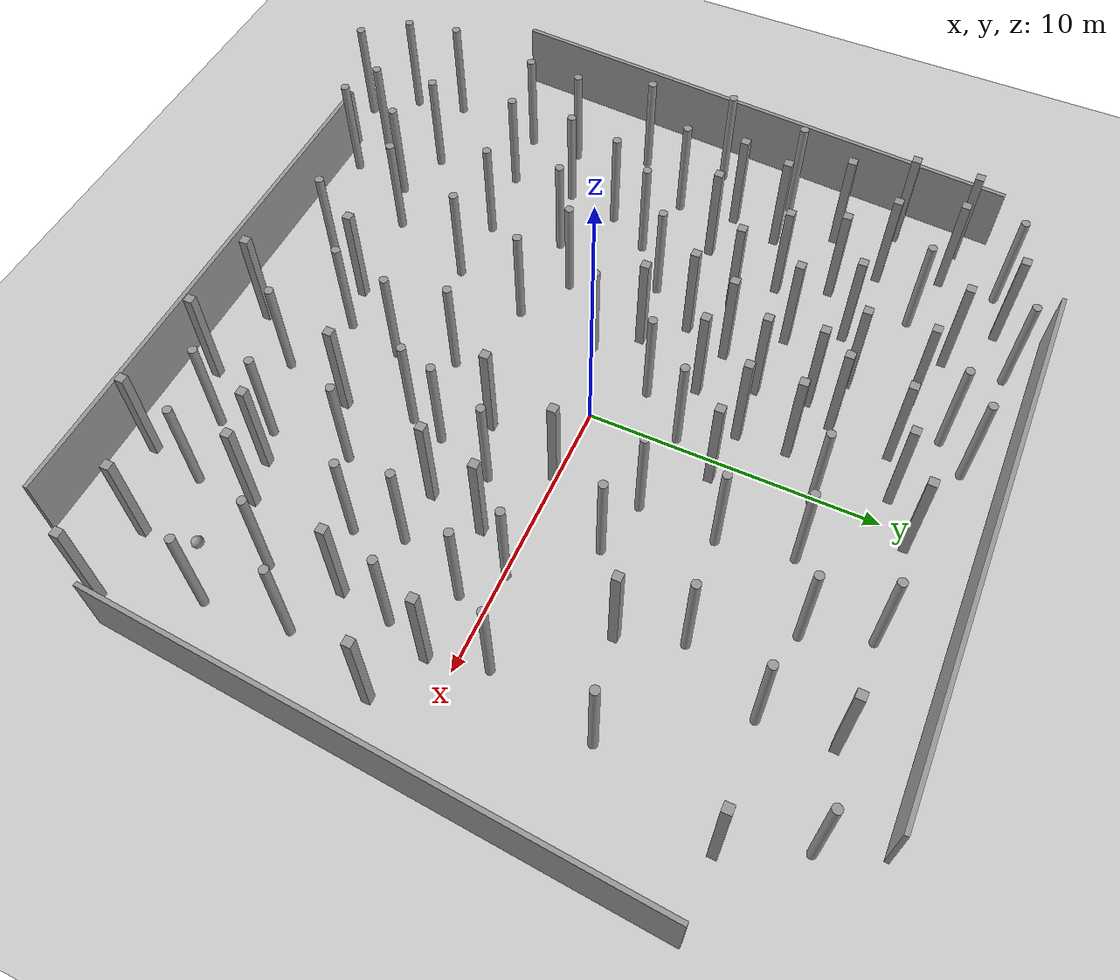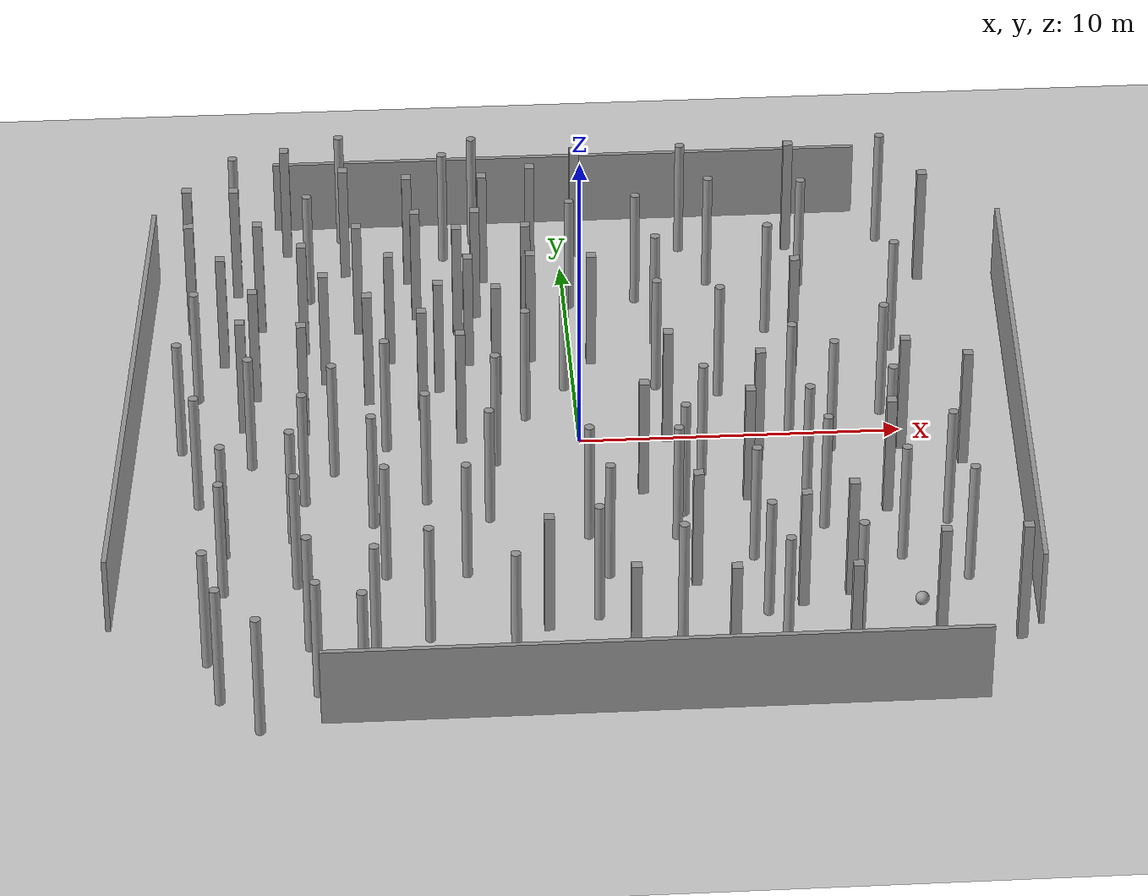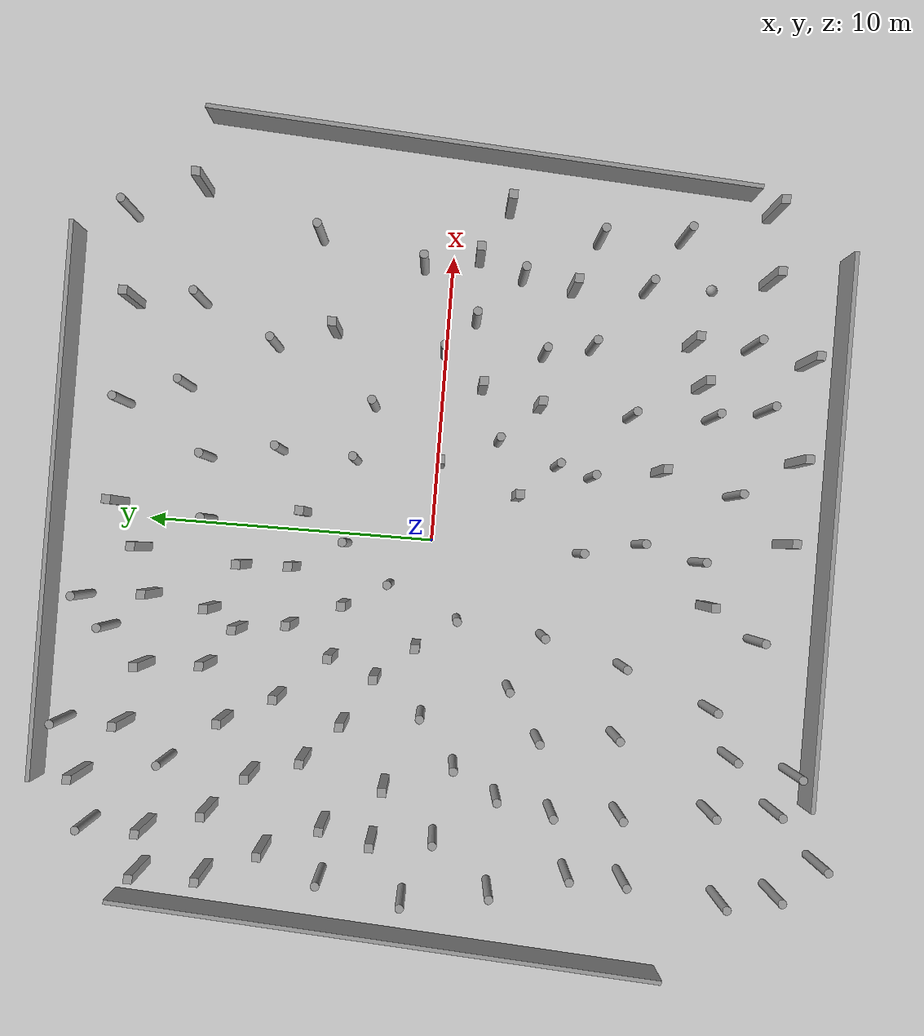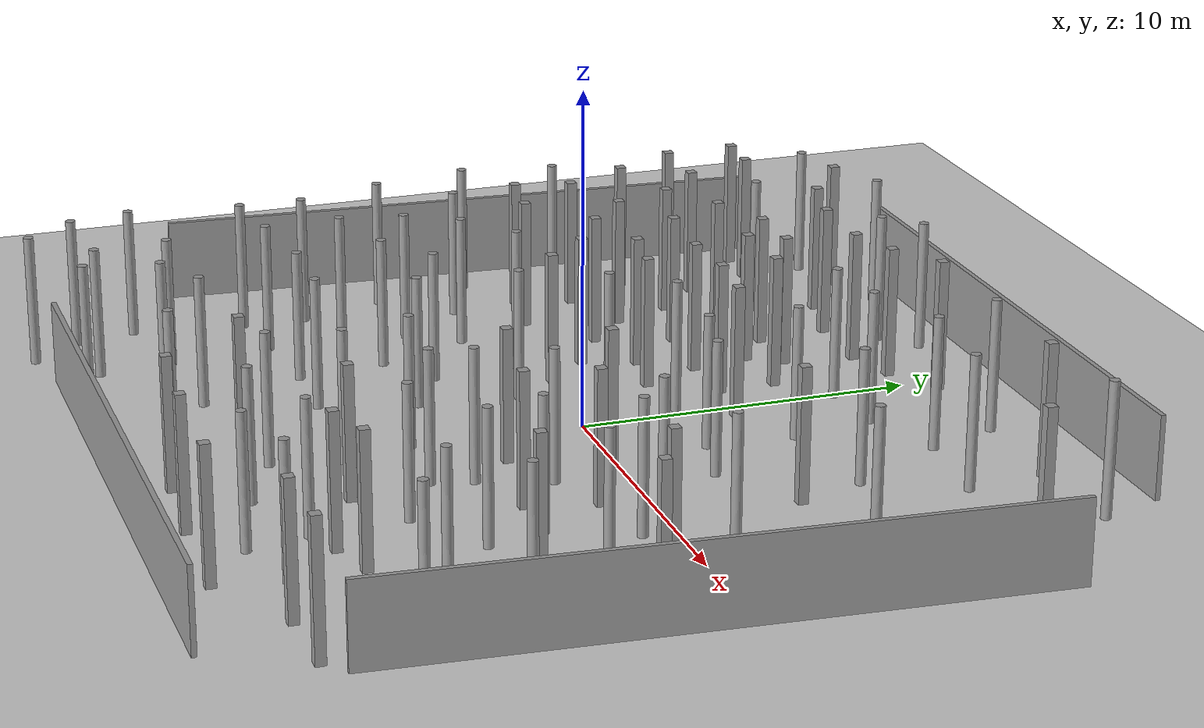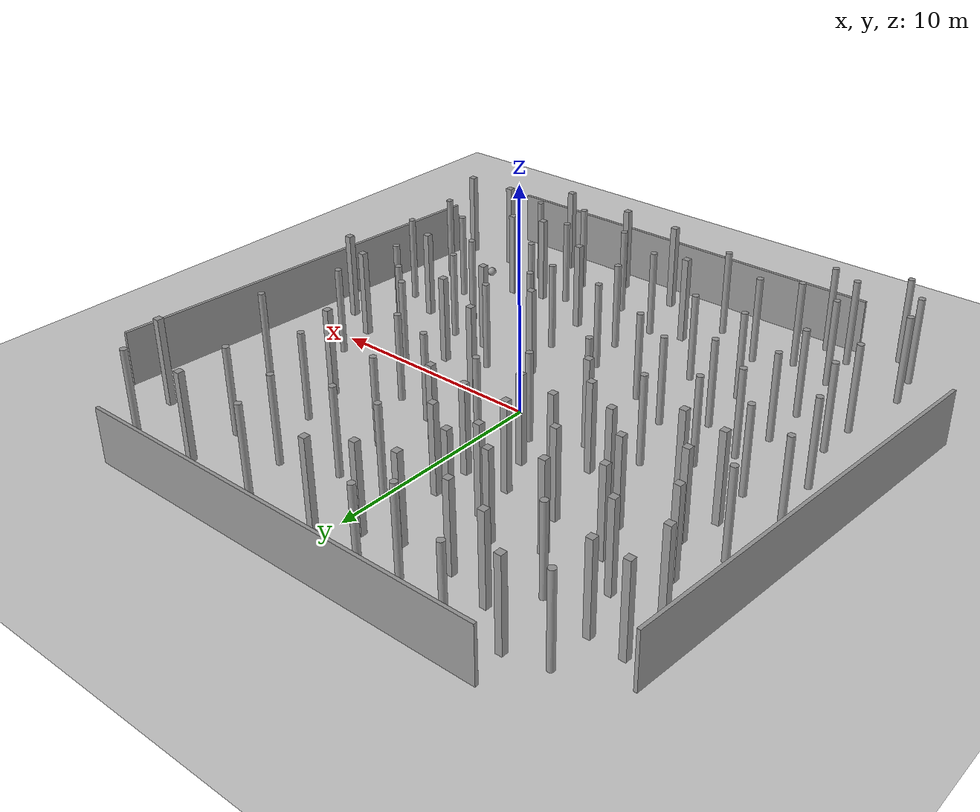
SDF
<sdf version="1.6">
 <world name="default">
  <light name="sun" type="directional">
   <pose>0 0 10 0 -0 0</pose>
   <diffuse>0.8 0.8 0.8 1</diffuse>
   <specular>0.2 0.2 0.2 1</specular>
   <attenuation>
    <range>1000</range>
    <constant>0.9</constant>
    <linear>0.01</linear>
    <quadratic>0.001</quadratic>
   </attenuation>
   <direction>-0.5 0.1 -0.9</direction>
  </light>
  <model name="ground_plane">
   <static>1</static>
   <link name="link">
    <collision name="collision">
     <geometry><plane><normal>0 0 1</normal><size>100 100</size></plane></geometry>
    </collision>
    <visual name="visual">
     <cast_shadows>0</cast_shadows>
     <geometry><plane><normal>0 0 1</normal><size>100 100</size></plane></geometry>
     <material>
      <script><uri>file://media/materials/scripts/gazebo.material</uri><name>Gazebo/Gray</name></script>
     </material>
    </visual>
   </link>
  </model>
  <gravity>0 0 -9.8</gravity>
  <magnetic_field>6e-06 2.3e-05 -4.2e-05</magnetic_field>
  <atmosphere type="adiabatic"/>
  <physics name="default_physics" default="0" type="ode">
   <max_step_size>0.002</max_step_size>
   <real_time_factor>1</real_time_factor>
   <real_time_update_rate>500</real_time_update_rate>
  </physics>
  <scene><ambient>0.4 0.4 0.4 1</ambient><background>0.7 0.7 0.7 1</background><shadows>1</shadows></scene>
  <spherical_coordinates>
   <surface_model>EARTH_WGS84</surface_model>
   <latitude_deg>0</latitude_deg>
   <longitude_deg>0</longitude_deg>
   <elevation>0</elevation>
   <heading_deg>0</heading_deg>
  </spherical_coordinates>
  <model name="unit_sphere">
   <link name="link">
    <inertial>
     <mass>1</mass>
     <inertia><ixx>0.1</ixx><ixy>0</ixy><ixz>0</ixz><iyy>0.1</iyy><iyz>0</iyz><izz>0.1</izz></inertia>
    </inertial>
    <gravity>0</gravity>
    <visual name="visual">
     <geometry><sphere><radius>0.203941</radius></sphere></geometry>
     <material>
      <script><name>Gazebo/Grey</name><uri>file://media/materials/scripts/gazebo.material</uri></script>
      <shader type="pixel"><normal_map>__default__</normal_map></shader>
     </material>
    </visual>
    <collision name="collision">
     <geometry><sphere><radius>0.203941</radius></sphere></geometry>
     <surface>
      <friction>
       <ode><mu>1</mu><mu2>1</mu2><fdir1>0 0 0</fdir1><slip1>0</slip1><slip2>0</slip2></ode>
       <torsional>
        <coefficient>1</coefficient>
        <patch_radius>0</patch_radius>
        <surface_radius>0</surface_radius>
        <use_patch_radius>1</use_patch_radius>
        <ode><slip>0</slip></ode>
       </torsional>
      </friction>
      <bounce><restitution_coefficient>0</restitution_coefficient><threshold>1e+06</threshold></bounce>
      <contact>
       <collide_without_contact>0</collide_without_contact>
       <collide_without_contact_bitmask>1</collide_without_contact_bitmask>
       <collide_bitmask>1</collide_bitmask>
       <ode>
        <soft_cfm>0</soft_cfm>
        <soft_erp>0.2</soft_erp>
        <kp>1e+13</kp>
        <kd>1</kd>
        <max_vel>0.01</max_vel>
        <min_depth>0</min_depth>
       </ode>
       <bullet>
        <split_impulse>1</split_impulse>
        <split_impulse_penetration_threshold>-0.01</split_impulse_penetration_threshold>
        <soft_cfm>0</soft_cfm>
        <soft_erp>0.2</soft_erp>
        <kp>1e+13</kp>
        <kd>1</kd>
       </bullet>
      </contact>
     </surface>
    </collision>
   </link>
   <static>0</static>
   <pose>9.54607 -9.14462 0.203941 0 -0 0</pose>
  </model>
  <audio><device>default</device></audio>
  <model name="unit_box">
   <link name="link">
    <inertial>
     <mass>1000</mass>
     <inertia><ixx>166.667</ixx><ixy>0</ixy><ixz>0</ixz><iyy>166.667</iyy><iyz>0</iyz><izz>166.667</izz></inertia>
    </inertial>
    <visual name="visual">
     <geometry><box><size>0.3 0.3 4</size></box></geometry>
     <material>
      <script><name>Gazebo/Grey</name><uri>file://media/materials/scripts/gazebo.material</uri></script>
      <shader type="vertex"><normal_map>__default__</normal_map></shader>
      <ambient>0.3 0.3 0.3 1</ambient>
      <diffuse>0.7 0.7 0.7 1</diffuse>
      <specular>0.01 0.01 0.01 1</specular>
      <emissive>0 0 0 1</emissive>
     </material>
    </visual>
    <collision name="collision">
     <geometry><box><size>0.3 0.3 4</size></box></geometry>
     <surface>
      <friction>
       <ode><mu>1</mu><mu2>1</mu2><fdir1>0 0 0</fdir1><slip1>0</slip1><slip2>0</slip2></ode>
       <torsional>
        <coefficient>1</coefficient>
        <patch_radius>0</patch_radius>
        <surface_radius>0</surface_radius>
        <use_patch_radius>1</use_patch_radius>
        <ode><slip>0</slip></ode>
       </torsional>
      </friction>
      <bounce><restitution_coefficient>0</restitution_coefficient><threshold>1e+06</threshold></bounce>
      <contact>
       <collide_without_contact>0</collide_without_contact>
       <collide_without_contact_bitmask>1</collide_without_contact_bitmask>
       <collide_bitmask>1</collide_bitmask>
       <ode>
        <soft_cfm>0</soft_cfm>
        <soft_erp>0.2</soft_erp>
        <kp>1e+13</kp>
        <kd>1</kd>
        <max_vel>0.01</max_vel>
        <min_depth>0</min_depth>
       </ode>
       <bullet>
        <split_impulse>1</split_impulse>
        <split_impulse_penetration_threshold>-0.01</split_impulse_penetration_threshold>
        <soft_cfm>0</soft_cfm>
        <soft_erp>0.2</soft_erp>
        <kp>1e+13</kp>
        <kd>1</kd>
       </bullet>
      </contact>
     </surface>
    </collision>
   </link>
   <static>0</static>
   <pose>-1.26728 4.71524 2 -8e-06 2e-06 -0.001346</pose>
  </model>
  <model name="unit_box_clone">
   <link name="link">
    <inertial>
     <mass>1000</mass>
     <inertia><ixx>166.667</ixx><ixy>0</ixy><ixz>0</ixz><iyy>166.667</iyy><iyz>0</iyz><izz>166.667</izz></inertia>
    </inertial>
    <visual name="visual">
     <geometry><box><size>0.3 0.3 4</size></box></geometry>
     <material>
      <script><name>Gazebo/Grey</name><uri>file://media/materials/scripts/gazebo.material</uri></script>
      <shader type="vertex"><normal_map>__default__</normal_map></shader>
      <ambient>0.3 0.3 0.3 1</ambient>
      <diffuse>0.7 0.7 0.7 1</diffuse>
      <specular>0.01 0.01 0.01 1</specular>
      <emissive>0 0 0 1</emissive>
     </material>
    </visual>
    <collision name="collision">
     <geometry><box><size>0.3 0.3 4</size></box></geometry>
     <surface>
      <friction>
       <ode><mu>1</mu><mu2>1</mu2><fdir1>0 0 0</fdir1><slip1>0</slip1><slip2>0</slip2></ode>
       <torsional>
        <coefficient>1</coefficient>
        <patch_radius>0</patch_radius>
        <surface_radius>0</surface_radius>
        <use_patch_radius>1</use_patch_radius>
        <ode><slip>0</slip></ode>
       </torsional>
      </friction>
      <bounce><restitution_coefficient>0</restitution_coefficient><threshold>1e+06</threshold></bounce>
      <contact>
       <collide_without_contact>0</collide_without_contact>
       <collide_without_contact_bitmask>1</collide_without_contact_bitmask>
       <collide_bitmask>1</collide_bitmask>
       <ode>
        <soft_cfm>0</soft_cfm>
        <soft_erp>0.2</soft_erp>
        <kp>1e+13</kp>
        <kd>1</kd>
        <max_vel>0.01</max_vel>
        <min_depth>0</min_depth>
       </ode>
       <bullet>
        <split_impulse>1</split_impulse>
        <split_impulse_penetration_threshold>-0.01</split_impulse_penetration_threshold>
        <soft_cfm>0</soft_cfm>
        <soft_erp>0.2</soft_erp>
        <kp>1e+13</kp>
        <kd>1</kd>
       </bullet>
      </contact>
     </surface>
    </collision>
   </link>
   <static>0</static>
   <pose>-3.66858 0.277519 2.00001 -6.1e-05 -2e-06 -0.000344</pose>
  </model>
  <model name="unit_box_clone_1">
   <link name="link">
    <inertial>
     <mass>1000</mass>
     <inertia><ixx>166.667</ixx><ixy>0</ixy><ixz>0</ixz><iyy>166.667</iyy><iyz>0</iyz><izz>166.667</izz></inertia>
    </inertial>
    <visual name="visual">
     <geometry><box><size>0.3 0.3 4</size></box></geometry>
     <material>
      <script><name>Gazebo/Grey</name><uri>file://media/materials/scripts/gazebo.material</uri></script>
      <shader type="vertex"><normal_map>__default__</normal_map></shader>
      <ambient>0.3 0.3 0.3 1</ambient>
      <diffuse>0.7 0.7 0.7 1</diffuse>
      <specular>0.01 0.01 0.01 1</specular>
      <emissive>0 0 0 1</emissive>
     </material>
    </visual>
    <collision name="collision">
     <geometry><box><size>0.3 0.3 4</size></box></geometry>
     <surface>
      <friction>
       <ode><mu>1</mu><mu2>1</mu2><fdir1>0 0 0</fdir1><slip1>0</slip1><slip2>0</slip2></ode>
       <torsional>
        <coefficient>1</coefficient>
        <patch_radius>0</patch_radius>
        <surface_radius>0</surface_radius>
        <use_patch_radius>1</use_patch_radius>
        <ode><slip>0</slip></ode>
       </torsional>
      </friction>
      <bounce><restitution_coefficient>0</restitution_coefficient><threshold>1e+06</threshold></bounce>
      <contact>
       <collide_without_contact>0</collide_without_contact>
       <collide_without_contact_bitmask>1</collide_without_contact_bitmask>
       <collide_bitmask>1</collide_bitmask>
       <ode>
        <soft_cfm>0</soft_cfm>
        <soft_erp>0.2</soft_erp>
        <kp>1e+13</kp>
        <kd>1</kd>
        <max_vel>0.01</max_vel>
        <min_depth>0</min_depth>
       </ode>
       <bullet>
        <split_impulse>1</split_impulse>
        <split_impulse_penetration_threshold>-0.01</split_impulse_penetration_threshold>
        <soft_cfm>0</soft_cfm>
        <soft_erp>0.2</soft_erp>
        <kp>1e+13</kp>
        <kd>1</kd>
       </bullet>
      </contact>
     </surface>
    </collision>
   </link>
   <static>0</static>
   <pose>-2.89926 7.41393 2 1.2e-05 -1.2e-05 -0.004598</pose>
  </model>
  <model name="unit_box_clone_2">
   <link name="link">
    <inertial>
     <mass>1000</mass>
     <inertia><ixx>166.667</ixx><ixy>0</ixy><ixz>0</ixz><iyy>166.667</iyy><iyz>0</iyz><izz>166.667</izz></inertia>
    </inertial>
    <visual name="visual">
     <geometry><box><size>0.3 0.3 4</size></box></geometry>
     <material>
      <script><name>Gazebo/Grey</name><uri>file://media/materials/scripts/gazebo.material</uri></script>
      <shader type="vertex"><normal_map>__default__</normal_map></shader>
      <ambient>0.3 0.3 0.3 1</ambient>
      <diffuse>0.7 0.7 0.7 1</diffuse>
      <specular>0.01 0.01 0.01 1</specular>
      <emissive>0 0 0 1</emissive>
     </material>
    </visual>
    <collision name="collision">
     <geometry><box><size>0.3 0.3 4</size></box></geometry>
     <surface>
      <friction>
       <ode><mu>1</mu><mu2>1</mu2><fdir1>0 0 0</fdir1><slip1>0</slip1><slip2>0</slip2></ode>
       <torsional>
        <coefficient>1</coefficient>
        <patch_radius>0</patch_radius>
        <surface_radius>0</surface_radius>
        <use_patch_radius>1</use_patch_radius>
        <ode><slip>0</slip></ode>
       </torsional>
      </friction>
      <bounce><restitution_coefficient>0</restitution_coefficient><threshold>1e+06</threshold></bounce>
      <contact>
       <collide_without_contact>0</collide_without_contact>
       <collide_without_contact_bitmask>1</collide_without_contact_bitmask>
       <collide_bitmask>1</collide_bitmask>
       <ode>
        <soft_cfm>0</soft_cfm>
        <soft_erp>0.2</soft_erp>
        <kp>1e+13</kp>
        <kd>1</kd>
        <max_vel>0.01</max_vel>
        <min_depth>0</min_depth>
       </ode>
       <bullet>
        <split_impulse>1</split_impulse>
        <split_impulse_penetration_threshold>-0.01</split_impulse_penetration_threshold>
        <soft_cfm>0</soft_cfm>
        <soft_erp>0.2</soft_erp>
        <kp>1e+13</kp>
        <kd>1</kd>
       </bullet>
      </contact>
     </surface>
    </collision>
   </link>
   <static>0</static>
   <pose>4.92525 -3.34794 2 7e-06 -1.8e-05 -0.008091</pose>
  </model>
  <model name="unit_box_clone_3">
   <link name="link">
    <inertial>
     <mass>1000</mass>
     <inertia><ixx>166.667</ixx><ixy>0</ixy><ixz>0</ixz><iyy>166.667</iyy><iyz>0</iyz><izz>166.667</izz></inertia>
    </inertial>
    <visual name="visual">
     <geometry><box><size>0.3 0.3 4</size></box></geometry>
     <material>
      <script><name>Gazebo/Grey</name><uri>file://media/materials/scripts/gazebo.material</uri></script>
      <shader type="vertex"><normal_map>__default__</normal_map></shader>
      <ambient>0.3 0.3 0.3 1</ambient>
      <diffuse>0.7 0.7 0.7 1</diffuse>
      <specular>0.01 0.01 0.01 1</specular>
      <emissive>0 0 0 1</emissive>
     </material>
    </visual>
    <collision name="collision">
     <geometry><box><size>0.3 0.3 4</size></box></geometry>
     <surface>
      <friction>
       <ode><mu>1</mu><mu2>1</mu2><fdir1>0 0 0</fdir1><slip1>0</slip1><slip2>0</slip2></ode>
       <torsional>
        <coefficient>1</coefficient>
        <patch_radius>0</patch_radius>
        <surface_radius>0</surface_radius>
        <use_patch_radius>1</use_patch_radius>
        <ode><slip>0</slip></ode>
       </torsional>
      </friction>
      <bounce><restitution_coefficient>0</restitution_coefficient><threshold>1e+06</threshold></bounce>
      <contact>
       <collide_without_contact>0</collide_without_contact>
       <collide_without_contact_bitmask>1</collide_without_contact_bitmask>
       <collide_bitmask>1</collide_bitmask>
       <ode>
        <soft_cfm>0</soft_cfm>
        <soft_erp>0.2</soft_erp>
        <kp>1e+13</kp>
        <kd>1</kd>
        <max_vel>0.01</max_vel>
        <min_depth>0</min_depth>
       </ode>
       <bullet>
        <split_impulse>1</split_impulse>
        <split_impulse_penetration_threshold>-0.01</split_impulse_penetration_threshold>
        <soft_cfm>0</soft_cfm>
        <soft_erp>0.2</soft_erp>
        <kp>1e+13</kp>
        <kd>1</kd>
       </bullet>
      </contact>
     </surface>
    </collision>
   </link>
   <static>0</static>
   <pose>-9.81581 6.97356 2.00001 3.5e-05 5e-06 -0.002659</pose>
  </model>
  <model name="unit_box_clone_4">
   <link name="link">
    <inertial>
     <mass>1000</mass>
     <inertia><ixx>166.667</ixx><ixy>0</ixy><ixz>0</ixz><iyy>166.667</iyy><iyz>0</iyz><izz>166.667</izz></inertia>
    </inertial>
    <visual name="visual">
     <geometry><box><size>0.3 0.3 4</size></box></geometry>
     <material>
      <script><name>Gazebo/Grey</name><uri>file://media/materials/scripts/gazebo.material</uri></script>
      <shader type="vertex"><normal_map>__default__</normal_map></shader>
      <ambient>0.3 0.3 0.3 1</ambient>
      <diffuse>0.7 0.7 0.7 1</diffuse>
      <specular>0.01 0.01 0.01 1</specular>
      <emissive>0 0 0 1</emissive>
     </material>
    </visual>
    <collision name="collision">
     <geometry><box><size>0.3 0.3 4</size></box></geometry>
     <surface>
      <friction>
       <ode><mu>1</mu><mu2>1</mu2><fdir1>0 0 0</fdir1><slip1>0</slip1><slip2>0</slip2></ode>
       <torsional>
        <coefficient>1</coefficient>
        <patch_radius>0</patch_radius>
        <surface_radius>0</surface_radius>
        <use_patch_radius>1</use_patch_radius>
        <ode><slip>0</slip></ode>
       </torsional>
      </friction>
      <bounce><restitution_coefficient>0</restitution_coefficient><threshold>1e+06</threshold></bounce>
      <contact>
       <collide_without_contact>0</collide_without_contact>
       <collide_without_contact_bitmask>1</collide_without_contact_bitmask>
       <collide_bitmask>1</collide_bitmask>
       <ode>
        <soft_cfm>0</soft_cfm>
        <soft_erp>0.2</soft_erp>
        <kp>1e+13</kp>
        <kd>1</kd>
        <max_vel>0.01</max_vel>
        <min_depth>0</min_depth>
       </ode>
       <bullet>
        <split_impulse>1</split_impulse>
        <split_impulse_penetration_threshold>-0.01</split_impulse_penetration_threshold>
        <soft_cfm>0</soft_cfm>
        <soft_erp>0.2</soft_erp>
        <kp>1e+13</kp>
        <kd>1</kd>
       </bullet>
      </contact>
     </surface>
    </collision>
   </link>
   <static>0</static>
   <pose>-12.064 9.20885 2.00002 0.00014 1e-05 -0.004402</pose>
  </model>
  <model name="unit_box_clone_5">
   <link name="link">
    <inertial>
     <mass>1000</mass>
     <inertia><ixx>166.667</ixx><ixy>0</ixy><ixz>0</ixz><iyy>166.667</iyy><iyz>0</iyz><izz>166.667</izz></inertia>
    </inertial>
    <visual name="visual">
     <geometry><box><size>0.3 0.3 4</size></box></geometry>
     <material>
      <script><name>Gazebo/Grey</name><uri>file://media/materials/scripts/gazebo.material</uri></script>
      <shader type="vertex"><normal_map>__default__</normal_map></shader>
      <ambient>0.3 0.3 0.3 1</ambient>
      <diffuse>0.7 0.7 0.7 1</diffuse>
      <specular>0.01 0.01 0.01 1</specular>
      <emissive>0 0 0 1</emissive>
     </material>
    </visual>
    <collision name="collision">
     <geometry><box><size>0.3 0.3 4</size></box></geometry>
     <surface>
      <friction>
       <ode><mu>1</mu><mu2>1</mu2><fdir1>0 0 0</fdir1><slip1>0</slip1><slip2>0</slip2></ode>
       <torsional>
        <coefficient>1</coefficient>
        <patch_radius>0</patch_radius>
        <surface_radius>0</surface_radius>
        <use_patch_radius>1</use_patch_radius>
        <ode><slip>0</slip></ode>
       </torsional>
      </friction>
      <bounce><restitution_coefficient>0</restitution_coefficient><threshold>1e+06</threshold></bounce>
      <contact>
       <collide_without_contact>0</collide_without_contact>
       <collide_without_contact_bitmask>1</collide_without_contact_bitmask>
       <collide_bitmask>1</collide_bitmask>
       <ode>
        <soft_cfm>0</soft_cfm>
        <soft_erp>0.2</soft_erp>
        <kp>1e+13</kp>
        <kd>1</kd>
        <max_vel>0.01</max_vel>
        <min_depth>0</min_depth>
       </ode>
       <bullet>
        <split_impulse>1</split_impulse>
        <split_impulse_penetration_threshold>-0.01</split_impulse_penetration_threshold>
        <soft_cfm>0</soft_cfm>
        <soft_erp>0.2</soft_erp>
        <kp>1e+13</kp>
        <kd>1</kd>
       </bullet>
      </contact>
     </surface>
    </collision>
   </link>
   <static>0</static>
   <pose>7.51087 10.9218 2 -6e-06 -0 -0.013801</pose>
  </model>
  <model name="unit_box_clone_6">
   <link name="link">
    <inertial>
     <mass>1000</mass>
     <inertia><ixx>166.667</ixx><ixy>0</ixy><ixz>0</ixz><iyy>166.667</iyy><iyz>0</iyz><izz>166.667</izz></inertia>
    </inertial>
    <visual name="visual">
     <geometry><box><size>0.3 0.3 4</size></box></geometry>
     <material>
      <script><name>Gazebo/Grey</name><uri>file://media/materials/scripts/gazebo.material</uri></script>
      <shader type="vertex"><normal_map>__default__</normal_map></shader>
      <ambient>0.3 0.3 0.3 1</ambient>
      <diffuse>0.7 0.7 0.7 1</diffuse>
      <specular>0.01 0.01 0.01 1</specular>
      <emissive>0 0 0 1</emissive>
     </material>
    </visual>
    <collision name="collision">
     <geometry><box><size>0.3 0.3 4</size></box></geometry>
     <surface>
      <friction>
       <ode><mu>1</mu><mu2>1</mu2><fdir1>0 0 0</fdir1><slip1>0</slip1><slip2>0</slip2></ode>
       <torsional>
        <coefficient>1</coefficient>
        <patch_radius>0</patch_radius>
        <surface_radius>0</surface_radius>
        <use_patch_radius>1</use_patch_radius>
        <ode><slip>0</slip></ode>
       </torsional>
      </friction>
      <bounce><restitution_coefficient>0</restitution_coefficient><threshold>1e+06</threshold></bounce>
      <contact>
       <collide_without_contact>0</collide_without_contact>
       <collide_without_contact_bitmask>1</collide_without_contact_bitmask>
       <collide_bitmask>1</collide_bitmask>
       <ode>
        <soft_cfm>0</soft_cfm>
        <soft_erp>0.2</soft_erp>
        <kp>1e+13</kp>
        <kd>1</kd>
        <max_vel>0.01</max_vel>
        <min_depth>0</min_depth>
       </ode>
       <bullet>
        <split_impulse>1</split_impulse>
        <split_impulse_penetration_threshold>-0.01</split_impulse_penetration_threshold>
        <soft_cfm>0</soft_cfm>
        <soft_erp>0.2</soft_erp>
        <kp>1e+13</kp>
        <kd>1</kd>
       </bullet>
      </contact>
     </surface>
    </collision>
   </link>
   <static>0</static>
   <pose>11.6419 8.80512 2 -2.9e-05 -0 -0.005214</pose>
  </model>
  <model name="unit_box_clone_7">
   <link name="link">
    <inertial>
     <mass>1000</mass>
     <inertia><ixx>166.667</ixx><ixy>0</ixy><ixz>0</ixz><iyy>166.667</iyy><iyz>0</iyz><izz>166.667</izz></inertia>
    </inertial>
    <visual name="visual">
     <geometry><box><size>0.3 0.3 4</size></box></geometry>
     <material>
      <script><name>Gazebo/Grey</name><uri>file://media/materials/scripts/gazebo.material</uri></script>
      <shader type="vertex"><normal_map>__default__</normal_map></shader>
      <ambient>0.3 0.3 0.3 1</ambient>
      <diffuse>0.7 0.7 0.7 1</diffuse>
      <specular>0.01 0.01 0.01 1</specular>
      <emissive>0 0 0 1</emissive>
     </material>
    </visual>
    <collision name="collision">
     <geometry><box><size>0.3 0.3 4</size></box></geometry>
     <surface>
      <friction>
       <ode><mu>1</mu><mu2>1</mu2><fdir1>0 0 0</fdir1><slip1>0</slip1><slip2>0</slip2></ode>
       <torsional>
        <coefficient>1</coefficient>
        <patch_radius>0</patch_radius>
        <surface_radius>0</surface_radius>
        <use_patch_radius>1</use_patch_radius>
        <ode><slip>0</slip></ode>
       </torsional>
      </friction>
      <bounce><restitution_coefficient>0</restitution_coefficient><threshold>1e+06</threshold></bounce>
      <contact>
       <collide_without_contact>0</collide_without_contact>
       <collide_without_contact_bitmask>1</collide_without_contact_bitmask>
       <collide_bitmask>1</collide_bitmask>
       <ode>
        <soft_cfm>0</soft_cfm>
        <soft_erp>0.2</soft_erp>
        <kp>1e+13</kp>
        <kd>1</kd>
        <max_vel>0.01</max_vel>
        <min_depth>0</min_depth>
       </ode>
       <bullet>
        <split_impulse>1</split_impulse>
        <split_impulse_penetration_threshold>-0.01</split_impulse_penetration_threshold>
        <soft_cfm>0</soft_cfm>
        <soft_erp>0.2</soft_erp>
        <kp>1e+13</kp>
        <kd>1</kd>
       </bullet>
      </contact>
     </surface>
    </collision>
   </link>
   <static>0</static>
   <pose>9.86044 -10.963 2 2e-06 -1.6e-05 -0.003976</pose>
  </model>
  <model name="unit_box_clone_8">
   <link name="link">
    <inertial>
     <mass>1000</mass>
     <inertia><ixx>166.667</ixx><ixy>0</ixy><ixz>0</ixz><iyy>166.667</iyy><iyz>0</iyz><izz>166.667</izz></inertia>
    </inertial>
    <visual name="visual">
     <geometry><box><size>0.3 0.3 4</size></box></geometry>
     <material>
      <script><name>Gazebo/Grey</name><uri>file://media/materials/scripts/gazebo.material</uri></script>
      <shader type="vertex"><normal_map>__default__</normal_map></shader>
      <ambient>0.3 0.3 0.3 1</ambient>
      <diffuse>0.7 0.7 0.7 1</diffuse>
      <specular>0.01 0.01 0.01 1</specular>
      <emissive>0 0 0 1</emissive>
     </material>
    </visual>
    <collision name="collision">
     <geometry><box><size>0.3 0.3 4</size></box></geometry>
     <surface>
      <friction>
       <ode><mu>1</mu><mu2>1</mu2><fdir1>0 0 0</fdir1><slip1>0</slip1><slip2>0</slip2></ode>
       <torsional>
        <coefficient>1</coefficient>
        <patch_radius>0</patch_radius>
        <surface_radius>0</surface_radius>
        <use_patch_radius>1</use_patch_radius>
        <ode><slip>0</slip></ode>
       </torsional>
      </friction>
      <bounce><restitution_coefficient>0</restitution_coefficient><threshold>1e+06</threshold></bounce>
      <contact>
       <collide_without_contact>0</collide_without_contact>
       <collide_without_contact_bitmask>1</collide_without_contact_bitmask>
       <collide_bitmask>1</collide_bitmask>
       <ode>
        <soft_cfm>0</soft_cfm>
        <soft_erp>0.2</soft_erp>
        <kp>1e+13</kp>
        <kd>1</kd>
        <max_vel>0.01</max_vel>
        <min_depth>0</min_depth>
       </ode>
       <bullet>
        <split_impulse>1</split_impulse>
        <split_impulse_penetration_threshold>-0.01</split_impulse_penetration_threshold>
        <soft_cfm>0</soft_cfm>
        <soft_erp>0.2</soft_erp>
        <kp>1e+13</kp>
        <kd>1</kd>
       </bullet>
      </contact>
     </surface>
    </collision>
   </link>
   <static>0</static>
   <pose>-6.68892 6.67586 2 -3e-06 -1.7e-05 -0.006785</pose>
  </model>
  <model name="unit_box_clone_9">
   <link name="link">
    <inertial>
     <mass>1000</mass>
     <inertia><ixx>166.667</ixx><ixy>0</ixy><ixz>0</ixz><iyy>166.667</iyy><iyz>0</iyz><izz>166.667</izz></inertia>
    </inertial>
    <visual name="visual">
     <geometry><box><size>0.3 0.3 4</size></box></geometry>
     <material>
      <script><name>Gazebo/Grey</name><uri>file://media/materials/scripts/gazebo.material</uri></script>
      <shader type="vertex"><normal_map>__default__</normal_map></shader>
      <ambient>0.3 0.3 0.3 1</ambient>
      <diffuse>0.7 0.7 0.7 1</diffuse>
      <specular>0.01 0.01 0.01 1</specular>
      <emissive>0 0 0 1</emissive>
     </material>
    </visual>
    <collision name="collision">
     <geometry><box><size>0.3 0.3 4</size></box></geometry>
     <surface>
      <friction>
       <ode><mu>1</mu><mu2>1</mu2><fdir1>0 0 0</fdir1><slip1>0</slip1><slip2>0</slip2></ode>
       <torsional>
        <coefficient>1</coefficient>
        <patch_radius>0</patch_radius>
        <surface_radius>0</surface_radius>
        <use_patch_radius>1</use_patch_radius>
        <ode><slip>0</slip></ode>
       </torsional>
      </friction>
      <bounce><restitution_coefficient>0</restitution_coefficient><threshold>1e+06</threshold></bounce>
      <contact>
       <collide_without_contact>0</collide_without_contact>
       <collide_without_contact_bitmask>1</collide_without_contact_bitmask>
       <collide_bitmask>1</collide_bitmask>
       <ode>
        <soft_cfm>0</soft_cfm>
        <soft_erp>0.2</soft_erp>
        <kp>1e+13</kp>
        <kd>1</kd>
        <max_vel>0.01</max_vel>
        <min_depth>0</min_depth>
       </ode>
       <bullet>
        <split_impulse>1</split_impulse>
        <split_impulse_penetration_threshold>-0.01</split_impulse_penetration_threshold>
        <soft_cfm>0</soft_cfm>
        <soft_erp>0.2</soft_erp>
        <kp>1e+13</kp>
        <kd>1</kd>
       </bullet>
      </contact>
     </surface>
    </collision>
   </link>
   <static>0</static>
   <pose>-8.44974 5.60757 2.00001 3.5e-05 5e-06 -0.002659</pose>
  </model>
  <model name="unit_box_clone_10">
   <link name="link">
    <inertial>
     <mass>1000</mass>
     <inertia><ixx>166.667</ixx><ixy>0</ixy><ixz>0</ixz><iyy>166.667</iyy><iyz>0</iyz><izz>166.667</izz></inertia>
    </inertial>
    <visual name="visual">
     <geometry><box><size>0.3 0.3 4</size></box></geometry>
     <material>
      <script><name>Gazebo/Grey</name><uri>file://media/materials/scripts/gazebo.material</uri></script>
      <shader type="vertex"><normal_map>__default__</normal_map></shader>
      <ambient>0.3 0.3 0.3 1</ambient>
      <diffuse>0.7 0.7 0.7 1</diffuse>
      <specular>0.01 0.01 0.01 1</specular>
      <emissive>0 0 0 1</emissive>
     </material>
    </visual>
    <collision name="collision">
     <geometry><box><size>0.3 0.3 4</size></box></geometry>
     <surface>
      <friction>
       <ode><mu>1</mu><mu2>1</mu2><fdir1>0 0 0</fdir1><slip1>0</slip1><slip2>0</slip2></ode>
       <torsional>
        <coefficient>1</coefficient>
        <patch_radius>0</patch_radius>
        <surface_radius>0</surface_radius>
        <use_patch_radius>1</use_patch_radius>
        <ode><slip>0</slip></ode>
       </torsional>
      </friction>
      <bounce><restitution_coefficient>0</restitution_coefficient><threshold>1e+06</threshold></bounce>
      <contact>
       <collide_without_contact>0</collide_without_contact>
       <collide_without_contact_bitmask>1</collide_without_contact_bitmask>
       <collide_bitmask>1</collide_bitmask>
       <ode>
        <soft_cfm>0</soft_cfm>
        <soft_erp>0.2</soft_erp>
        <kp>1e+13</kp>
        <kd>1</kd>
        <max_vel>0.01</max_vel>
        <min_depth>0</min_depth>
       </ode>
       <bullet>
        <split_impulse>1</split_impulse>
        <split_impulse_penetration_threshold>-0.01</split_impulse_penetration_threshold>
        <soft_cfm>0</soft_cfm>
        <soft_erp>0.2</soft_erp>
        <kp>1e+13</kp>
        <kd>1</kd>
       </bullet>
      </contact>
     </surface>
    </collision>
   </link>
   <static>0</static>
   <pose>-8.91741 11.4995 2 0 -3e-06 -0.008455</pose>
  </model>
  <model name="unit_box_clone_11">
   <link name="link">
    <inertial>
     <mass>1000</mass>
     <inertia><ixx>166.667</ixx><ixy>0</ixy><ixz>0</ixz><iyy>166.667</iyy><iyz>0</iyz><izz>166.667</izz></inertia>
    </inertial>
    <visual name="visual">
     <geometry><box><size>0.3 0.3 4</size></box></geometry>
     <material>
      <script><name>Gazebo/Grey</name><uri>file://media/materials/scripts/gazebo.material</uri></script>
      <shader type="vertex"><normal_map>__default__</normal_map></shader>
      <ambient>0.3 0.3 0.3 1</ambient>
      <diffuse>0.7 0.7 0.7 1</diffuse>
      <specular>0.01 0.01 0.01 1</specular>
      <emissive>0 0 0 1</emissive>
     </material>
    </visual>
    <collision name="collision">
     <geometry><box><size>0.3 0.3 4</size></box></geometry>
     <surface>
      <friction>
       <ode><mu>1</mu><mu2>1</mu2><fdir1>0 0 0</fdir1><slip1>0</slip1><slip2>0</slip2></ode>
       <torsional>
        <coefficient>1</coefficient>
        <patch_radius>0</patch_radius>
        <surface_radius>0</surface_radius>
        <use_patch_radius>1</use_patch_radius>
        <ode><slip>0</slip></ode>
       </torsional>
      </friction>
      <bounce><restitution_coefficient>0</restitution_coefficient><threshold>1e+06</threshold></bounce>
      <contact>
       <collide_without_contact>0</collide_without_contact>
       <collide_without_contact_bitmask>1</collide_without_contact_bitmask>
       <collide_bitmask>1</collide_bitmask>
       <ode>
        <soft_cfm>0</soft_cfm>
        <soft_erp>0.2</soft_erp>
        <kp>1e+13</kp>
        <kd>1</kd>
        <max_vel>0.01</max_vel>
        <min_depth>0</min_depth>
       </ode>
       <bullet>
        <split_impulse>1</split_impulse>
        <split_impulse_penetration_threshold>-0.01</split_impulse_penetration_threshold>
        <soft_cfm>0</soft_cfm>
        <soft_erp>0.2</soft_erp>
        <kp>1e+13</kp>
        <kd>1</kd>
       </bullet>
      </contact>
     </surface>
    </collision>
   </link>
   <static>0</static>
   <pose>-10.559 9.10969 2 -1.3e-05 5e-06 0.00257</pose>
  </model>
  <model name="unit_box_clone_12">
   <link name="link">
    <inertial>
     <mass>1000</mass>
     <inertia><ixx>166.667</ixx><ixy>0</ixy><ixz>0</ixz><iyy>166.667</iyy><iyz>0</iyz><izz>166.667</izz></inertia>
    </inertial>
    <visual name="visual">
     <geometry><box><size>0.3 0.3 4</size></box></geometry>
     <material>
      <script><name>Gazebo/Grey</name><uri>file://media/materials/scripts/gazebo.material</uri></script>
      <shader type="vertex"><normal_map>__default__</normal_map></shader>
      <ambient>0.3 0.3 0.3 1</ambient>
      <diffuse>0.7 0.7 0.7 1</diffuse>
      <specular>0.01 0.01 0.01 1</specular>
      <emissive>0 0 0 1</emissive>
     </material>
    </visual>
    <collision name="collision">
     <geometry><box><size>0.3 0.3 4</size></box></geometry>
     <surface>
      <friction>
       <ode><mu>1</mu><mu2>1</mu2><fdir1>0 0 0</fdir1><slip1>0</slip1><slip2>0</slip2></ode>
       <torsional>
        <coefficient>1</coefficient>
        <patch_radius>0</patch_radius>
        <surface_radius>0</surface_radius>
        <use_patch_radius>1</use_patch_radius>
        <ode><slip>0</slip></ode>
       </torsional>
      </friction>
      <bounce><restitution_coefficient>0</restitution_coefficient><threshold>1e+06</threshold></bounce>
      <contact>
       <collide_without_contact>0</collide_without_contact>
       <collide_without_contact_bitmask>1</collide_without_contact_bitmask>
       <collide_bitmask>1</collide_bitmask>
       <ode>
        <soft_cfm>0</soft_cfm>
        <soft_erp>0.2</soft_erp>
        <kp>1e+13</kp>
        <kd>1</kd>
        <max_vel>0.01</max_vel>
        <min_depth>0</min_depth>
       </ode>
       <bullet>
        <split_impulse>1</split_impulse>
        <split_impulse_penetration_threshold>-0.01</split_impulse_penetration_threshold>
        <soft_cfm>0</soft_cfm>
        <soft_erp>0.2</soft_erp>
        <kp>1e+13</kp>
        <kd>1</kd>
       </bullet>
      </contact>
     </surface>
    </collision>
   </link>
   <static>0</static>
   <pose>-6.46638 2.58987 2 -8e-06 -1e-06 0.000576</pose>
  </model>
  <model name="unit_box_clone_13">
   <link name="link">
    <inertial>
     <mass>1000</mass>
     <inertia><ixx>166.667</ixx><ixy>0</ixy><ixz>0</ixz><iyy>166.667</iyy><iyz>0</iyz><izz>166.667</izz></inertia>
    </inertial>
    <visual name="visual">
     <geometry><box><size>0.3 0.3 4</size></box></geometry>
     <material>
      <script><name>Gazebo/Grey</name><uri>file://media/materials/scripts/gazebo.material</uri></script>
      <shader type="vertex"><normal_map>__default__</normal_map></shader>
      <ambient>0.3 0.3 0.3 1</ambient>
      <diffuse>0.7 0.7 0.7 1</diffuse>
      <specular>0.01 0.01 0.01 1</specular>
      <emissive>0 0 0 1</emissive>
     </material>
    </visual>
    <collision name="collision">
     <geometry><box><size>0.3 0.3 4</size></box></geometry>
     <surface>
      <friction>
       <ode><mu>1</mu><mu2>1</mu2><fdir1>0 0 0</fdir1><slip1>0</slip1><slip2>0</slip2></ode>
       <torsional>
        <coefficient>1</coefficient>
        <patch_radius>0</patch_radius>
        <surface_radius>0</surface_radius>
        <use_patch_radius>1</use_patch_radius>
        <ode><slip>0</slip></ode>
       </torsional>
      </friction>
      <bounce><restitution_coefficient>0</restitution_coefficient><threshold>1e+06</threshold></bounce>
      <contact>
       <collide_without_contact>0</collide_without_contact>
       <collide_without_contact_bitmask>1</collide_without_contact_bitmask>
       <collide_bitmask>1</collide_bitmask>
       <ode>
        <soft_cfm>0</soft_cfm>
        <soft_erp>0.2</soft_erp>
        <kp>1e+13</kp>
        <kd>1</kd>
        <max_vel>0.01</max_vel>
        <min_depth>0</min_depth>
       </ode>
       <bullet>
        <split_impulse>1</split_impulse>
        <split_impulse_penetration_threshold>-0.01</split_impulse_penetration_threshold>
        <soft_cfm>0</soft_cfm>
        <soft_erp>0.2</soft_erp>
        <kp>1e+13</kp>
        <kd>1</kd>
       </bullet>
      </contact>
     </surface>
    </collision>
   </link>
   <static>0</static>
   <pose>-10.0001 3.00014 2 -1.3e-05 7e-06 -0.002228</pose>
  </model>
  <model name="unit_box_clone_14">
   <link name="link">
    <inertial>
     <mass>1000</mass>
     <inertia><ixx>166.667</ixx><ixy>0</ixy><ixz>0</ixz><iyy>166.667</iyy><iyz>0</iyz><izz>166.667</izz></inertia>
    </inertial>
    <visual name="visual">
     <geometry><box><size>0.3 0.3 4</size></box></geometry>
     <material>
      <script><name>Gazebo/Grey</name><uri>file://media/materials/scripts/gazebo.material</uri></script>
      <shader type="vertex"><normal_map>__default__</normal_map></shader>
      <ambient>0.3 0.3 0.3 1</ambient>
      <diffuse>0.7 0.7 0.7 1</diffuse>
      <specular>0.01 0.01 0.01 1</specular>
      <emissive>0 0 0 1</emissive>
     </material>
    </visual>
    <collision name="collision">
     <geometry><box><size>0.3 0.3 4</size></box></geometry>
     <surface>
      <friction>
       <ode><mu>1</mu><mu2>1</mu2><fdir1>0 0 0</fdir1><slip1>0</slip1><slip2>0</slip2></ode>
       <torsional>
        <coefficient>1</coefficient>
        <patch_radius>0</patch_radius>
        <surface_radius>0</surface_radius>
        <use_patch_radius>1</use_patch_radius>
        <ode><slip>0</slip></ode>
       </torsional>
      </friction>
      <bounce><restitution_coefficient>0</restitution_coefficient><threshold>1e+06</threshold></bounce>
      <contact>
       <collide_without_contact>0</collide_without_contact>
       <collide_without_contact_bitmask>1</collide_without_contact_bitmask>
       <collide_bitmask>1</collide_bitmask>
       <ode>
        <soft_cfm>0</soft_cfm>
        <soft_erp>0.2</soft_erp>
        <kp>1e+13</kp>
        <kd>1</kd>
        <max_vel>0.01</max_vel>
        <min_depth>0</min_depth>
       </ode>
       <bullet>
        <split_impulse>1</split_impulse>
        <split_impulse_penetration_threshold>-0.01</split_impulse_penetration_threshold>
        <soft_cfm>0</soft_cfm>
        <soft_erp>0.2</soft_erp>
        <kp>1e+13</kp>
        <kd>1</kd>
       </bullet>
      </contact>
     </surface>
    </collision>
   </link>
   <static>0</static>
   <pose>-11.9999 7.00011 2 2e-06 -1.7e-05 -0.003746</pose>
  </model>
  <model name="unit_box_clone_15">
   <link name="link">
    <inertial>
     <mass>1000</mass>
     <inertia><ixx>166.667</ixx><ixy>0</ixy><ixz>0</ixz><iyy>166.667</iyy><iyz>0</iyz><izz>166.667</izz></inertia>
    </inertial>
    <visual name="visual">
     <geometry><box><size>0.3 0.3 4</size></box></geometry>
     <material>
      <script><name>Gazebo/Grey</name><uri>file://media/materials/scripts/gazebo.material</uri></script>
      <shader type="vertex"><normal_map>__default__</normal_map></shader>
      <ambient>0.3 0.3 0.3 1</ambient>
      <diffuse>0.7 0.7 0.7 1</diffuse>
      <specular>0.01 0.01 0.01 1</specular>
      <emissive>0 0 0 1</emissive>
     </material>
    </visual>
    <collision name="collision">
     <geometry><box><size>0.3 0.3 4</size></box></geometry>
     <surface>
      <friction>
       <ode><mu>1</mu><mu2>1</mu2><fdir1>0 0 0</fdir1><slip1>0</slip1><slip2>0</slip2></ode>
       <torsional>
        <coefficient>1</coefficient>
        <patch_radius>0</patch_radius>
        <surface_radius>0</surface_radius>
        <use_patch_radius>1</use_patch_radius>
        <ode><slip>0</slip></ode>
       </torsional>
      </friction>
      <bounce><restitution_coefficient>0</restitution_coefficient><threshold>1e+06</threshold></bounce>
      <contact>
       <collide_without_contact>0</collide_without_contact>
       <collide_without_contact_bitmask>1</collide_without_contact_bitmask>
       <collide_bitmask>1</collide_bitmask>
       <ode>
        <soft_cfm>0</soft_cfm>
        <soft_erp>0.2</soft_erp>
        <kp>1e+13</kp>
        <kd>1</kd>
        <max_vel>0.01</max_vel>
        <min_depth>0</min_depth>
       </ode>
       <bullet>
        <split_impulse>1</split_impulse>
        <split_impulse_penetration_threshold>-0.01</split_impulse_penetration_threshold>
        <soft_cfm>0</soft_cfm>
        <soft_erp>0.2</soft_erp>
        <kp>1e+13</kp>
        <kd>1</kd>
       </bullet>
      </contact>
     </surface>
    </collision>
   </link>
   <static>0</static>
   <pose>-8.5234 1.00011 2.00001 -1e-05 -4.3e-05 -0.001587</pose>
  </model>
  <model name="unit_box_clone_16">
   <link name="link">
    <inertial>
     <mass>1000</mass>
     <inertia><ixx>166.667</ixx><ixy>0</ixy><ixz>0</ixz><iyy>166.667</iyy><iyz>0</iyz><izz>166.667</izz></inertia>
    </inertial>
    <visual name="visual">
     <geometry><box><size>0.3 0.3 4</size></box></geometry>
     <material>
      <script><name>Gazebo/Grey</name><uri>file://media/materials/scripts/gazebo.material</uri></script>
      <shader type="vertex"><normal_map>__default__</normal_map></shader>
      <ambient>0.3 0.3 0.3 1</ambient>
      <diffuse>0.7 0.7 0.7 1</diffuse>
      <specular>0.01 0.01 0.01 1</specular>
      <emissive>0 0 0 1</emissive>
     </material>
    </visual>
    <collision name="collision">
     <geometry><box><size>0.3 0.3 4</size></box></geometry>
     <surface>
      <friction>
       <ode><mu>1</mu><mu2>1</mu2><fdir1>0 0 0</fdir1><slip1>0</slip1><slip2>0</slip2></ode>
       <torsional>
        <coefficient>1</coefficient>
        <patch_radius>0</patch_radius>
        <surface_radius>0</surface_radius>
        <use_patch_radius>1</use_patch_radius>
        <ode><slip>0</slip></ode>
       </torsional>
      </friction>
      <bounce><restitution_coefficient>0</restitution_coefficient><threshold>1e+06</threshold></bounce>
      <contact>
       <collide_without_contact>0</collide_without_contact>
       <collide_without_contact_bitmask>1</collide_without_contact_bitmask>
       <collide_bitmask>1</collide_bitmask>
       <ode>
        <soft_cfm>0</soft_cfm>
        <soft_erp>0.2</soft_erp>
        <kp>1e+13</kp>
        <kd>1</kd>
        <max_vel>0.01</max_vel>
        <min_depth>0</min_depth>
       </ode>
       <bullet>
        <split_impulse>1</split_impulse>
        <split_impulse_penetration_threshold>-0.01</split_impulse_penetration_threshold>
        <soft_cfm>0</soft_cfm>
        <soft_erp>0.2</soft_erp>
        <kp>1e+13</kp>
        <kd>1</kd>
       </bullet>
      </contact>
     </surface>
    </collision>
   </link>
   <static>0</static>
   <pose>-10.9999 5.00011 2 2e-06 -1.7e-05 -0.003746</pose>
  </model>
  <model name="unit_box_clone_17">
   <link name="link">
    <inertial>
     <mass>1000</mass>
     <inertia><ixx>166.667</ixx><ixy>0</ixy><ixz>0</ixz><iyy>166.667</iyy><iyz>0</iyz><izz>166.667</izz></inertia>
    </inertial>
    <visual name="visual">
     <geometry><box><size>0.3 0.3 4</size></box></geometry>
     <material>
      <script><name>Gazebo/Grey</name><uri>file://media/materials/scripts/gazebo.material</uri></script>
      <shader type="vertex"><normal_map>__default__</normal_map></shader>
      <ambient>0.3 0.3 0.3 1</ambient>
      <diffuse>0.7 0.7 0.7 1</diffuse>
      <specular>0.01 0.01 0.01 1</specular>
      <emissive>0 0 0 1</emissive>
     </material>
    </visual>
    <collision name="collision">
     <geometry><box><size>0.3 0.3 4</size></box></geometry>
     <surface>
      <friction>
       <ode><mu>1</mu><mu2>1</mu2><fdir1>0 0 0</fdir1><slip1>0</slip1><slip2>0</slip2></ode>
       <torsional>
        <coefficient>1</coefficient>
        <patch_radius>0</patch_radius>
        <surface_radius>0</surface_radius>
        <use_patch_radius>1</use_patch_radius>
        <ode><slip>0</slip></ode>
       </torsional>
      </friction>
      <bounce><restitution_coefficient>0</restitution_coefficient><threshold>1e+06</threshold></bounce>
      <contact>
       <collide_without_contact>0</collide_without_contact>
       <collide_without_contact_bitmask>1</collide_without_contact_bitmask>
       <collide_bitmask>1</collide_bitmask>
       <ode>
        <soft_cfm>0</soft_cfm>
        <soft_erp>0.2</soft_erp>
        <kp>1e+13</kp>
        <kd>1</kd>
        <max_vel>0.01</max_vel>
        <min_depth>0</min_depth>
       </ode>
       <bullet>
        <split_impulse>1</split_impulse>
        <split_impulse_penetration_threshold>-0.01</split_impulse_penetration_threshold>
        <soft_cfm>0</soft_cfm>
        <soft_erp>0.2</soft_erp>
        <kp>1e+13</kp>
        <kd>1</kd>
       </bullet>
      </contact>
     </surface>
    </collision>
   </link>
   <static>0</static>
   <pose>-2.44658 2.8469 2 0 -1e-06 -0.000979</pose>
  </model>
  <model name="unit_box_clone_18">
   <link name="link">
    <inertial>
     <mass>1000</mass>
     <inertia><ixx>166.667</ixx><ixy>0</ixy><ixz>0</ixz><iyy>166.667</iyy><iyz>0</iyz><izz>166.667</izz></inertia>
    </inertial>
    <visual name="visual">
     <geometry><box><size>0.3 0.3 4</size></box></geometry>
     <material>
      <script><name>Gazebo/Grey</name><uri>file://media/materials/scripts/gazebo.material</uri></script>
      <shader type="vertex"><normal_map>__default__</normal_map></shader>
      <ambient>0.3 0.3 0.3 1</ambient>
      <diffuse>0.7 0.7 0.7 1</diffuse>
      <specular>0.01 0.01 0.01 1</specular>
      <emissive>0 0 0 1</emissive>
     </material>
    </visual>
    <collision name="collision">
     <geometry><box><size>0.3 0.3 4</size></box></geometry>
     <surface>
      <friction>
       <ode><mu>1</mu><mu2>1</mu2><fdir1>0 0 0</fdir1><slip1>0</slip1><slip2>0</slip2></ode>
       <torsional>
        <coefficient>1</coefficient>
        <patch_radius>0</patch_radius>
        <surface_radius>0</surface_radius>
        <use_patch_radius>1</use_patch_radius>
        <ode><slip>0</slip></ode>
       </torsional>
      </friction>
      <bounce><restitution_coefficient>0</restitution_coefficient><threshold>1e+06</threshold></bounce>
      <contact>
       <collide_without_contact>0</collide_without_contact>
       <collide_without_contact_bitmask>1</collide_without_contact_bitmask>
       <collide_bitmask>1</collide_bitmask>
       <ode>
        <soft_cfm>0</soft_cfm>
        <soft_erp>0.2</soft_erp>
        <kp>1e+13</kp>
        <kd>1</kd>
        <max_vel>0.01</max_vel>
        <min_depth>0</min_depth>
       </ode>
       <bullet>
        <split_impulse>1</split_impulse>
        <split_impulse_penetration_threshold>-0.01</split_impulse_penetration_threshold>
        <soft_cfm>0</soft_cfm>
        <soft_erp>0.2</soft_erp>
        <kp>1e+13</kp>
        <kd>1</kd>
       </bullet>
      </contact>
     </surface>
    </collision>
   </link>
   <static>0</static>
   <pose>-5.73005 4.87582 2 3e-06 -3e-06 -0.002179</pose>
  </model>
  <model name="unit_box_clone_19">
   <link name="link">
    <inertial>
     <mass>1000</mass>
     <inertia><ixx>166.667</ixx><ixy>0</ixy><ixz>0</ixz><iyy>166.667</iyy><iyz>0</iyz><izz>166.667</izz></inertia>
    </inertial>
    <visual name="visual">
     <geometry><box><size>0.3 0.3 4</size></box></geometry>
     <material>
      <script><name>Gazebo/Grey</name><uri>file://media/materials/scripts/gazebo.material</uri></script>
      <shader type="vertex"><normal_map>__default__</normal_map></shader>
      <ambient>0.3 0.3 0.3 1</ambient>
      <diffuse>0.7 0.7 0.7 1</diffuse>
      <specular>0.01 0.01 0.01 1</specular>
      <emissive>0 0 0 1</emissive>
     </material>
    </visual>
    <collision name="collision">
     <geometry><box><size>0.3 0.3 4</size></box></geometry>
     <surface>
      <friction>
       <ode><mu>1</mu><mu2>1</mu2><fdir1>0 0 0</fdir1><slip1>0</slip1><slip2>0</slip2></ode>
       <torsional>
        <coefficient>1</coefficient>
        <patch_radius>0</patch_radius>
        <surface_radius>0</surface_radius>
        <use_patch_radius>1</use_patch_radius>
        <ode><slip>0</slip></ode>
       </torsional>
      </friction>
      <bounce><restitution_coefficient>0</restitution_coefficient><threshold>1e+06</threshold></bounce>
      <contact>
       <collide_without_contact>0</collide_without_contact>
       <collide_without_contact_bitmask>1</collide_without_contact_bitmask>
       <collide_bitmask>1</collide_bitmask>
       <ode>
        <soft_cfm>0</soft_cfm>
        <soft_erp>0.2</soft_erp>
        <kp>1e+13</kp>
        <kd>1</kd>
        <max_vel>0.01</max_vel>
        <min_depth>0</min_depth>
       </ode>
       <bullet>
        <split_impulse>1</split_impulse>
        <split_impulse_penetration_threshold>-0.01</split_impulse_penetration_threshold>
        <soft_cfm>0</soft_cfm>
        <soft_erp>0.2</soft_erp>
        <kp>1e+13</kp>
        <kd>1</kd>
       </bullet>
      </contact>
     </surface>
    </collision>
   </link>
   <static>0</static>
   <pose>-1.32795 6.44933 2 -8e-06 2e-06 -0.001346</pose>
  </model>
  <model name="unit_box_clone_20">
   <link name="link">
    <inertial>
     <mass>1000</mass>
     <inertia><ixx>166.667</ixx><ixy>0</ixy><ixz>0</ixz><iyy>166.667</iyy><iyz>0</iyz><izz>166.667</izz></inertia>
    </inertial>
    <visual name="visual">
     <geometry><box><size>0.3 0.3 4</size></box></geometry>
     <material>
      <script><name>Gazebo/Grey</name><uri>file://media/materials/scripts/gazebo.material</uri></script>
      <shader type="vertex"><normal_map>__default__</normal_map></shader>
      <ambient>0.3 0.3 0.3 1</ambient>
      <diffuse>0.7 0.7 0.7 1</diffuse>
      <specular>0.01 0.01 0.01 1</specular>
      <emissive>0 0 0 1</emissive>
     </material>
    </visual>
    <collision name="collision">
     <geometry><box><size>0.3 0.3 4</size></box></geometry>
     <surface>
      <friction>
       <ode><mu>1</mu><mu2>1</mu2><fdir1>0 0 0</fdir1><slip1>0</slip1><slip2>0</slip2></ode>
       <torsional>
        <coefficient>1</coefficient>
        <patch_radius>0</patch_radius>
        <surface_radius>0</surface_radius>
        <use_patch_radius>1</use_patch_radius>
        <ode><slip>0</slip></ode>
       </torsional>
      </friction>
      <bounce><restitution_coefficient>0</restitution_coefficient><threshold>1e+06</threshold></bounce>
      <contact>
       <collide_without_contact>0</collide_without_contact>
       <collide_without_contact_bitmask>1</collide_without_contact_bitmask>
       <collide_bitmask>1</collide_bitmask>
       <ode>
        <soft_cfm>0</soft_cfm>
        <soft_erp>0.2</soft_erp>
        <kp>1e+13</kp>
        <kd>1</kd>
        <max_vel>0.01</max_vel>
        <min_depth>0</min_depth>
       </ode>
       <bullet>
        <split_impulse>1</split_impulse>
        <split_impulse_penetration_threshold>-0.01</split_impulse_penetration_threshold>
        <soft_cfm>0</soft_cfm>
        <soft_erp>0.2</soft_erp>
        <kp>1e+13</kp>
        <kd>1</kd>
       </bullet>
      </contact>
     </surface>
    </collision>
   </link>
   <static>0</static>
   <pose>0.641894 4.48444 2 9e-06 1e-06 0.001867</pose>
  </model>
  <model name="unit_box_clone_21">
   <link name="link">
    <inertial>
     <mass>1000</mass>
     <inertia><ixx>166.667</ixx><ixy>0</ixy><ixz>0</ixz><iyy>166.667</iyy><iyz>0</iyz><izz>166.667</izz></inertia>
    </inertial>
    <visual name="visual">
     <geometry><box><size>0.3 0.3 4</size></box></geometry>
     <material>
      <script><name>Gazebo/Grey</name><uri>file://media/materials/scripts/gazebo.material</uri></script>
      <shader type="vertex"><normal_map>__default__</normal_map></shader>
      <ambient>0.3 0.3 0.3 1</ambient>
      <diffuse>0.7 0.7 0.7 1</diffuse>
      <specular>0.01 0.01 0.01 1</specular>
      <emissive>0 0 0 1</emissive>
     </material>
    </visual>
    <collision name="collision">
     <geometry><box><size>0.3 0.3 4</size></box></geometry>
     <surface>
      <friction>
       <ode><mu>1</mu><mu2>1</mu2><fdir1>0 0 0</fdir1><slip1>0</slip1><slip2>0</slip2></ode>
       <torsional>
        <coefficient>1</coefficient>
        <patch_radius>0</patch_radius>
        <surface_radius>0</surface_radius>
        <use_patch_radius>1</use_patch_radius>
        <ode><slip>0</slip></ode>
       </torsional>
      </friction>
      <bounce><restitution_coefficient>0</restitution_coefficient><threshold>1e+06</threshold></bounce>
      <contact>
       <collide_without_contact>0</collide_without_contact>
       <collide_without_contact_bitmask>1</collide_without_contact_bitmask>
       <collide_bitmask>1</collide_bitmask>
       <ode>
        <soft_cfm>0</soft_cfm>
        <soft_erp>0.2</soft_erp>
        <kp>1e+13</kp>
        <kd>1</kd>
        <max_vel>0.01</max_vel>
        <min_depth>0</min_depth>
       </ode>
       <bullet>
        <split_impulse>1</split_impulse>
        <split_impulse_penetration_threshold>-0.01</split_impulse_penetration_threshold>
        <soft_cfm>0</soft_cfm>
        <soft_erp>0.2</soft_erp>
        <kp>1e+13</kp>
        <kd>1</kd>
       </bullet>
      </contact>
     </surface>
    </collision>
   </link>
   <static>0</static>
   <pose>-2.57154 9.52529 2 4e-06 -3e-06 -0.005886</pose>
  </model>
  <model name="unit_box_clone_22">
   <link name="link">
    <inertial>
     <mass>1000</mass>
     <inertia><ixx>166.667</ixx><ixy>0</ixy><ixz>0</ixz><iyy>166.667</iyy><iyz>0</iyz><izz>166.667</izz></inertia>
    </inertial>
    <visual name="visual">
     <geometry><box><size>0.3 0.3 4</size></box></geometry>
     <material>
      <script><name>Gazebo/Grey</name><uri>file://media/materials/scripts/gazebo.material</uri></script>
      <shader type="vertex"><normal_map>__default__</normal_map></shader>
      <ambient>0.3 0.3 0.3 1</ambient>
      <diffuse>0.7 0.7 0.7 1</diffuse>
      <specular>0.01 0.01 0.01 1</specular>
      <emissive>0 0 0 1</emissive>
     </material>
    </visual>
    <collision name="collision">
     <geometry><box><size>0.3 0.3 4</size></box></geometry>
     <surface>
      <friction>
       <ode><mu>1</mu><mu2>1</mu2><fdir1>0 0 0</fdir1><slip1>0</slip1><slip2>0</slip2></ode>
       <torsional>
        <coefficient>1</coefficient>
        <patch_radius>0</patch_radius>
        <surface_radius>0</surface_radius>
        <use_patch_radius>1</use_patch_radius>
        <ode><slip>0</slip></ode>
       </torsional>
      </friction>
      <bounce><restitution_coefficient>0</restitution_coefficient><threshold>1e+06</threshold></bounce>
      <contact>
       <collide_without_contact>0</collide_without_contact>
       <collide_without_contact_bitmask>1</collide_without_contact_bitmask>
       <collide_bitmask>1</collide_bitmask>
       <ode>
        <soft_cfm>0</soft_cfm>
        <soft_erp>0.2</soft_erp>
        <kp>1e+13</kp>
        <kd>1</kd>
        <max_vel>0.01</max_vel>
        <min_depth>0</min_depth>
       </ode>
       <bullet>
        <split_impulse>1</split_impulse>
        <split_impulse_penetration_threshold>-0.01</split_impulse_penetration_threshold>
        <soft_cfm>0</soft_cfm>
        <soft_erp>0.2</soft_erp>
        <kp>1e+13</kp>
        <kd>1</kd>
       </bullet>
      </contact>
     </surface>
    </collision>
   </link>
   <static>0</static>
   <pose>-0.999863 10.0001 2 -5e-06 -1e-05 -0.012782</pose>
  </model>
  <model name="unit_box_clone_23">
   <link name="link">
    <inertial>
     <mass>1000</mass>
     <inertia><ixx>166.667</ixx><ixy>0</ixy><ixz>0</ixz><iyy>166.667</iyy><iyz>0</iyz><izz>166.667</izz></inertia>
    </inertial>
    <visual name="visual">
     <geometry><box><size>0.3 0.3 4</size></box></geometry>
     <material>
      <script><name>Gazebo/Grey</name><uri>file://media/materials/scripts/gazebo.material</uri></script>
      <shader type="vertex"><normal_map>__default__</normal_map></shader>
      <ambient>0.3 0.3 0.3 1</ambient>
      <diffuse>0.7 0.7 0.7 1</diffuse>
      <specular>0.01 0.01 0.01 1</specular>
      <emissive>0 0 0 1</emissive>
     </material>
    </visual>
    <collision name="collision">
     <geometry><box><size>0.3 0.3 4</size></box></geometry>
     <surface>
      <friction>
       <ode><mu>1</mu><mu2>1</mu2><fdir1>0 0 0</fdir1><slip1>0</slip1><slip2>0</slip2></ode>
       <torsional>
        <coefficient>1</coefficient>
        <patch_radius>0</patch_radius>
        <surface_radius>0</surface_radius>
        <use_patch_radius>1</use_patch_radius>
        <ode><slip>0</slip></ode>
       </torsional>
      </friction>
      <bounce><restitution_coefficient>0</restitution_coefficient><threshold>1e+06</threshold></bounce>
      <contact>
       <collide_without_contact>0</collide_without_contact>
       <collide_without_contact_bitmask>1</collide_without_contact_bitmask>
       <collide_bitmask>1</collide_bitmask>
       <ode>
        <soft_cfm>0</soft_cfm>
        <soft_erp>0.2</soft_erp>
        <kp>1e+13</kp>
        <kd>1</kd>
        <max_vel>0.01</max_vel>
        <min_depth>0</min_depth>
       </ode>
       <bullet>
        <split_impulse>1</split_impulse>
        <split_impulse_penetration_threshold>-0.01</split_impulse_penetration_threshold>
        <soft_cfm>0</soft_cfm>
        <soft_erp>0.2</soft_erp>
        <kp>1e+13</kp>
        <kd>1</kd>
       </bullet>
      </contact>
     </surface>
    </collision>
   </link>
   <static>0</static>
   <pose>-5.00223 9.59192 2 4e-06 1e-06 -0.004996</pose>
  </model>
  <model name="unit_box_clone_24">
   <link name="link">
    <inertial>
     <mass>1000</mass>
     <inertia><ixx>166.667</ixx><ixy>0</ixy><ixz>0</ixz><iyy>166.667</iyy><iyz>0</iyz><izz>166.667</izz></inertia>
    </inertial>
    <visual name="visual">
     <geometry><box><size>0.3 0.3 4</size></box></geometry>
     <material>
      <script><name>Gazebo/Grey</name><uri>file://media/materials/scripts/gazebo.material</uri></script>
      <shader type="vertex"><normal_map>__default__</normal_map></shader>
      <ambient>0.3 0.3 0.3 1</ambient>
      <diffuse>0.7 0.7 0.7 1</diffuse>
      <specular>0.01 0.01 0.01 1</specular>
      <emissive>0 0 0 1</emissive>
     </material>
    </visual>
    <collision name="collision">
     <geometry><box><size>0.3 0.3 4</size></box></geometry>
     <surface>
      <friction>
       <ode><mu>1</mu><mu2>1</mu2><fdir1>0 0 0</fdir1><slip1>0</slip1><slip2>0</slip2></ode>
       <torsional>
        <coefficient>1</coefficient>
        <patch_radius>0</patch_radius>
        <surface_radius>0</surface_radius>
        <use_patch_radius>1</use_patch_radius>
        <ode><slip>0</slip></ode>
       </torsional>
      </friction>
      <bounce><restitution_coefficient>0</restitution_coefficient><threshold>1e+06</threshold></bounce>
      <contact>
       <collide_without_contact>0</collide_without_contact>
       <collide_without_contact_bitmask>1</collide_without_contact_bitmask>
       <collide_bitmask>1</collide_bitmask>
       <ode>
        <soft_cfm>0</soft_cfm>
        <soft_erp>0.2</soft_erp>
        <kp>1e+13</kp>
        <kd>1</kd>
        <max_vel>0.01</max_vel>
        <min_depth>0</min_depth>
       </ode>
       <bullet>
        <split_impulse>1</split_impulse>
        <split_impulse_penetration_threshold>-0.01</split_impulse_penetration_threshold>
        <soft_cfm>0</soft_cfm>
        <soft_erp>0.2</soft_erp>
        <kp>1e+13</kp>
        <kd>1</kd>
       </bullet>
      </contact>
     </surface>
    </collision>
   </link>
   <static>0</static>
   <pose>-4.8095 7.40648 2.00001 5.5e-05 -3e-06 0.002933</pose>
  </model>
  <model name="unit_box_clone_25">
   <link name="link">
    <inertial>
     <mass>1000</mass>
     <inertia><ixx>166.667</ixx><ixy>0</ixy><ixz>0</ixz><iyy>166.667</iyy><iyz>0</iyz><izz>166.667</izz></inertia>
    </inertial>
    <visual name="visual">
     <geometry><box><size>0.3 0.3 4</size></box></geometry>
     <material>
      <script><name>Gazebo/Grey</name><uri>file://media/materials/scripts/gazebo.material</uri></script>
      <shader type="vertex"><normal_map>__default__</normal_map></shader>
      <ambient>0.3 0.3 0.3 1</ambient>
      <diffuse>0.7 0.7 0.7 1</diffuse>
      <specular>0.01 0.01 0.01 1</specular>
      <emissive>0 0 0 1</emissive>
     </material>
    </visual>
    <collision name="collision">
     <geometry><box><size>0.3 0.3 4</size></box></geometry>
     <surface>
      <friction>
       <ode><mu>1</mu><mu2>1</mu2><fdir1>0 0 0</fdir1><slip1>0</slip1><slip2>0</slip2></ode>
       <torsional>
        <coefficient>1</coefficient>
        <patch_radius>0</patch_radius>
        <surface_radius>0</surface_radius>
        <use_patch_radius>1</use_patch_radius>
        <ode><slip>0</slip></ode>
       </torsional>
      </friction>
      <bounce><restitution_coefficient>0</restitution_coefficient><threshold>1e+06</threshold></bounce>
      <contact>
       <collide_without_contact>0</collide_without_contact>
       <collide_without_contact_bitmask>1</collide_without_contact_bitmask>
       <collide_bitmask>1</collide_bitmask>
       <ode>
        <soft_cfm>0</soft_cfm>
        <soft_erp>0.2</soft_erp>
        <kp>1e+13</kp>
        <kd>1</kd>
        <max_vel>0.01</max_vel>
        <min_depth>0</min_depth>
       </ode>
       <bullet>
        <split_impulse>1</split_impulse>
        <split_impulse_penetration_threshold>-0.01</split_impulse_penetration_threshold>
        <soft_cfm>0</soft_cfm>
        <soft_erp>0.2</soft_erp>
        <kp>1e+13</kp>
        <kd>1</kd>
       </bullet>
      </contact>
     </surface>
    </collision>
   </link>
   <static>0</static>
   <pose>-3.52144 6.42311 2 -3e-06 1.3e-05 -0.006057</pose>
  </model>
  <model name="unit_box_clone_26">
   <link name="link">
    <inertial>
     <mass>1000</mass>
     <inertia><ixx>166.667</ixx><ixy>0</ixy><ixz>0</ixz><iyy>166.667</iyy><iyz>0</iyz><izz>166.667</izz></inertia>
    </inertial>
    <visual name="visual">
     <geometry><box><size>0.3 0.3 4</size></box></geometry>
     <material>
      <script><name>Gazebo/Grey</name><uri>file://media/materials/scripts/gazebo.material</uri></script>
      <shader type="vertex"><normal_map>__default__</normal_map></shader>
      <ambient>0.3 0.3 0.3 1</ambient>
      <diffuse>0.7 0.7 0.7 1</diffuse>
      <specular>0.01 0.01 0.01 1</specular>
      <emissive>0 0 0 1</emissive>
     </material>
    </visual>
    <collision name="collision">
     <geometry><box><size>0.3 0.3 4</size></box></geometry>
     <surface>
      <friction>
       <ode><mu>1</mu><mu2>1</mu2><fdir1>0 0 0</fdir1><slip1>0</slip1><slip2>0</slip2></ode>
       <torsional>
        <coefficient>1</coefficient>
        <patch_radius>0</patch_radius>
        <surface_radius>0</surface_radius>
        <use_patch_radius>1</use_patch_radius>
        <ode><slip>0</slip></ode>
       </torsional>
      </friction>
      <bounce><restitution_coefficient>0</restitution_coefficient><threshold>1e+06</threshold></bounce>
      <contact>
       <collide_without_contact>0</collide_without_contact>
       <collide_without_contact_bitmask>1</collide_without_contact_bitmask>
       <collide_bitmask>1</collide_bitmask>
       <ode>
        <soft_cfm>0</soft_cfm>
        <soft_erp>0.2</soft_erp>
        <kp>1e+13</kp>
        <kd>1</kd>
        <max_vel>0.01</max_vel>
        <min_depth>0</min_depth>
       </ode>
       <bullet>
        <split_impulse>1</split_impulse>
        <split_impulse_penetration_threshold>-0.01</split_impulse_penetration_threshold>
        <soft_cfm>0</soft_cfm>
        <soft_erp>0.2</soft_erp>
        <kp>1e+13</kp>
        <kd>1</kd>
       </bullet>
      </contact>
     </surface>
    </collision>
   </link>
   <static>0</static>
   <pose>-3.2416 4.64167 2.00001 -4.2e-05 -5.6e-05 -0.001683</pose>
  </model>
  <model name="unit_box_clone_27">
   <link name="link">
    <inertial>
     <mass>1000</mass>
     <inertia><ixx>166.667</ixx><ixy>0</ixy><ixz>0</ixz><iyy>166.667</iyy><iyz>0</iyz><izz>166.667</izz></inertia>
    </inertial>
    <visual name="visual">
     <geometry><box><size>0.3 0.3 4</size></box></geometry>
     <material>
      <script><name>Gazebo/Grey</name><uri>file://media/materials/scripts/gazebo.material</uri></script>
      <shader type="vertex"><normal_map>__default__</normal_map></shader>
      <ambient>0.3 0.3 0.3 1</ambient>
      <diffuse>0.7 0.7 0.7 1</diffuse>
      <specular>0.01 0.01 0.01 1</specular>
      <emissive>0 0 0 1</emissive>
     </material>
    </visual>
    <collision name="collision">
     <geometry><box><size>0.3 0.3 4</size></box></geometry>
     <surface>
      <friction>
       <ode><mu>1</mu><mu2>1</mu2><fdir1>0 0 0</fdir1><slip1>0</slip1><slip2>0</slip2></ode>
       <torsional>
        <coefficient>1</coefficient>
        <patch_radius>0</patch_radius>
        <surface_radius>0</surface_radius>
        <use_patch_radius>1</use_patch_radius>
        <ode><slip>0</slip></ode>
       </torsional>
      </friction>
      <bounce><restitution_coefficient>0</restitution_coefficient><threshold>1e+06</threshold></bounce>
      <contact>
       <collide_without_contact>0</collide_without_contact>
       <collide_without_contact_bitmask>1</collide_without_contact_bitmask>
       <collide_bitmask>1</collide_bitmask>
       <ode>
        <soft_cfm>0</soft_cfm>
        <soft_erp>0.2</soft_erp>
        <kp>1e+13</kp>
        <kd>1</kd>
        <max_vel>0.01</max_vel>
        <min_depth>0</min_depth>
       </ode>
       <bullet>
        <split_impulse>1</split_impulse>
        <split_impulse_penetration_threshold>-0.01</split_impulse_penetration_threshold>
        <soft_cfm>0</soft_cfm>
        <soft_erp>0.2</soft_erp>
        <kp>1e+13</kp>
        <kd>1</kd>
       </bullet>
      </contact>
     </surface>
    </collision>
   </link>
   <static>0</static>
   <pose>-4.8058 1.58864 2 -2e-06 -3e-06 -0.004672</pose>
  </model>
  <model name="unit_box_clone_28">
   <link name="link">
    <inertial>
     <mass>1000</mass>
     <inertia><ixx>166.667</ixx><ixy>0</ixy><ixz>0</ixz><iyy>166.667</iyy><iyz>0</iyz><izz>166.667</izz></inertia>
    </inertial>
    <visual name="visual">
     <geometry><box><size>0.3 0.3 4</size></box></geometry>
     <material>
      <script><name>Gazebo/Grey</name><uri>file://media/materials/scripts/gazebo.material</uri></script>
      <shader type="vertex"><normal_map>__default__</normal_map></shader>
      <ambient>0.3 0.3 0.3 1</ambient>
      <diffuse>0.7 0.7 0.7 1</diffuse>
      <specular>0.01 0.01 0.01 1</specular>
      <emissive>0 0 0 1</emissive>
     </material>
    </visual>
    <collision name="collision">
     <geometry><box><size>0.3 0.3 4</size></box></geometry>
     <surface>
      <friction>
       <ode><mu>1</mu><mu2>1</mu2><fdir1>0 0 0</fdir1><slip1>0</slip1><slip2>0</slip2></ode>
       <torsional>
        <coefficient>1</coefficient>
        <patch_radius>0</patch_radius>
        <surface_radius>0</surface_radius>
        <use_patch_radius>1</use_patch_radius>
        <ode><slip>0</slip></ode>
       </torsional>
      </friction>
      <bounce><restitution_coefficient>0</restitution_coefficient><threshold>1e+06</threshold></bounce>
      <contact>
       <collide_without_contact>0</collide_without_contact>
       <collide_without_contact_bitmask>1</collide_without_contact_bitmask>
       <collide_bitmask>1</collide_bitmask>
       <ode>
        <soft_cfm>0</soft_cfm>
        <soft_erp>0.2</soft_erp>
        <kp>1e+13</kp>
        <kd>1</kd>
        <max_vel>0.01</max_vel>
        <min_depth>0</min_depth>
       </ode>
       <bullet>
        <split_impulse>1</split_impulse>
        <split_impulse_penetration_threshold>-0.01</split_impulse_penetration_threshold>
        <soft_cfm>0</soft_cfm>
        <soft_erp>0.2</soft_erp>
        <kp>1e+13</kp>
        <kd>1</kd>
       </bullet>
      </contact>
     </surface>
    </collision>
   </link>
   <static>0</static>
   <pose>-7.80121 3.82481 2 -8e-06 -1e-06 -0.001257</pose>
  </model>
  <model name="unit_cylinder">
   <link name="link">
    <inertial>
     <mass>1000</mass>
     <inertia><ixx>145.833</ixx><ixy>0</ixy><ixz>0</ixz><iyy>145.833</iyy><iyz>0</iyz><izz>125</izz></inertia>
    </inertial>
    <visual name="visual">
     <geometry><cylinder><radius>0.15</radius><length>4</length></cylinder></geometry>
     <material>
      <script><name>Gazebo/Grey</name><uri>file://media/materials/scripts/gazebo.material</uri></script>
      <shader type="vertex"><normal_map>__default__</normal_map></shader>
      <ambient>0.3 0.3 0.3 1</ambient>
      <diffuse>0.7 0.7 0.7 1</diffuse>
      <specular>0.01 0.01 0.01 1</specular>
      <emissive>0 0 0 1</emissive>
     </material>
    </visual>
    <collision name="collision">
     <geometry><cylinder><radius>0.15</radius><length>4</length></cylinder></geometry>
     <surface>
      <friction>
       <ode><mu>1</mu><mu2>1</mu2><fdir1>0 0 0</fdir1><slip1>0</slip1><slip2>0</slip2></ode>
       <torsional>
        <coefficient>1</coefficient>
        <patch_radius>0</patch_radius>
        <surface_radius>0</surface_radius>
        <use_patch_radius>1</use_patch_radius>
        <ode><slip>0</slip></ode>
       </torsional>
      </friction>
      <bounce><restitution_coefficient>0</restitution_coefficient><threshold>1e+06</threshold></bounce>
      <contact>
       <collide_without_contact>0</collide_without_contact>
       <collide_without_contact_bitmask>1</collide_without_contact_bitmask>
       <collide_bitmask>1</collide_bitmask>
       <ode>
        <soft_cfm>0</soft_cfm>
        <soft_erp>0.2</soft_erp>
        <kp>1e+13</kp>
        <kd>1</kd>
        <max_vel>0.01</max_vel>
        <min_depth>0</min_depth>
       </ode>
       <bullet>
        <split_impulse>1</split_impulse>
        <split_impulse_penetration_threshold>-0.01</split_impulse_penetration_threshold>
        <soft_cfm>0</soft_cfm>
        <soft_erp>0.2</soft_erp>
        <kp>1e+13</kp>
        <kd>1</kd>
       </bullet>
      </contact>
     </surface>
    </collision>
   </link>
   <static>0</static>
   <pose>2.73984 5.46943 1.99998 -1e-06 1e-06 -0.087106</pose>
  </model>
  <model name="unit_cylinder_clone">
   <link name="link">
    <inertial>
     <mass>1000</mass>
     <inertia><ixx>145.833</ixx><ixy>0</ixy><ixz>0</ixz><iyy>145.833</iyy><iyz>0</iyz><izz>125</izz></inertia>
    </inertial>
    <visual name="visual">
     <geometry><cylinder><radius>0.15</radius><length>4</length></cylinder></geometry>
     <material>
      <script><name>Gazebo/Grey</name><uri>file://media/materials/scripts/gazebo.material</uri></script>
      <shader type="vertex"><normal_map>__default__</normal_map></shader>
      <ambient>0.3 0.3 0.3 1</ambient>
      <diffuse>0.7 0.7 0.7 1</diffuse>
      <specular>0.01 0.01 0.01 1</specular>
      <emissive>0 0 0 1</emissive>
     </material>
    </visual>
    <collision name="collision">
     <geometry><cylinder><radius>0.15</radius><length>4</length></cylinder></geometry>
     <surface>
      <friction>
       <ode><mu>1</mu><mu2>1</mu2><fdir1>0 0 0</fdir1><slip1>0</slip1><slip2>0</slip2></ode>
       <torsional>
        <coefficient>1</coefficient>
        <patch_radius>0</patch_radius>
        <surface_radius>0</surface_radius>
        <use_patch_radius>1</use_patch_radius>
        <ode><slip>0</slip></ode>
       </torsional>
      </friction>
      <bounce><restitution_coefficient>0</restitution_coefficient><threshold>1e+06</threshold></bounce>
      <contact>
       <collide_without_contact>0</collide_without_contact>
       <collide_without_contact_bitmask>1</collide_without_contact_bitmask>
       <collide_bitmask>1</collide_bitmask>
       <ode>
        <soft_cfm>0</soft_cfm>
        <soft_erp>0.2</soft_erp>
        <kp>1e+13</kp>
        <kd>1</kd>
        <max_vel>0.01</max_vel>
        <min_depth>0</min_depth>
       </ode>
       <bullet>
        <split_impulse>1</split_impulse>
        <split_impulse_penetration_threshold>-0.01</split_impulse_penetration_threshold>
        <soft_cfm>0</soft_cfm>
        <soft_erp>0.2</soft_erp>
        <kp>1e+13</kp>
        <kd>1</kd>
       </bullet>
      </contact>
     </surface>
    </collision>
   </link>
   <static>0</static>
   <pose>-1.61793 1.36476 1.99998 -1e-06 1e-06 -0.091973</pose>
  </model>
  <model name="unit_cylinder_clone_0">
   <link name="link">
    <inertial>
     <mass>1000</mass>
     <inertia><ixx>145.833</ixx><ixy>0</ixy><ixz>0</ixz><iyy>145.833</iyy><iyz>0</iyz><izz>125</izz></inertia>
    </inertial>
    <visual name="visual">
     <geometry><cylinder><radius>0.15</radius><length>4</length></cylinder></geometry>
     <material>
      <script><name>Gazebo/Grey</name><uri>file://media/materials/scripts/gazebo.material</uri></script>
      <shader type="vertex"><normal_map>__default__</normal_map></shader>
      <ambient>0.3 0.3 0.3 1</ambient>
      <diffuse>0.7 0.7 0.7 1</diffuse>
      <specular>0.01 0.01 0.01 1</specular>
      <emissive>0 0 0 1</emissive>
     </material>
    </visual>
    <collision name="collision">
     <geometry><cylinder><radius>0.15</radius><length>4</length></cylinder></geometry>
     <surface>
      <friction>
       <ode><mu>1</mu><mu2>1</mu2><fdir1>0 0 0</fdir1><slip1>0</slip1><slip2>0</slip2></ode>
       <torsional>
        <coefficient>1</coefficient>
        <patch_radius>0</patch_radius>
        <surface_radius>0</surface_radius>
        <use_patch_radius>1</use_patch_radius>
        <ode><slip>0</slip></ode>
       </torsional>
      </friction>
      <bounce><restitution_coefficient>0</restitution_coefficient><threshold>1e+06</threshold></bounce>
      <contact>
       <collide_without_contact>0</collide_without_contact>
       <collide_without_contact_bitmask>1</collide_without_contact_bitmask>
       <collide_bitmask>1</collide_bitmask>
       <ode>
        <soft_cfm>0</soft_cfm>
        <soft_erp>0.2</soft_erp>
        <kp>1e+13</kp>
        <kd>1</kd>
        <max_vel>0.01</max_vel>
        <min_depth>0</min_depth>
       </ode>
       <bullet>
        <split_impulse>1</split_impulse>
        <split_impulse_penetration_threshold>-0.01</split_impulse_penetration_threshold>
        <soft_cfm>0</soft_cfm>
        <soft_erp>0.2</soft_erp>
        <kp>1e+13</kp>
        <kd>1</kd>
       </bullet>
      </contact>
     </surface>
    </collision>
   </link>
   <static>0</static>
   <pose>6.71936 -3.36683 1.99998 -2e-06 -0 -0.080782</pose>
  </model>
  <model name="unit_cylinder_clone_1">
   <link name="link">
    <inertial>
     <mass>1000</mass>
     <inertia><ixx>145.833</ixx><ixy>0</ixy><ixz>0</ixz><iyy>145.833</iyy><iyz>0</iyz><izz>125</izz></inertia>
    </inertial>
    <visual name="visual">
     <geometry><cylinder><radius>0.15</radius><length>4</length></cylinder></geometry>
     <material>
      <script><name>Gazebo/Grey</name><uri>file://media/materials/scripts/gazebo.material</uri></script>
      <shader type="vertex"><normal_map>__default__</normal_map></shader>
      <ambient>0.3 0.3 0.3 1</ambient>
      <diffuse>0.7 0.7 0.7 1</diffuse>
      <specular>0.01 0.01 0.01 1</specular>
      <emissive>0 0 0 1</emissive>
     </material>
    </visual>
    <collision name="collision">
     <geometry><cylinder><radius>0.15</radius><length>4</length></cylinder></geometry>
     <surface>
      <friction>
       <ode><mu>1</mu><mu2>1</mu2><fdir1>0 0 0</fdir1><slip1>0</slip1><slip2>0</slip2></ode>
       <torsional>
        <coefficient>1</coefficient>
        <patch_radius>0</patch_radius>
        <surface_radius>0</surface_radius>
        <use_patch_radius>1</use_patch_radius>
        <ode><slip>0</slip></ode>
       </torsional>
      </friction>
      <bounce><restitution_coefficient>0</restitution_coefficient><threshold>1e+06</threshold></bounce>
      <contact>
       <collide_without_contact>0</collide_without_contact>
       <collide_without_contact_bitmask>1</collide_without_contact_bitmask>
       <collide_bitmask>1</collide_bitmask>
       <ode>
        <soft_cfm>0</soft_cfm>
        <soft_erp>0.2</soft_erp>
        <kp>1e+13</kp>
        <kd>1</kd>
        <max_vel>0.01</max_vel>
        <min_depth>0</min_depth>
       </ode>
       <bullet>
        <split_impulse>1</split_impulse>
        <split_impulse_penetration_threshold>-0.01</split_impulse_penetration_threshold>
        <soft_cfm>0</soft_cfm>
        <soft_erp>0.2</soft_erp>
        <kp>1e+13</kp>
        <kd>1</kd>
       </bullet>
      </contact>
     </surface>
    </collision>
   </link>
   <static>0</static>
   <pose>2.60647 -5.30395 1.99998 -1e-06 1e-06 -0.076568</pose>
  </model>
  <model name="unit_cylinder_clone_2">
   <link name="link">
    <inertial>
     <mass>1000</mass>
     <inertia><ixx>145.833</ixx><ixy>0</ixy><ixz>0</ixz><iyy>145.833</iyy><iyz>0</iyz><izz>125</izz></inertia>
    </inertial>
    <visual name="visual">
     <geometry><cylinder><radius>0.15</radius><length>4</length></cylinder></geometry>
     <material>
      <script><name>Gazebo/Grey</name><uri>file://media/materials/scripts/gazebo.material</uri></script>
      <shader type="vertex"><normal_map>__default__</normal_map></shader>
      <ambient>0.3 0.3 0.3 1</ambient>
      <diffuse>0.7 0.7 0.7 1</diffuse>
      <specular>0.01 0.01 0.01 1</specular>
      <emissive>0 0 0 1</emissive>
     </material>
    </visual>
    <collision name="collision">
     <geometry><cylinder><radius>0.15</radius><length>4</length></cylinder></geometry>
     <surface>
      <friction>
       <ode><mu>1</mu><mu2>1</mu2><fdir1>0 0 0</fdir1><slip1>0</slip1><slip2>0</slip2></ode>
       <torsional>
        <coefficient>1</coefficient>
        <patch_radius>0</patch_radius>
        <surface_radius>0</surface_radius>
        <use_patch_radius>1</use_patch_radius>
        <ode><slip>0</slip></ode>
       </torsional>
      </friction>
      <bounce><restitution_coefficient>0</restitution_coefficient><threshold>1e+06</threshold></bounce>
      <contact>
       <collide_without_contact>0</collide_without_contact>
       <collide_without_contact_bitmask>1</collide_without_contact_bitmask>
       <collide_bitmask>1</collide_bitmask>
       <ode>
        <soft_cfm>0</soft_cfm>
        <soft_erp>0.2</soft_erp>
        <kp>1e+13</kp>
        <kd>1</kd>
        <max_vel>0.01</max_vel>
        <min_depth>0</min_depth>
       </ode>
       <bullet>
        <split_impulse>1</split_impulse>
        <split_impulse_penetration_threshold>-0.01</split_impulse_penetration_threshold>
        <soft_cfm>0</soft_cfm>
        <soft_erp>0.2</soft_erp>
        <kp>1e+13</kp>
        <kd>1</kd>
       </bullet>
      </contact>
     </surface>
    </collision>
   </link>
   <static>0</static>
   <pose>4.97347 -9.30632 1.99998 -1e-06 1e-06 -0.093582</pose>
  </model>
  <model name="unit_cylinder_clone_3">
   <link name="link">
    <inertial>
     <mass>1000</mass>
     <inertia><ixx>145.833</ixx><ixy>0</ixy><ixz>0</ixz><iyy>145.833</iyy><iyz>0</iyz><izz>125</izz></inertia>
    </inertial>
    <visual name="visual">
     <geometry><cylinder><radius>0.15</radius><length>4</length></cylinder></geometry>
     <material>
      <script><name>Gazebo/Grey</name><uri>file://media/materials/scripts/gazebo.material</uri></script>
      <shader type="vertex"><normal_map>__default__</normal_map></shader>
      <ambient>0.3 0.3 0.3 1</ambient>
      <diffuse>0.7 0.7 0.7 1</diffuse>
      <specular>0.01 0.01 0.01 1</specular>
      <emissive>0 0 0 1</emissive>
     </material>
    </visual>
    <collision name="collision">
     <geometry><cylinder><radius>0.15</radius><length>4</length></cylinder></geometry>
     <surface>
      <friction>
       <ode><mu>1</mu><mu2>1</mu2><fdir1>0 0 0</fdir1><slip1>0</slip1><slip2>0</slip2></ode>
       <torsional>
        <coefficient>1</coefficient>
        <patch_radius>0</patch_radius>
        <surface_radius>0</surface_radius>
        <use_patch_radius>1</use_patch_radius>
        <ode><slip>0</slip></ode>
       </torsional>
      </friction>
      <bounce><restitution_coefficient>0</restitution_coefficient><threshold>1e+06</threshold></bounce>
      <contact>
       <collide_without_contact>0</collide_without_contact>
       <collide_without_contact_bitmask>1</collide_without_contact_bitmask>
       <collide_bitmask>1</collide_bitmask>
       <ode>
        <soft_cfm>0</soft_cfm>
        <soft_erp>0.2</soft_erp>
        <kp>1e+13</kp>
        <kd>1</kd>
        <max_vel>0.01</max_vel>
        <min_depth>0</min_depth>
       </ode>
       <bullet>
        <split_impulse>1</split_impulse>
        <split_impulse_penetration_threshold>-0.01</split_impulse_penetration_threshold>
        <soft_cfm>0</soft_cfm>
        <soft_erp>0.2</soft_erp>
        <kp>1e+13</kp>
        <kd>1</kd>
       </bullet>
      </contact>
     </surface>
    </collision>
   </link>
   <static>0</static>
   <pose>0.147144 7.75793 1.99998 -1e-06 -1e-06 -0.087613</pose>
  </model>
  <model name="unit_cylinder_clone_0_clone">
   <link name="link">
    <inertial>
     <mass>1000</mass>
     <inertia><ixx>145.833</ixx><ixy>0</ixy><ixz>0</ixz><iyy>145.833</iyy><iyz>0</iyz><izz>125</izz></inertia>
    </inertial>
    <visual name="visual">
     <geometry><cylinder><radius>0.15</radius><length>4</length></cylinder></geometry>
     <material>
      <script><name>Gazebo/Grey</name><uri>file://media/materials/scripts/gazebo.material</uri></script>
      <shader type="vertex"><normal_map>__default__</normal_map></shader>
      <ambient>0.3 0.3 0.3 1</ambient>
      <diffuse>0.7 0.7 0.7 1</diffuse>
      <specular>0.01 0.01 0.01 1</specular>
      <emissive>0 0 0 1</emissive>
     </material>
    </visual>
    <collision name="collision">
     <geometry><cylinder><radius>0.15</radius><length>4</length></cylinder></geometry>
     <surface>
      <friction>
       <ode><mu>1</mu><mu2>1</mu2><fdir1>0 0 0</fdir1><slip1>0</slip1><slip2>0</slip2></ode>
       <torsional>
        <coefficient>1</coefficient>
        <patch_radius>0</patch_radius>
        <surface_radius>0</surface_radius>
        <use_patch_radius>1</use_patch_radius>
        <ode><slip>0</slip></ode>
       </torsional>
      </friction>
      <bounce><restitution_coefficient>0</restitution_coefficient><threshold>1e+06</threshold></bounce>
      <contact>
       <collide_without_contact>0</collide_without_contact>
       <collide_without_contact_bitmask>1</collide_without_contact_bitmask>
       <collide_bitmask>1</collide_bitmask>
       <ode>
        <soft_cfm>0</soft_cfm>
        <soft_erp>0.2</soft_erp>
        <kp>1e+13</kp>
        <kd>1</kd>
        <max_vel>0.01</max_vel>
        <min_depth>0</min_depth>
       </ode>
       <bullet>
        <split_impulse>1</split_impulse>
        <split_impulse_penetration_threshold>-0.01</split_impulse_penetration_threshold>
        <soft_cfm>0</soft_cfm>
        <soft_erp>0.2</soft_erp>
        <kp>1e+13</kp>
        <kd>1</kd>
       </bullet>
      </contact>
     </surface>
    </collision>
   </link>
   <static>0</static>
   <pose>10.8459 -4.99246 1.99998 -1e-06 -1e-06 -0.075138</pose>
  </model>
  <model name="unit_cylinder_clone_4">
   <link name="link">
    <inertial>
     <mass>1000</mass>
     <inertia><ixx>145.833</ixx><ixy>0</ixy><ixz>0</ixz><iyy>145.833</iyy><iyz>0</iyz><izz>125</izz></inertia>
    </inertial>
    <visual name="visual">
     <geometry><cylinder><radius>0.15</radius><length>4</length></cylinder></geometry>
     <material>
      <script><name>Gazebo/Grey</name><uri>file://media/materials/scripts/gazebo.material</uri></script>
      <shader type="vertex"><normal_map>__default__</normal_map></shader>
      <ambient>0.3 0.3 0.3 1</ambient>
      <diffuse>0.7 0.7 0.7 1</diffuse>
      <specular>0.01 0.01 0.01 1</specular>
      <emissive>0 0 0 1</emissive>
     </material>
    </visual>
    <collision name="collision">
     <geometry><cylinder><radius>0.15</radius><length>4</length></cylinder></geometry>
     <surface>
      <friction>
       <ode><mu>1</mu><mu2>1</mu2><fdir1>0 0 0</fdir1><slip1>0</slip1><slip2>0</slip2></ode>
       <torsional>
        <coefficient>1</coefficient>
        <patch_radius>0</patch_radius>
        <surface_radius>0</surface_radius>
        <use_patch_radius>1</use_patch_radius>
        <ode><slip>0</slip></ode>
       </torsional>
      </friction>
      <bounce><restitution_coefficient>0</restitution_coefficient><threshold>1e+06</threshold></bounce>
      <contact>
       <collide_without_contact>0</collide_without_contact>
       <collide_without_contact_bitmask>1</collide_without_contact_bitmask>
       <collide_bitmask>1</collide_bitmask>
       <ode>
        <soft_cfm>0</soft_cfm>
        <soft_erp>0.2</soft_erp>
        <kp>1e+13</kp>
        <kd>1</kd>
        <max_vel>0.01</max_vel>
        <min_depth>0</min_depth>
       </ode>
       <bullet>
        <split_impulse>1</split_impulse>
        <split_impulse_penetration_threshold>-0.01</split_impulse_penetration_threshold>
        <soft_cfm>0</soft_cfm>
        <soft_erp>0.2</soft_erp>
        <kp>1e+13</kp>
        <kd>1</kd>
       </bullet>
      </contact>
     </surface>
    </collision>
   </link>
   <static>0</static>
   <pose>6.34447 5.91446 1.99998 -1e-06 1e-06 -0.081084</pose>
  </model>
  <model name="unit_cylinder_clone_5">
   <link name="link">
    <inertial>
     <mass>1000</mass>
     <inertia><ixx>145.833</ixx><ixy>0</ixy><ixz>0</ixz><iyy>145.833</iyy><iyz>0</iyz><izz>125</izz></inertia>
    </inertial>
    <visual name="visual">
     <geometry><cylinder><radius>0.15</radius><length>4</length></cylinder></geometry>
     <material>
      <script><name>Gazebo/Grey</name><uri>file://media/materials/scripts/gazebo.material</uri></script>
      <shader type="vertex"><normal_map>__default__</normal_map></shader>
      <ambient>0.3 0.3 0.3 1</ambient>
      <diffuse>0.7 0.7 0.7 1</diffuse>
      <specular>0.01 0.01 0.01 1</specular>
      <emissive>0 0 0 1</emissive>
     </material>
    </visual>
    <collision name="collision">
     <geometry><cylinder><radius>0.15</radius><length>4</length></cylinder></geometry>
     <surface>
      <friction>
       <ode><mu>1</mu><mu2>1</mu2><fdir1>0 0 0</fdir1><slip1>0</slip1><slip2>0</slip2></ode>
       <torsional>
        <coefficient>1</coefficient>
        <patch_radius>0</patch_radius>
        <surface_radius>0</surface_radius>
        <use_patch_radius>1</use_patch_radius>
        <ode><slip>0</slip></ode>
       </torsional>
      </friction>
      <bounce><restitution_coefficient>0</restitution_coefficient><threshold>1e+06</threshold></bounce>
      <contact>
       <collide_without_contact>0</collide_without_contact>
       <collide_without_contact_bitmask>1</collide_without_contact_bitmask>
       <collide_bitmask>1</collide_bitmask>
       <ode>
        <soft_cfm>0</soft_cfm>
        <soft_erp>0.2</soft_erp>
        <kp>1e+13</kp>
        <kd>1</kd>
        <max_vel>0.01</max_vel>
        <min_depth>0</min_depth>
       </ode>
       <bullet>
        <split_impulse>1</split_impulse>
        <split_impulse_penetration_threshold>-0.01</split_impulse_penetration_threshold>
        <soft_cfm>0</soft_cfm>
        <soft_erp>0.2</soft_erp>
        <kp>1e+13</kp>
        <kd>1</kd>
       </bullet>
      </contact>
     </surface>
    </collision>
   </link>
   <static>0</static>
   <pose>4.70924 8.87127 1.99998 -2e-06 1e-06 -0.079524</pose>
  </model>
  <model name="unit_cylinder_clone_6">
   <link name="link">
    <inertial>
     <mass>1000</mass>
     <inertia><ixx>145.833</ixx><ixy>0</ixy><ixz>0</ixz><iyy>145.833</iyy><iyz>0</iyz><izz>125</izz></inertia>
    </inertial>
    <visual name="visual">
     <geometry><cylinder><radius>0.15</radius><length>4</length></cylinder></geometry>
     <material>
      <script><name>Gazebo/Grey</name><uri>file://media/materials/scripts/gazebo.material</uri></script>
      <shader type="vertex"><normal_map>__default__</normal_map></shader>
      <ambient>0.3 0.3 0.3 1</ambient>
      <diffuse>0.7 0.7 0.7 1</diffuse>
      <specular>0.01 0.01 0.01 1</specular>
      <emissive>0 0 0 1</emissive>
     </material>
    </visual>
    <collision name="collision">
     <geometry><cylinder><radius>0.15</radius><length>4</length></cylinder></geometry>
     <surface>
      <friction>
       <ode><mu>1</mu><mu2>1</mu2><fdir1>0 0 0</fdir1><slip1>0</slip1><slip2>0</slip2></ode>
       <torsional>
        <coefficient>1</coefficient>
        <patch_radius>0</patch_radius>
        <surface_radius>0</surface_radius>
        <use_patch_radius>1</use_patch_radius>
        <ode><slip>0</slip></ode>
       </torsional>
      </friction>
      <bounce><restitution_coefficient>0</restitution_coefficient><threshold>1e+06</threshold></bounce>
      <contact>
       <collide_without_contact>0</collide_without_contact>
       <collide_without_contact_bitmask>1</collide_without_contact_bitmask>
       <collide_bitmask>1</collide_bitmask>
       <ode>
        <soft_cfm>0</soft_cfm>
        <soft_erp>0.2</soft_erp>
        <kp>1e+13</kp>
        <kd>1</kd>
        <max_vel>0.01</max_vel>
        <min_depth>0</min_depth>
       </ode>
       <bullet>
        <split_impulse>1</split_impulse>
        <split_impulse_penetration_threshold>-0.01</split_impulse_penetration_threshold>
        <soft_cfm>0</soft_cfm>
        <soft_erp>0.2</soft_erp>
        <kp>1e+13</kp>
        <kd>1</kd>
       </bullet>
      </contact>
     </surface>
    </collision>
   </link>
   <static>0</static>
   <pose>4.51495 2.35309 1.99998 -1e-06 1e-06 -0.081282</pose>
  </model>
  <model name="unit_box_clone_20_clone">
   <link name="link">
    <inertial>
     <mass>1000</mass>
     <inertia><ixx>166.667</ixx><ixy>0</ixy><ixz>0</ixz><iyy>166.667</iyy><iyz>0</iyz><izz>166.667</izz></inertia>
    </inertial>
    <visual name="visual">
     <geometry><box><size>0.3 0.3 4</size></box></geometry>
     <material>
      <script><name>Gazebo/Grey</name><uri>file://media/materials/scripts/gazebo.material</uri></script>
      <shader type="vertex"><normal_map>__default__</normal_map></shader>
      <ambient>0.3 0.3 0.3 1</ambient>
      <diffuse>0.7 0.7 0.7 1</diffuse>
      <specular>0.01 0.01 0.01 1</specular>
      <emissive>0 0 0 1</emissive>
     </material>
    </visual>
    <collision name="collision">
     <geometry><box><size>0.3 0.3 4</size></box></geometry>
     <surface>
      <friction>
       <ode><mu>1</mu><mu2>1</mu2><fdir1>0 0 0</fdir1><slip1>0</slip1><slip2>0</slip2></ode>
       <torsional>
        <coefficient>1</coefficient>
        <patch_radius>0</patch_radius>
        <surface_radius>0</surface_radius>
        <use_patch_radius>1</use_patch_radius>
        <ode><slip>0</slip></ode>
       </torsional>
      </friction>
      <bounce><restitution_coefficient>0</restitution_coefficient><threshold>1e+06</threshold></bounce>
      <contact>
       <collide_without_contact>0</collide_without_contact>
       <collide_without_contact_bitmask>1</collide_without_contact_bitmask>
       <collide_bitmask>1</collide_bitmask>
       <ode>
        <soft_cfm>0</soft_cfm>
        <soft_erp>0.2</soft_erp>
        <kp>1e+13</kp>
        <kd>1</kd>
        <max_vel>0.01</max_vel>
        <min_depth>0</min_depth>
       </ode>
       <bullet>
        <split_impulse>1</split_impulse>
        <split_impulse_penetration_threshold>-0.01</split_impulse_penetration_threshold>
        <soft_cfm>0</soft_cfm>
        <soft_erp>0.2</soft_erp>
        <kp>1e+13</kp>
        <kd>1</kd>
       </bullet>
      </contact>
     </surface>
    </collision>
   </link>
   <static>0</static>
   <pose>7.00946 3.88998 2 8e-06 -1e-06 -0.0022</pose>
  </model>
  <model name="unit_cylinder_clone_1_clone">
   <link name="link">
    <inertial>
     <mass>1000</mass>
     <inertia><ixx>145.833</ixx><ixy>0</ixy><ixz>0</ixz><iyy>145.833</iyy><iyz>0</iyz><izz>125</izz></inertia>
    </inertial>
    <visual name="visual">
     <geometry><cylinder><radius>0.15</radius><length>4</length></cylinder></geometry>
     <material>
      <script><name>Gazebo/Grey</name><uri>file://media/materials/scripts/gazebo.material</uri></script>
      <shader type="vertex"><normal_map>__default__</normal_map></shader>
      <ambient>0.3 0.3 0.3 1</ambient>
      <diffuse>0.7 0.7 0.7 1</diffuse>
      <specular>0.01 0.01 0.01 1</specular>
      <emissive>0 0 0 1</emissive>
     </material>
    </visual>
    <collision name="collision">
     <geometry><cylinder><radius>0.15</radius><length>4</length></cylinder></geometry>
     <surface>
      <friction>
       <ode><mu>1</mu><mu2>1</mu2><fdir1>0 0 0</fdir1><slip1>0</slip1><slip2>0</slip2></ode>
       <torsional>
        <coefficient>1</coefficient>
        <patch_radius>0</patch_radius>
        <surface_radius>0</surface_radius>
        <use_patch_radius>1</use_patch_radius>
        <ode><slip>0</slip></ode>
       </torsional>
      </friction>
      <bounce><restitution_coefficient>0</restitution_coefficient><threshold>1e+06</threshold></bounce>
      <contact>
       <collide_without_contact>0</collide_without_contact>
       <collide_without_contact_bitmask>1</collide_without_contact_bitmask>
       <collide_bitmask>1</collide_bitmask>
       <ode>
        <soft_cfm>0</soft_cfm>
        <soft_erp>0.2</soft_erp>
        <kp>1e+13</kp>
        <kd>1</kd>
        <max_vel>0.01</max_vel>
        <min_depth>0</min_depth>
       </ode>
       <bullet>
        <split_impulse>1</split_impulse>
        <split_impulse_penetration_threshold>-0.01</split_impulse_penetration_threshold>
        <soft_cfm>0</soft_cfm>
        <soft_erp>0.2</soft_erp>
        <kp>1e+13</kp>
        <kd>1</kd>
       </bullet>
      </contact>
     </surface>
    </collision>
   </link>
   <static>0</static>
   <pose>-3.80698 -6.85046 1.99995 -0.000251 0.000106 -0.394235</pose>
  </model>
  <model name="unit_cylinder_clone_1_clone_0">
   <link name="link">
    <inertial>
     <mass>1000</mass>
     <inertia><ixx>145.833</ixx><ixy>0</ixy><ixz>0</ixz><iyy>145.833</iyy><iyz>0</iyz><izz>125</izz></inertia>
    </inertial>
    <visual name="visual">
     <geometry><cylinder><radius>0.15</radius><length>4</length></cylinder></geometry>
     <material>
      <script><name>Gazebo/Grey</name><uri>file://media/materials/scripts/gazebo.material</uri></script>
      <shader type="vertex"><normal_map>__default__</normal_map></shader>
      <ambient>0.3 0.3 0.3 1</ambient>
      <diffuse>0.7 0.7 0.7 1</diffuse>
      <specular>0.01 0.01 0.01 1</specular>
      <emissive>0 0 0 1</emissive>
     </material>
    </visual>
    <collision name="collision">
     <geometry><cylinder><radius>0.15</radius><length>4</length></cylinder></geometry>
     <surface>
      <friction>
       <ode><mu>1</mu><mu2>1</mu2><fdir1>0 0 0</fdir1><slip1>0</slip1><slip2>0</slip2></ode>
       <torsional>
        <coefficient>1</coefficient>
        <patch_radius>0</patch_radius>
        <surface_radius>0</surface_radius>
        <use_patch_radius>1</use_patch_radius>
        <ode><slip>0</slip></ode>
       </torsional>
      </friction>
      <bounce><restitution_coefficient>0</restitution_coefficient><threshold>1e+06</threshold></bounce>
      <contact>
       <collide_without_contact>0</collide_without_contact>
       <collide_without_contact_bitmask>1</collide_without_contact_bitmask>
       <collide_bitmask>1</collide_bitmask>
       <ode>
        <soft_cfm>0</soft_cfm>
        <soft_erp>0.2</soft_erp>
        <kp>1e+13</kp>
        <kd>1</kd>
        <max_vel>0.01</max_vel>
        <min_depth>0</min_depth>
       </ode>
       <bullet>
        <split_impulse>1</split_impulse>
        <split_impulse_penetration_threshold>-0.01</split_impulse_penetration_threshold>
        <soft_cfm>0</soft_cfm>
        <soft_erp>0.2</soft_erp>
        <kp>1e+13</kp>
        <kd>1</kd>
       </bullet>
      </contact>
     </surface>
    </collision>
   </link>
   <static>0</static>
   <pose>-8.56983 -2.859 1.99995 -0.000251 0.000106 -0.392513</pose>
  </model>
  <model name="unit_cylinder_clone_1_clone_1">
   <link name="link">
    <inertial>
     <mass>1000</mass>
     <inertia><ixx>145.833</ixx><ixy>0</ixy><ixz>0</ixz><iyy>145.833</iyy><iyz>0</iyz><izz>125</izz></inertia>
    </inertial>
    <visual name="visual">
     <geometry><cylinder><radius>0.15</radius><length>4</length></cylinder></geometry>
     <material>
      <script><name>Gazebo/Grey</name><uri>file://media/materials/scripts/gazebo.material</uri></script>
      <shader type="vertex"><normal_map>__default__</normal_map></shader>
      <ambient>0.3 0.3 0.3 1</ambient>
      <diffuse>0.7 0.7 0.7 1</diffuse>
      <specular>0.01 0.01 0.01 1</specular>
      <emissive>0 0 0 1</emissive>
     </material>
    </visual>
    <collision name="collision">
     <geometry><cylinder><radius>0.15</radius><length>4</length></cylinder></geometry>
     <surface>
      <friction>
       <ode><mu>1</mu><mu2>1</mu2><fdir1>0 0 0</fdir1><slip1>0</slip1><slip2>0</slip2></ode>
       <torsional>
        <coefficient>1</coefficient>
        <patch_radius>0</patch_radius>
        <surface_radius>0</surface_radius>
        <use_patch_radius>1</use_patch_radius>
        <ode><slip>0</slip></ode>
       </torsional>
      </friction>
      <bounce><restitution_coefficient>0</restitution_coefficient><threshold>1e+06</threshold></bounce>
      <contact>
       <collide_without_contact>0</collide_without_contact>
       <collide_without_contact_bitmask>1</collide_without_contact_bitmask>
       <collide_bitmask>1</collide_bitmask>
       <ode>
        <soft_cfm>0</soft_cfm>
        <soft_erp>0.2</soft_erp>
        <kp>1e+13</kp>
        <kd>1</kd>
        <max_vel>0.01</max_vel>
        <min_depth>0</min_depth>
       </ode>
       <bullet>
        <split_impulse>1</split_impulse>
        <split_impulse_penetration_threshold>-0.01</split_impulse_penetration_threshold>
        <soft_cfm>0</soft_cfm>
        <soft_erp>0.2</soft_erp>
        <kp>1e+13</kp>
        <kd>1</kd>
       </bullet>
      </contact>
     </surface>
    </collision>
   </link>
   <static>0</static>
   <pose>-11.8073 -2.83621 1.99995 -0.000251 0.000106 -0.395906</pose>
  </model>
  <model name="unit_cylinder_clone_1_clone_2">
   <link name="link">
    <inertial>
     <mass>1000</mass>
     <inertia><ixx>145.833</ixx><ixy>0</ixy><ixz>0</ixz><iyy>145.833</iyy><iyz>0</iyz><izz>125</izz></inertia>
    </inertial>
    <visual name="visual">
     <geometry><cylinder><radius>0.15</radius><length>4</length></cylinder></geometry>
     <material>
      <script><name>Gazebo/Grey</name><uri>file://media/materials/scripts/gazebo.material</uri></script>
      <shader type="vertex"><normal_map>__default__</normal_map></shader>
      <ambient>0.3 0.3 0.3 1</ambient>
      <diffuse>0.7 0.7 0.7 1</diffuse>
      <specular>0.01 0.01 0.01 1</specular>
      <emissive>0 0 0 1</emissive>
     </material>
    </visual>
    <collision name="collision">
     <geometry><cylinder><radius>0.15</radius><length>4</length></cylinder></geometry>
     <surface>
      <friction>
       <ode><mu>1</mu><mu2>1</mu2><fdir1>0 0 0</fdir1><slip1>0</slip1><slip2>0</slip2></ode>
       <torsional>
        <coefficient>1</coefficient>
        <patch_radius>0</patch_radius>
        <surface_radius>0</surface_radius>
        <use_patch_radius>1</use_patch_radius>
        <ode><slip>0</slip></ode>
       </torsional>
      </friction>
      <bounce><restitution_coefficient>0</restitution_coefficient><threshold>1e+06</threshold></bounce>
      <contact>
       <collide_without_contact>0</collide_without_contact>
       <collide_without_contact_bitmask>1</collide_without_contact_bitmask>
       <collide_bitmask>1</collide_bitmask>
       <ode>
        <soft_cfm>0</soft_cfm>
        <soft_erp>0.2</soft_erp>
        <kp>1e+13</kp>
        <kd>1</kd>
        <max_vel>0.01</max_vel>
        <min_depth>0</min_depth>
       </ode>
       <bullet>
        <split_impulse>1</split_impulse>
        <split_impulse_penetration_threshold>-0.01</split_impulse_penetration_threshold>
        <soft_cfm>0</soft_cfm>
        <soft_erp>0.2</soft_erp>
        <kp>1e+13</kp>
        <kd>1</kd>
       </bullet>
      </contact>
     </surface>
    </collision>
   </link>
   <static>0</static>
   <pose>-6.21285 -6.79749 1.99995 -0.000251 0.000106 -0.393123</pose>
  </model>
  <model name="unit_cylinder_clone_1_clone_3">
   <link name="link">
    <inertial>
     <mass>1000</mass>
     <inertia><ixx>145.833</ixx><ixy>0</ixy><ixz>0</ixz><iyy>145.833</iyy><iyz>0</iyz><izz>125</izz></inertia>
    </inertial>
    <visual name="visual">
     <geometry><cylinder><radius>0.15</radius><length>4</length></cylinder></geometry>
     <material>
      <script><name>Gazebo/Grey</name><uri>file://media/materials/scripts/gazebo.material</uri></script>
      <shader type="vertex"><normal_map>__default__</normal_map></shader>
      <ambient>0.3 0.3 0.3 1</ambient>
      <diffuse>0.7 0.7 0.7 1</diffuse>
      <specular>0.01 0.01 0.01 1</specular>
      <emissive>0 0 0 1</emissive>
     </material>
    </visual>
    <collision name="collision">
     <geometry><cylinder><radius>0.15</radius><length>4</length></cylinder></geometry>
     <surface>
      <friction>
       <ode><mu>1</mu><mu2>1</mu2><fdir1>0 0 0</fdir1><slip1>0</slip1><slip2>0</slip2></ode>
       <torsional>
        <coefficient>1</coefficient>
        <patch_radius>0</patch_radius>
        <surface_radius>0</surface_radius>
        <use_patch_radius>1</use_patch_radius>
        <ode><slip>0</slip></ode>
       </torsional>
      </friction>
      <bounce><restitution_coefficient>0</restitution_coefficient><threshold>1e+06</threshold></bounce>
      <contact>
       <collide_without_contact>0</collide_without_contact>
       <collide_without_contact_bitmask>1</collide_without_contact_bitmask>
       <collide_bitmask>1</collide_bitmask>
       <ode>
        <soft_cfm>0</soft_cfm>
        <soft_erp>0.2</soft_erp>
        <kp>1e+13</kp>
        <kd>1</kd>
        <max_vel>0.01</max_vel>
        <min_depth>0</min_depth>
       </ode>
       <bullet>
        <split_impulse>1</split_impulse>
        <split_impulse_penetration_threshold>-0.01</split_impulse_penetration_threshold>
        <soft_cfm>0</soft_cfm>
        <soft_erp>0.2</soft_erp>
        <kp>1e+13</kp>
        <kd>1</kd>
       </bullet>
      </contact>
     </surface>
    </collision>
   </link>
   <static>0</static>
   <pose>-7.64323 -1.32454 1.99995 -0.000252 0.000105 -0.397866</pose>
  </model>
  <model name="unit_cylinder_clone_1_clone_4">
   <link name="link">
    <inertial>
     <mass>1000</mass>
     <inertia><ixx>145.833</ixx><ixy>0</ixy><ixz>0</ixz><iyy>145.833</iyy><iyz>0</iyz><izz>125</izz></inertia>
    </inertial>
    <visual name="visual">
     <geometry><cylinder><radius>0.15</radius><length>4</length></cylinder></geometry>
     <material>
      <script><name>Gazebo/Grey</name><uri>file://media/materials/scripts/gazebo.material</uri></script>
      <shader type="vertex"><normal_map>__default__</normal_map></shader>
      <ambient>0.3 0.3 0.3 1</ambient>
      <diffuse>0.7 0.7 0.7 1</diffuse>
      <specular>0.01 0.01 0.01 1</specular>
      <emissive>0 0 0 1</emissive>
     </material>
    </visual>
    <collision name="collision">
     <geometry><cylinder><radius>0.15</radius><length>4</length></cylinder></geometry>
     <surface>
      <friction>
       <ode><mu>1</mu><mu2>1</mu2><fdir1>0 0 0</fdir1><slip1>0</slip1><slip2>0</slip2></ode>
       <torsional>
        <coefficient>1</coefficient>
        <patch_radius>0</patch_radius>
        <surface_radius>0</surface_radius>
        <use_patch_radius>1</use_patch_radius>
        <ode><slip>0</slip></ode>
       </torsional>
      </friction>
      <bounce><restitution_coefficient>0</restitution_coefficient><threshold>1e+06</threshold></bounce>
      <contact>
       <collide_without_contact>0</collide_without_contact>
       <collide_without_contact_bitmask>1</collide_without_contact_bitmask>
       <collide_bitmask>1</collide_bitmask>
       <ode>
        <soft_cfm>0</soft_cfm>
        <soft_erp>0.2</soft_erp>
        <kp>1e+13</kp>
        <kd>1</kd>
        <max_vel>0.01</max_vel>
        <min_depth>0</min_depth>
       </ode>
       <bullet>
        <split_impulse>1</split_impulse>
        <split_impulse_penetration_threshold>-0.01</split_impulse_penetration_threshold>
        <soft_cfm>0</soft_cfm>
        <soft_erp>0.2</soft_erp>
        <kp>1e+13</kp>
        <kd>1</kd>
       </bullet>
      </contact>
     </surface>
    </collision>
   </link>
   <static>0</static>
   <pose>-8.96274 -4.78721 1.99995 -0.000252 0.000105 -0.397868</pose>
  </model>
  <model name="unit_cylinder_clone_1_clone_6">
   <link name="link">
    <inertial>
     <mass>1000</mass>
     <inertia><ixx>145.833</ixx><ixy>0</ixy><ixz>0</ixz><iyy>145.833</iyy><iyz>0</iyz><izz>125</izz></inertia>
    </inertial>
    <visual name="visual">
     <geometry><cylinder><radius>0.15</radius><length>4</length></cylinder></geometry>
     <material>
      <script><name>Gazebo/Grey</name><uri>file://media/materials/scripts/gazebo.material</uri></script>
      <shader type="vertex"><normal_map>__default__</normal_map></shader>
      <ambient>0.3 0.3 0.3 1</ambient>
      <diffuse>0.7 0.7 0.7 1</diffuse>
      <specular>0.01 0.01 0.01 1</specular>
      <emissive>0 0 0 1</emissive>
     </material>
    </visual>
    <collision name="collision">
     <geometry><cylinder><radius>0.15</radius><length>4</length></cylinder></geometry>
     <surface>
      <friction>
       <ode><mu>1</mu><mu2>1</mu2><fdir1>0 0 0</fdir1><slip1>0</slip1><slip2>0</slip2></ode>
       <torsional>
        <coefficient>1</coefficient>
        <patch_radius>0</patch_radius>
        <surface_radius>0</surface_radius>
        <use_patch_radius>1</use_patch_radius>
        <ode><slip>0</slip></ode>
       </torsional>
      </friction>
      <bounce><restitution_coefficient>0</restitution_coefficient><threshold>1e+06</threshold></bounce>
      <contact>
       <collide_without_contact>0</collide_without_contact>
       <collide_without_contact_bitmask>1</collide_without_contact_bitmask>
       <collide_bitmask>1</collide_bitmask>
       <ode>
        <soft_cfm>0</soft_cfm>
        <soft_erp>0.2</soft_erp>
        <kp>1e+13</kp>
        <kd>1</kd>
        <max_vel>0.01</max_vel>
        <min_depth>0</min_depth>
       </ode>
       <bullet>
        <split_impulse>1</split_impulse>
        <split_impulse_penetration_threshold>-0.01</split_impulse_penetration_threshold>
        <soft_cfm>0</soft_cfm>
        <soft_erp>0.2</soft_erp>
        <kp>1e+13</kp>
        <kd>1</kd>
       </bullet>
      </contact>
     </surface>
    </collision>
   </link>
   <static>0</static>
   <pose>-6.51701 -4.13477 1.99998 -2e-06 -0 -0.102895</pose>
  </model>
  <model name="unit_cylinder_clone_1_clone_7">
   <link name="link">
    <inertial>
     <mass>1000</mass>
     <inertia><ixx>145.833</ixx><ixy>0</ixy><ixz>0</ixz><iyy>145.833</iyy><iyz>0</iyz><izz>125</izz></inertia>
    </inertial>
    <visual name="visual">
     <geometry><cylinder><radius>0.15</radius><length>4</length></cylinder></geometry>
     <material>
      <script><name>Gazebo/Grey</name><uri>file://media/materials/scripts/gazebo.material</uri></script>
      <shader type="vertex"><normal_map>__default__</normal_map></shader>
      <ambient>0.3 0.3 0.3 1</ambient>
      <diffuse>0.7 0.7 0.7 1</diffuse>
      <specular>0.01 0.01 0.01 1</specular>
      <emissive>0 0 0 1</emissive>
     </material>
    </visual>
    <collision name="collision">
     <geometry><cylinder><radius>0.15</radius><length>4</length></cylinder></geometry>
     <surface>
      <friction>
       <ode><mu>1</mu><mu2>1</mu2><fdir1>0 0 0</fdir1><slip1>0</slip1><slip2>0</slip2></ode>
       <torsional>
        <coefficient>1</coefficient>
        <patch_radius>0</patch_radius>
        <surface_radius>0</surface_radius>
        <use_patch_radius>1</use_patch_radius>
        <ode><slip>0</slip></ode>
       </torsional>
      </friction>
      <bounce><restitution_coefficient>0</restitution_coefficient><threshold>1e+06</threshold></bounce>
      <contact>
       <collide_without_contact>0</collide_without_contact>
       <collide_without_contact_bitmask>1</collide_without_contact_bitmask>
       <collide_bitmask>1</collide_bitmask>
       <ode>
        <soft_cfm>0</soft_cfm>
        <soft_erp>0.2</soft_erp>
        <kp>1e+13</kp>
        <kd>1</kd>
        <max_vel>0.01</max_vel>
        <min_depth>0</min_depth>
       </ode>
       <bullet>
        <split_impulse>1</split_impulse>
        <split_impulse_penetration_threshold>-0.01</split_impulse_penetration_threshold>
        <soft_cfm>0</soft_cfm>
        <soft_erp>0.2</soft_erp>
        <kp>1e+13</kp>
        <kd>1</kd>
       </bullet>
      </contact>
     </surface>
    </collision>
   </link>
   <static>0</static>
   <pose>7.72395 -0.939014 1.99995 -0.000251 0.000106 -0.39408</pose>
  </model>
  <model name="unit_cylinder_clone_1_clone_8">
   <link name="link">
    <inertial>
     <mass>1000</mass>
     <inertia><ixx>145.833</ixx><ixy>0</ixy><ixz>0</ixz><iyy>145.833</iyy><iyz>0</iyz><izz>125</izz></inertia>
    </inertial>
    <visual name="visual">
     <geometry><cylinder><radius>0.15</radius><length>4</length></cylinder></geometry>
     <material>
      <script><name>Gazebo/Grey</name><uri>file://media/materials/scripts/gazebo.material</uri></script>
      <shader type="vertex"><normal_map>__default__</normal_map></shader>
      <ambient>0.3 0.3 0.3 1</ambient>
      <diffuse>0.7 0.7 0.7 1</diffuse>
      <specular>0.01 0.01 0.01 1</specular>
      <emissive>0 0 0 1</emissive>
     </material>
    </visual>
    <collision name="collision">
     <geometry><cylinder><radius>0.15</radius><length>4</length></cylinder></geometry>
     <surface>
      <friction>
       <ode><mu>1</mu><mu2>1</mu2><fdir1>0 0 0</fdir1><slip1>0</slip1><slip2>0</slip2></ode>
       <torsional>
        <coefficient>1</coefficient>
        <patch_radius>0</patch_radius>
        <surface_radius>0</surface_radius>
        <use_patch_radius>1</use_patch_radius>
        <ode><slip>0</slip></ode>
       </torsional>
      </friction>
      <bounce><restitution_coefficient>0</restitution_coefficient><threshold>1e+06</threshold></bounce>
      <contact>
       <collide_without_contact>0</collide_without_contact>
       <collide_without_contact_bitmask>1</collide_without_contact_bitmask>
       <collide_bitmask>1</collide_bitmask>
       <ode>
        <soft_cfm>0</soft_cfm>
        <soft_erp>0.2</soft_erp>
        <kp>1e+13</kp>
        <kd>1</kd>
        <max_vel>0.01</max_vel>
        <min_depth>0</min_depth>
       </ode>
       <bullet>
        <split_impulse>1</split_impulse>
        <split_impulse_penetration_threshold>-0.01</split_impulse_penetration_threshold>
        <soft_cfm>0</soft_cfm>
        <soft_erp>0.2</soft_erp>
        <kp>1e+13</kp>
        <kd>1</kd>
       </bullet>
      </contact>
     </surface>
    </collision>
   </link>
   <static>0</static>
   <pose>-2.65577 -1.06297 1.99995 -0.000251 0.000106 -0.392708</pose>
  </model>
  <model name="unit_cylinder_clone_1_clone_9">
   <link name="link">
    <inertial>
     <mass>1000</mass>
     <inertia><ixx>145.833</ixx><ixy>0</ixy><ixz>0</ixz><iyy>145.833</iyy><iyz>0</iyz><izz>125</izz></inertia>
    </inertial>
    <visual name="visual">
     <geometry><cylinder><radius>0.15</radius><length>4</length></cylinder></geometry>
     <material>
      <script><name>Gazebo/Grey</name><uri>file://media/materials/scripts/gazebo.material</uri></script>
      <shader type="vertex"><normal_map>__default__</normal_map></shader>
      <ambient>0.3 0.3 0.3 1</ambient>
      <diffuse>0.7 0.7 0.7 1</diffuse>
      <specular>0.01 0.01 0.01 1</specular>
      <emissive>0 0 0 1</emissive>
     </material>
    </visual>
    <collision name="collision">
     <geometry><cylinder><radius>0.15</radius><length>4</length></cylinder></geometry>
     <surface>
      <friction>
       <ode><mu>1</mu><mu2>1</mu2><fdir1>0 0 0</fdir1><slip1>0</slip1><slip2>0</slip2></ode>
       <torsional>
        <coefficient>1</coefficient>
        <patch_radius>0</patch_radius>
        <surface_radius>0</surface_radius>
        <use_patch_radius>1</use_patch_radius>
        <ode><slip>0</slip></ode>
       </torsional>
      </friction>
      <bounce><restitution_coefficient>0</restitution_coefficient><threshold>1e+06</threshold></bounce>
      <contact>
       <collide_without_contact>0</collide_without_contact>
       <collide_without_contact_bitmask>1</collide_without_contact_bitmask>
       <collide_bitmask>1</collide_bitmask>
       <ode>
        <soft_cfm>0</soft_cfm>
        <soft_erp>0.2</soft_erp>
        <kp>1e+13</kp>
        <kd>1</kd>
        <max_vel>0.01</max_vel>
        <min_depth>0</min_depth>
       </ode>
       <bullet>
        <split_impulse>1</split_impulse>
        <split_impulse_penetration_threshold>-0.01</split_impulse_penetration_threshold>
        <soft_cfm>0</soft_cfm>
        <soft_erp>0.2</soft_erp>
        <kp>1e+13</kp>
        <kd>1</kd>
       </bullet>
      </contact>
     </surface>
    </collision>
   </link>
   <static>0</static>
   <pose>11.112 -7.88941 1.99995 -0.000251 0.000107 -0.391806</pose>
  </model>
  <model name="unit_cylinder_clone_1_clone_10">
   <link name="link">
    <inertial>
     <mass>1000</mass>
     <inertia><ixx>145.833</ixx><ixy>0</ixy><ixz>0</ixz><iyy>145.833</iyy><iyz>0</iyz><izz>125</izz></inertia>
    </inertial>
    <visual name="visual">
     <geometry><cylinder><radius>0.15</radius><length>4</length></cylinder></geometry>
     <material>
      <script><name>Gazebo/Grey</name><uri>file://media/materials/scripts/gazebo.material</uri></script>
      <shader type="vertex"><normal_map>__default__</normal_map></shader>
      <ambient>0.3 0.3 0.3 1</ambient>
      <diffuse>0.7 0.7 0.7 1</diffuse>
      <specular>0.01 0.01 0.01 1</specular>
      <emissive>0 0 0 1</emissive>
     </material>
    </visual>
    <collision name="collision">
     <geometry><cylinder><radius>0.15</radius><length>4</length></cylinder></geometry>
     <surface>
      <friction>
       <ode><mu>1</mu><mu2>1</mu2><fdir1>0 0 0</fdir1><slip1>0</slip1><slip2>0</slip2></ode>
       <torsional>
        <coefficient>1</coefficient>
        <patch_radius>0</patch_radius>
        <surface_radius>0</surface_radius>
        <use_patch_radius>1</use_patch_radius>
        <ode><slip>0</slip></ode>
       </torsional>
      </friction>
      <bounce><restitution_coefficient>0</restitution_coefficient><threshold>1e+06</threshold></bounce>
      <contact>
       <collide_without_contact>0</collide_without_contact>
       <collide_without_contact_bitmask>1</collide_without_contact_bitmask>
       <collide_bitmask>1</collide_bitmask>
       <ode>
        <soft_cfm>0</soft_cfm>
        <soft_erp>0.2</soft_erp>
        <kp>1e+13</kp>
        <kd>1</kd>
        <max_vel>0.01</max_vel>
        <min_depth>0</min_depth>
       </ode>
       <bullet>
        <split_impulse>1</split_impulse>
        <split_impulse_penetration_threshold>-0.01</split_impulse_penetration_threshold>
        <soft_cfm>0</soft_cfm>
        <soft_erp>0.2</soft_erp>
        <kp>1e+13</kp>
        <kd>1</kd>
       </bullet>
      </contact>
     </surface>
    </collision>
   </link>
   <static>0</static>
   <pose>-0.0548 -5.11449 1.99998 -1e-06 1e-06 -0.078429</pose>
  </model>
  <model name="unit_cylinder_clone_1_clone_11">
   <link name="link">
    <inertial>
     <mass>1000</mass>
     <inertia><ixx>145.833</ixx><ixy>0</ixy><ixz>0</ixz><iyy>145.833</iyy><iyz>0</iyz><izz>125</izz></inertia>
    </inertial>
    <visual name="visual">
     <geometry><cylinder><radius>0.15</radius><length>4</length></cylinder></geometry>
     <material>
      <script><name>Gazebo/Grey</name><uri>file://media/materials/scripts/gazebo.material</uri></script>
      <shader type="vertex"><normal_map>__default__</normal_map></shader>
      <ambient>0.3 0.3 0.3 1</ambient>
      <diffuse>0.7 0.7 0.7 1</diffuse>
      <specular>0.01 0.01 0.01 1</specular>
      <emissive>0 0 0 1</emissive>
     </material>
    </visual>
    <collision name="collision">
     <geometry><cylinder><radius>0.15</radius><length>4</length></cylinder></geometry>
     <surface>
      <friction>
       <ode><mu>1</mu><mu2>1</mu2><fdir1>0 0 0</fdir1><slip1>0</slip1><slip2>0</slip2></ode>
       <torsional>
        <coefficient>1</coefficient>
        <patch_radius>0</patch_radius>
        <surface_radius>0</surface_radius>
        <use_patch_radius>1</use_patch_radius>
        <ode><slip>0</slip></ode>
       </torsional>
      </friction>
      <bounce><restitution_coefficient>0</restitution_coefficient><threshold>1e+06</threshold></bounce>
      <contact>
       <collide_without_contact>0</collide_without_contact>
       <collide_without_contact_bitmask>1</collide_without_contact_bitmask>
       <collide_bitmask>1</collide_bitmask>
       <ode>
        <soft_cfm>0</soft_cfm>
        <soft_erp>0.2</soft_erp>
        <kp>1e+13</kp>
        <kd>1</kd>
        <max_vel>0.01</max_vel>
        <min_depth>0</min_depth>
       </ode>
       <bullet>
        <split_impulse>1</split_impulse>
        <split_impulse_penetration_threshold>-0.01</split_impulse_penetration_threshold>
        <soft_cfm>0</soft_cfm>
        <soft_erp>0.2</soft_erp>
        <kp>1e+13</kp>
        <kd>1</kd>
       </bullet>
      </contact>
     </surface>
    </collision>
   </link>
   <static>0</static>
   <pose>-4.86901 -3.0087 1.99995 -0.000251 0.000106 -0.393032</pose>
  </model>
  <model name="unit_cylinder_clone_1_clone_12">
   <link name="link">
    <inertial>
     <mass>1000</mass>
     <inertia><ixx>145.833</ixx><ixy>0</ixy><ixz>0</ixz><iyy>145.833</iyy><iyz>0</iyz><izz>125</izz></inertia>
    </inertial>
    <visual name="visual">
     <geometry><cylinder><radius>0.15</radius><length>4</length></cylinder></geometry>
     <material>
      <script><name>Gazebo/Grey</name><uri>file://media/materials/scripts/gazebo.material</uri></script>
      <shader type="vertex"><normal_map>__default__</normal_map></shader>
      <ambient>0.3 0.3 0.3 1</ambient>
      <diffuse>0.7 0.7 0.7 1</diffuse>
      <specular>0.01 0.01 0.01 1</specular>
      <emissive>0 0 0 1</emissive>
     </material>
    </visual>
    <collision name="collision">
     <geometry><cylinder><radius>0.15</radius><length>4</length></cylinder></geometry>
     <surface>
      <friction>
       <ode><mu>1</mu><mu2>1</mu2><fdir1>0 0 0</fdir1><slip1>0</slip1><slip2>0</slip2></ode>
       <torsional>
        <coefficient>1</coefficient>
        <patch_radius>0</patch_radius>
        <surface_radius>0</surface_radius>
        <use_patch_radius>1</use_patch_radius>
        <ode><slip>0</slip></ode>
       </torsional>
      </friction>
      <bounce><restitution_coefficient>0</restitution_coefficient><threshold>1e+06</threshold></bounce>
      <contact>
       <collide_without_contact>0</collide_without_contact>
       <collide_without_contact_bitmask>1</collide_without_contact_bitmask>
       <collide_bitmask>1</collide_bitmask>
       <ode>
        <soft_cfm>0</soft_cfm>
        <soft_erp>0.2</soft_erp>
        <kp>1e+13</kp>
        <kd>1</kd>
        <max_vel>0.01</max_vel>
        <min_depth>0</min_depth>
       </ode>
       <bullet>
        <split_impulse>1</split_impulse>
        <split_impulse_penetration_threshold>-0.01</split_impulse_penetration_threshold>
        <soft_cfm>0</soft_cfm>
        <soft_erp>0.2</soft_erp>
        <kp>1e+13</kp>
        <kd>1</kd>
       </bullet>
      </contact>
     </surface>
    </collision>
   </link>
   <static>0</static>
   <pose>-6.00225 -0.068328 1.99995 -0.000252 0.000105 -0.397865</pose>
  </model>
  <model name="unit_cylinder_clone_1_clone_14">
   <link name="link">
    <inertial>
     <mass>1000</mass>
     <inertia><ixx>145.833</ixx><ixy>0</ixy><ixz>0</ixz><iyy>145.833</iyy><iyz>0</iyz><izz>125</izz></inertia>
    </inertial>
    <visual name="visual">
     <geometry><cylinder><radius>0.15</radius><length>4</length></cylinder></geometry>
     <material>
      <script><name>Gazebo/Grey</name><uri>file://media/materials/scripts/gazebo.material</uri></script>
      <shader type="vertex"><normal_map>__default__</normal_map></shader>
      <ambient>0.3 0.3 0.3 1</ambient>
      <diffuse>0.7 0.7 0.7 1</diffuse>
      <specular>0.01 0.01 0.01 1</specular>
      <emissive>0 0 0 1</emissive>
     </material>
    </visual>
    <collision name="collision">
     <geometry><cylinder><radius>0.15</radius><length>4</length></cylinder></geometry>
     <surface>
      <friction>
       <ode><mu>1</mu><mu2>1</mu2><fdir1>0 0 0</fdir1><slip1>0</slip1><slip2>0</slip2></ode>
       <torsional>
        <coefficient>1</coefficient>
        <patch_radius>0</patch_radius>
        <surface_radius>0</surface_radius>
        <use_patch_radius>1</use_patch_radius>
        <ode><slip>0</slip></ode>
       </torsional>
      </friction>
      <bounce><restitution_coefficient>0</restitution_coefficient><threshold>1e+06</threshold></bounce>
      <contact>
       <collide_without_contact>0</collide_without_contact>
       <collide_without_contact_bitmask>1</collide_without_contact_bitmask>
       <collide_bitmask>1</collide_bitmask>
       <ode>
        <soft_cfm>0</soft_cfm>
        <soft_erp>0.2</soft_erp>
        <kp>1e+13</kp>
        <kd>1</kd>
        <max_vel>0.01</max_vel>
        <min_depth>0</min_depth>
       </ode>
       <bullet>
        <split_impulse>1</split_impulse>
        <split_impulse_penetration_threshold>-0.01</split_impulse_penetration_threshold>
        <soft_cfm>0</soft_cfm>
        <soft_erp>0.2</soft_erp>
        <kp>1e+13</kp>
        <kd>1</kd>
       </bullet>
      </contact>
     </surface>
    </collision>
   </link>
   <static>0</static>
   <pose>-10.1706 -0.819635 1.99995 -0.000252 0.000105 -0.397858</pose>
  </model>
  <model name="unit_cylinder_clone_1_clone_15">
   <link name="link">
    <inertial>
     <mass>1000</mass>
     <inertia><ixx>145.833</ixx><ixy>0</ixy><ixz>0</ixz><iyy>145.833</iyy><iyz>0</iyz><izz>125</izz></inertia>
    </inertial>
    <visual name="visual">
     <geometry><cylinder><radius>0.15</radius><length>4</length></cylinder></geometry>
     <material>
      <script><name>Gazebo/Grey</name><uri>file://media/materials/scripts/gazebo.material</uri></script>
      <shader type="vertex"><normal_map>__default__</normal_map></shader>
      <ambient>0.3 0.3 0.3 1</ambient>
      <diffuse>0.7 0.7 0.7 1</diffuse>
      <specular>0.01 0.01 0.01 1</specular>
      <emissive>0 0 0 1</emissive>
     </material>
    </visual>
    <collision name="collision">
     <geometry><cylinder><radius>0.15</radius><length>4</length></cylinder></geometry>
     <surface>
      <friction>
       <ode><mu>1</mu><mu2>1</mu2><fdir1>0 0 0</fdir1><slip1>0</slip1><slip2>0</slip2></ode>
       <torsional>
        <coefficient>1</coefficient>
        <patch_radius>0</patch_radius>
        <surface_radius>0</surface_radius>
        <use_patch_radius>1</use_patch_radius>
        <ode><slip>0</slip></ode>
       </torsional>
      </friction>
      <bounce><restitution_coefficient>0</restitution_coefficient><threshold>1e+06</threshold></bounce>
      <contact>
       <collide_without_contact>0</collide_without_contact>
       <collide_without_contact_bitmask>1</collide_without_contact_bitmask>
       <collide_bitmask>1</collide_bitmask>
       <ode>
        <soft_cfm>0</soft_cfm>
        <soft_erp>0.2</soft_erp>
        <kp>1e+13</kp>
        <kd>1</kd>
        <max_vel>0.01</max_vel>
        <min_depth>0</min_depth>
       </ode>
       <bullet>
        <split_impulse>1</split_impulse>
        <split_impulse_penetration_threshold>-0.01</split_impulse_penetration_threshold>
        <soft_cfm>0</soft_cfm>
        <soft_erp>0.2</soft_erp>
        <kp>1e+13</kp>
        <kd>1</kd>
       </bullet>
      </contact>
     </surface>
    </collision>
   </link>
   <static>0</static>
   <pose>-11.0708 -7.3976 1.99995 -0.000251 0.000106 -0.393078</pose>
  </model>
  <model name="unit_cylinder_clone_1_clone_16">
   <link name="link">
    <inertial>
     <mass>1000</mass>
     <inertia><ixx>145.833</ixx><ixy>0</ixy><ixz>0</ixz><iyy>145.833</iyy><iyz>0</iyz><izz>125</izz></inertia>
    </inertial>
    <visual name="visual">
     <geometry><cylinder><radius>0.15</radius><length>4</length></cylinder></geometry>
     <material>
      <script><name>Gazebo/Grey</name><uri>file://media/materials/scripts/gazebo.material</uri></script>
      <shader type="vertex"><normal_map>__default__</normal_map></shader>
      <ambient>0.3 0.3 0.3 1</ambient>
      <diffuse>0.7 0.7 0.7 1</diffuse>
      <specular>0.01 0.01 0.01 1</specular>
      <emissive>0 0 0 1</emissive>
     </material>
    </visual>
    <collision name="collision">
     <geometry><cylinder><radius>0.15</radius><length>4</length></cylinder></geometry>
     <surface>
      <friction>
       <ode><mu>1</mu><mu2>1</mu2><fdir1>0 0 0</fdir1><slip1>0</slip1><slip2>0</slip2></ode>
       <torsional>
        <coefficient>1</coefficient>
        <patch_radius>0</patch_radius>
        <surface_radius>0</surface_radius>
        <use_patch_radius>1</use_patch_radius>
        <ode><slip>0</slip></ode>
       </torsional>
      </friction>
      <bounce><restitution_coefficient>0</restitution_coefficient><threshold>1e+06</threshold></bounce>
      <contact>
       <collide_without_contact>0</collide_without_contact>
       <collide_without_contact_bitmask>1</collide_without_contact_bitmask>
       <collide_bitmask>1</collide_bitmask>
       <ode>
        <soft_cfm>0</soft_cfm>
        <soft_erp>0.2</soft_erp>
        <kp>1e+13</kp>
        <kd>1</kd>
        <max_vel>0.01</max_vel>
        <min_depth>0</min_depth>
       </ode>
       <bullet>
        <split_impulse>1</split_impulse>
        <split_impulse_penetration_threshold>-0.01</split_impulse_penetration_threshold>
        <soft_cfm>0</soft_cfm>
        <soft_erp>0.2</soft_erp>
        <kp>1e+13</kp>
        <kd>1</kd>
       </bullet>
      </contact>
     </surface>
    </collision>
   </link>
   <static>0</static>
   <pose>-5.02032 -9.97935 1.99995 -0.000252 0.000105 -0.397857</pose>
  </model>
  <model name="unit_cylinder_clone_1_clone_17">
   <link name="link">
    <inertial>
     <mass>1000</mass>
     <inertia><ixx>145.833</ixx><ixy>0</ixy><ixz>0</ixz><iyy>145.833</iyy><iyz>0</iyz><izz>125</izz></inertia>
    </inertial>
    <visual name="visual">
     <geometry><cylinder><radius>0.15</radius><length>4</length></cylinder></geometry>
     <material>
      <script><name>Gazebo/Grey</name><uri>file://media/materials/scripts/gazebo.material</uri></script>
      <shader type="vertex"><normal_map>__default__</normal_map></shader>
      <ambient>0.3 0.3 0.3 1</ambient>
      <diffuse>0.7 0.7 0.7 1</diffuse>
      <specular>0.01 0.01 0.01 1</specular>
      <emissive>0 0 0 1</emissive>
     </material>
    </visual>
    <collision name="collision">
     <geometry><cylinder><radius>0.15</radius><length>4</length></cylinder></geometry>
     <surface>
      <friction>
       <ode><mu>1</mu><mu2>1</mu2><fdir1>0 0 0</fdir1><slip1>0</slip1><slip2>0</slip2></ode>
       <torsional>
        <coefficient>1</coefficient>
        <patch_radius>0</patch_radius>
        <surface_radius>0</surface_radius>
        <use_patch_radius>1</use_patch_radius>
        <ode><slip>0</slip></ode>
       </torsional>
      </friction>
      <bounce><restitution_coefficient>0</restitution_coefficient><threshold>1e+06</threshold></bounce>
      <contact>
       <collide_without_contact>0</collide_without_contact>
       <collide_without_contact_bitmask>1</collide_without_contact_bitmask>
       <collide_bitmask>1</collide_bitmask>
       <ode>
        <soft_cfm>0</soft_cfm>
        <soft_erp>0.2</soft_erp>
        <kp>1e+13</kp>
        <kd>1</kd>
        <max_vel>0.01</max_vel>
        <min_depth>0</min_depth>
       </ode>
       <bullet>
        <split_impulse>1</split_impulse>
        <split_impulse_penetration_threshold>-0.01</split_impulse_penetration_threshold>
        <soft_cfm>0</soft_cfm>
        <soft_erp>0.2</soft_erp>
        <kp>1e+13</kp>
        <kd>1</kd>
       </bullet>
      </contact>
     </surface>
    </collision>
   </link>
   <static>0</static>
   <pose>-0.030975 -9.2084 1.99995 -0.000252 0.000105 -0.397866</pose>
  </model>
  <model name="unit_cylinder_clone_1_clone_18">
   <link name="link">
    <inertial>
     <mass>1000</mass>
     <inertia><ixx>145.833</ixx><ixy>0</ixy><ixz>0</ixz><iyy>145.833</iyy><iyz>0</iyz><izz>125</izz></inertia>
    </inertial>
    <visual name="visual">
     <geometry><cylinder><radius>0.15</radius><length>4</length></cylinder></geometry>
     <material>
      <script><name>Gazebo/Grey</name><uri>file://media/materials/scripts/gazebo.material</uri></script>
      <shader type="vertex"><normal_map>__default__</normal_map></shader>
      <ambient>0.3 0.3 0.3 1</ambient>
      <diffuse>0.7 0.7 0.7 1</diffuse>
      <specular>0.01 0.01 0.01 1</specular>
      <emissive>0 0 0 1</emissive>
     </material>
    </visual>
    <collision name="collision">
     <geometry><cylinder><radius>0.15</radius><length>4</length></cylinder></geometry>
     <surface>
      <friction>
       <ode><mu>1</mu><mu2>1</mu2><fdir1>0 0 0</fdir1><slip1>0</slip1><slip2>0</slip2></ode>
       <torsional>
        <coefficient>1</coefficient>
        <patch_radius>0</patch_radius>
        <surface_radius>0</surface_radius>
        <use_patch_radius>1</use_patch_radius>
        <ode><slip>0</slip></ode>
       </torsional>
      </friction>
      <bounce><restitution_coefficient>0</restitution_coefficient><threshold>1e+06</threshold></bounce>
      <contact>
       <collide_without_contact>0</collide_without_contact>
       <collide_without_contact_bitmask>1</collide_without_contact_bitmask>
       <collide_bitmask>1</collide_bitmask>
       <ode>
        <soft_cfm>0</soft_cfm>
        <soft_erp>0.2</soft_erp>
        <kp>1e+13</kp>
        <kd>1</kd>
        <max_vel>0.01</max_vel>
        <min_depth>0</min_depth>
       </ode>
       <bullet>
        <split_impulse>1</split_impulse>
        <split_impulse_penetration_threshold>-0.01</split_impulse_penetration_threshold>
        <soft_cfm>0</soft_cfm>
        <soft_erp>0.2</soft_erp>
        <kp>1e+13</kp>
        <kd>1</kd>
       </bullet>
      </contact>
     </surface>
    </collision>
   </link>
   <static>0</static>
   <pose>-11.542 -10.7804 1.99995 -0.000251 0.000105 -0.396764</pose>
  </model>
  <model name="unit_cylinder_clone_1_clone_19">
   <link name="link">
    <inertial>
     <mass>1000</mass>
     <inertia><ixx>145.833</ixx><ixy>0</ixy><ixz>0</ixz><iyy>145.833</iyy><iyz>0</iyz><izz>125</izz></inertia>
    </inertial>
    <visual name="visual">
     <geometry><cylinder><radius>0.15</radius><length>4</length></cylinder></geometry>
     <material>
      <script><name>Gazebo/Grey</name><uri>file://media/materials/scripts/gazebo.material</uri></script>
      <shader type="vertex"><normal_map>__default__</normal_map></shader>
      <ambient>0.3 0.3 0.3 1</ambient>
      <diffuse>0.7 0.7 0.7 1</diffuse>
      <specular>0.01 0.01 0.01 1</specular>
      <emissive>0 0 0 1</emissive>
     </material>
    </visual>
    <collision name="collision">
     <geometry><cylinder><radius>0.15</radius><length>4</length></cylinder></geometry>
     <surface>
      <friction>
       <ode><mu>1</mu><mu2>1</mu2><fdir1>0 0 0</fdir1><slip1>0</slip1><slip2>0</slip2></ode>
       <torsional>
        <coefficient>1</coefficient>
        <patch_radius>0</patch_radius>
        <surface_radius>0</surface_radius>
        <use_patch_radius>1</use_patch_radius>
        <ode><slip>0</slip></ode>
       </torsional>
      </friction>
      <bounce><restitution_coefficient>0</restitution_coefficient><threshold>1e+06</threshold></bounce>
      <contact>
       <collide_without_contact>0</collide_without_contact>
       <collide_without_contact_bitmask>1</collide_without_contact_bitmask>
       <collide_bitmask>1</collide_bitmask>
       <ode>
        <soft_cfm>0</soft_cfm>
        <soft_erp>0.2</soft_erp>
        <kp>1e+13</kp>
        <kd>1</kd>
        <max_vel>0.01</max_vel>
        <min_depth>0</min_depth>
       </ode>
       <bullet>
        <split_impulse>1</split_impulse>
        <split_impulse_penetration_threshold>-0.01</split_impulse_penetration_threshold>
        <soft_cfm>0</soft_cfm>
        <soft_erp>0.2</soft_erp>
        <kp>1e+13</kp>
        <kd>1</kd>
       </bullet>
      </contact>
     </surface>
    </collision>
   </link>
   <static>0</static>
   <pose>-10.0319 -14.0633 1.99995 -0.000252 0.000105 -0.397853</pose>
  </model>
  <model name="unit_cylinder_clone_1_clone_20">
   <link name="link">
    <inertial>
     <mass>1000</mass>
     <inertia><ixx>145.833</ixx><ixy>0</ixy><ixz>0</ixz><iyy>145.833</iyy><iyz>0</iyz><izz>125</izz></inertia>
    </inertial>
    <visual name="visual">
     <geometry><cylinder><radius>0.15</radius><length>4</length></cylinder></geometry>
     <material>
      <script><name>Gazebo/Grey</name><uri>file://media/materials/scripts/gazebo.material</uri></script>
      <shader type="vertex"><normal_map>__default__</normal_map></shader>
      <ambient>0.3 0.3 0.3 1</ambient>
      <diffuse>0.7 0.7 0.7 1</diffuse>
      <specular>0.01 0.01 0.01 1</specular>
      <emissive>0 0 0 1</emissive>
     </material>
    </visual>
    <collision name="collision">
     <geometry><cylinder><radius>0.15</radius><length>4</length></cylinder></geometry>
     <surface>
      <friction>
       <ode><mu>1</mu><mu2>1</mu2><fdir1>0 0 0</fdir1><slip1>0</slip1><slip2>0</slip2></ode>
       <torsional>
        <coefficient>1</coefficient>
        <patch_radius>0</patch_radius>
        <surface_radius>0</surface_radius>
        <use_patch_radius>1</use_patch_radius>
        <ode><slip>0</slip></ode>
       </torsional>
      </friction>
      <bounce><restitution_coefficient>0</restitution_coefficient><threshold>1e+06</threshold></bounce>
      <contact>
       <collide_without_contact>0</collide_without_contact>
       <collide_without_contact_bitmask>1</collide_without_contact_bitmask>
       <collide_bitmask>1</collide_bitmask>
       <ode>
        <soft_cfm>0</soft_cfm>
        <soft_erp>0.2</soft_erp>
        <kp>1e+13</kp>
        <kd>1</kd>
        <max_vel>0.01</max_vel>
        <min_depth>0</min_depth>
       </ode>
       <bullet>
        <split_impulse>1</split_impulse>
        <split_impulse_penetration_threshold>-0.01</split_impulse_penetration_threshold>
        <soft_cfm>0</soft_cfm>
        <soft_erp>0.2</soft_erp>
        <kp>1e+13</kp>
        <kd>1</kd>
       </bullet>
      </contact>
     </surface>
    </collision>
   </link>
   <static>0</static>
   <pose>0.426078 -7.14787 1.99995 -0.000251 0.000106 -0.395373</pose>
  </model>
  <model name="unit_cylinder_clone_1_clone_21">
   <link name="link">
    <inertial>
     <mass>1000</mass>
     <inertia><ixx>145.833</ixx><ixy>0</ixy><ixz>0</ixz><iyy>145.833</iyy><iyz>0</iyz><izz>125</izz></inertia>
    </inertial>
    <visual name="visual">
     <geometry><cylinder><radius>0.15</radius><length>4</length></cylinder></geometry>
     <material>
      <script><name>Gazebo/Grey</name><uri>file://media/materials/scripts/gazebo.material</uri></script>
      <shader type="vertex"><normal_map>__default__</normal_map></shader>
      <ambient>0.3 0.3 0.3 1</ambient>
      <diffuse>0.7 0.7 0.7 1</diffuse>
      <specular>0.01 0.01 0.01 1</specular>
      <emissive>0 0 0 1</emissive>
     </material>
    </visual>
    <collision name="collision">
     <geometry><cylinder><radius>0.15</radius><length>4</length></cylinder></geometry>
     <surface>
      <friction>
       <ode><mu>1</mu><mu2>1</mu2><fdir1>0 0 0</fdir1><slip1>0</slip1><slip2>0</slip2></ode>
       <torsional>
        <coefficient>1</coefficient>
        <patch_radius>0</patch_radius>
        <surface_radius>0</surface_radius>
        <use_patch_radius>1</use_patch_radius>
        <ode><slip>0</slip></ode>
       </torsional>
      </friction>
      <bounce><restitution_coefficient>0</restitution_coefficient><threshold>1e+06</threshold></bounce>
      <contact>
       <collide_without_contact>0</collide_without_contact>
       <collide_without_contact_bitmask>1</collide_without_contact_bitmask>
       <collide_bitmask>1</collide_bitmask>
       <ode>
        <soft_cfm>0</soft_cfm>
        <soft_erp>0.2</soft_erp>
        <kp>1e+13</kp>
        <kd>1</kd>
        <max_vel>0.01</max_vel>
        <min_depth>0</min_depth>
       </ode>
       <bullet>
        <split_impulse>1</split_impulse>
        <split_impulse_penetration_threshold>-0.01</split_impulse_penetration_threshold>
        <soft_cfm>0</soft_cfm>
        <soft_erp>0.2</soft_erp>
        <kp>1e+13</kp>
        <kd>1</kd>
       </bullet>
      </contact>
     </surface>
    </collision>
   </link>
   <static>0</static>
   <pose>-8.33595 -12.4051 1.99995 -0.000252 0.000105 -0.397853</pose>
  </model>
  <model name="unit_cylinder_clone_1_clone_22">
   <link name="link">
    <inertial>
     <mass>1000</mass>
     <inertia><ixx>145.833</ixx><ixy>0</ixy><ixz>0</ixz><iyy>145.833</iyy><iyz>0</iyz><izz>125</izz></inertia>
    </inertial>
    <visual name="visual">
     <geometry><cylinder><radius>0.15</radius><length>4</length></cylinder></geometry>
     <material>
      <script><name>Gazebo/Grey</name><uri>file://media/materials/scripts/gazebo.material</uri></script>
      <shader type="vertex"><normal_map>__default__</normal_map></shader>
      <ambient>0.3 0.3 0.3 1</ambient>
      <diffuse>0.7 0.7 0.7 1</diffuse>
      <specular>0.01 0.01 0.01 1</specular>
      <emissive>0 0 0 1</emissive>
     </material>
    </visual>
    <collision name="collision">
     <geometry><cylinder><radius>0.15</radius><length>4</length></cylinder></geometry>
     <surface>
      <friction>
       <ode><mu>1</mu><mu2>1</mu2><fdir1>0 0 0</fdir1><slip1>0</slip1><slip2>0</slip2></ode>
       <torsional>
        <coefficient>1</coefficient>
        <patch_radius>0</patch_radius>
        <surface_radius>0</surface_radius>
        <use_patch_radius>1</use_patch_radius>
        <ode><slip>0</slip></ode>
       </torsional>
      </friction>
      <bounce><restitution_coefficient>0</restitution_coefficient><threshold>1e+06</threshold></bounce>
      <contact>
       <collide_without_contact>0</collide_without_contact>
       <collide_without_contact_bitmask>1</collide_without_contact_bitmask>
       <collide_bitmask>1</collide_bitmask>
       <ode>
        <soft_cfm>0</soft_cfm>
        <soft_erp>0.2</soft_erp>
        <kp>1e+13</kp>
        <kd>1</kd>
        <max_vel>0.01</max_vel>
        <min_depth>0</min_depth>
       </ode>
       <bullet>
        <split_impulse>1</split_impulse>
        <split_impulse_penetration_threshold>-0.01</split_impulse_penetration_threshold>
        <soft_cfm>0</soft_cfm>
        <soft_erp>0.2</soft_erp>
        <kp>1e+13</kp>
        <kd>1</kd>
       </bullet>
      </contact>
     </surface>
    </collision>
   </link>
   <static>0</static>
   <pose>10.5548 11.2256 1.99995 -0.000251 0.000106 -0.39482</pose>
  </model>
  <model name="unit_cylinder_clone_1_clone_23">
   <link name="link">
    <inertial>
     <mass>1000</mass>
     <inertia><ixx>145.833</ixx><ixy>0</ixy><ixz>0</ixz><iyy>145.833</iyy><iyz>0</iyz><izz>125</izz></inertia>
    </inertial>
    <visual name="visual">
     <geometry><cylinder><radius>0.15</radius><length>4</length></cylinder></geometry>
     <material>
      <script><name>Gazebo/Grey</name><uri>file://media/materials/scripts/gazebo.material</uri></script>
      <shader type="vertex"><normal_map>__default__</normal_map></shader>
      <ambient>0.3 0.3 0.3 1</ambient>
      <diffuse>0.7 0.7 0.7 1</diffuse>
      <specular>0.01 0.01 0.01 1</specular>
      <emissive>0 0 0 1</emissive>
     </material>
    </visual>
    <collision name="collision">
     <geometry><cylinder><radius>0.15</radius><length>4</length></cylinder></geometry>
     <surface>
      <friction>
       <ode><mu>1</mu><mu2>1</mu2><fdir1>0 0 0</fdir1><slip1>0</slip1><slip2>0</slip2></ode>
       <torsional>
        <coefficient>1</coefficient>
        <patch_radius>0</patch_radius>
        <surface_radius>0</surface_radius>
        <use_patch_radius>1</use_patch_radius>
        <ode><slip>0</slip></ode>
       </torsional>
      </friction>
      <bounce><restitution_coefficient>0</restitution_coefficient><threshold>1e+06</threshold></bounce>
      <contact>
       <collide_without_contact>0</collide_without_contact>
       <collide_without_contact_bitmask>1</collide_without_contact_bitmask>
       <collide_bitmask>1</collide_bitmask>
       <ode>
        <soft_cfm>0</soft_cfm>
        <soft_erp>0.2</soft_erp>
        <kp>1e+13</kp>
        <kd>1</kd>
        <max_vel>0.01</max_vel>
        <min_depth>0</min_depth>
       </ode>
       <bullet>
        <split_impulse>1</split_impulse>
        <split_impulse_penetration_threshold>-0.01</split_impulse_penetration_threshold>
        <soft_cfm>0</soft_cfm>
        <soft_erp>0.2</soft_erp>
        <kp>1e+13</kp>
        <kd>1</kd>
       </bullet>
      </contact>
     </surface>
    </collision>
   </link>
   <static>0</static>
   <pose>7.09207 -5.01036 1.99998 -1e-06 1e-06 -0.245924</pose>
  </model>
  <model name="unit_cylinder_clone_1_clone_24">
   <link name="link">
    <inertial>
     <mass>1000</mass>
     <inertia><ixx>145.833</ixx><ixy>0</ixy><ixz>0</ixz><iyy>145.833</iyy><iyz>0</iyz><izz>125</izz></inertia>
    </inertial>
    <visual name="visual">
     <geometry><cylinder><radius>0.15</radius><length>4</length></cylinder></geometry>
     <material>
      <script><name>Gazebo/Grey</name><uri>file://media/materials/scripts/gazebo.material</uri></script>
      <shader type="vertex"><normal_map>__default__</normal_map></shader>
      <ambient>0.3 0.3 0.3 1</ambient>
      <diffuse>0.7 0.7 0.7 1</diffuse>
      <specular>0.01 0.01 0.01 1</specular>
      <emissive>0 0 0 1</emissive>
     </material>
    </visual>
    <collision name="collision">
     <geometry><cylinder><radius>0.15</radius><length>4</length></cylinder></geometry>
     <surface>
      <friction>
       <ode><mu>1</mu><mu2>1</mu2><fdir1>0 0 0</fdir1><slip1>0</slip1><slip2>0</slip2></ode>
       <torsional>
        <coefficient>1</coefficient>
        <patch_radius>0</patch_radius>
        <surface_radius>0</surface_radius>
        <use_patch_radius>1</use_patch_radius>
        <ode><slip>0</slip></ode>
       </torsional>
      </friction>
      <bounce><restitution_coefficient>0</restitution_coefficient><threshold>1e+06</threshold></bounce>
      <contact>
       <collide_without_contact>0</collide_without_contact>
       <collide_without_contact_bitmask>1</collide_without_contact_bitmask>
       <collide_bitmask>1</collide_bitmask>
       <ode>
        <soft_cfm>0</soft_cfm>
        <soft_erp>0.2</soft_erp>
        <kp>1e+13</kp>
        <kd>1</kd>
        <max_vel>0.01</max_vel>
        <min_depth>0</min_depth>
       </ode>
       <bullet>
        <split_impulse>1</split_impulse>
        <split_impulse_penetration_threshold>-0.01</split_impulse_penetration_threshold>
        <soft_cfm>0</soft_cfm>
        <soft_erp>0.2</soft_erp>
        <kp>1e+13</kp>
        <kd>1</kd>
       </bullet>
      </contact>
     </surface>
    </collision>
   </link>
   <static>0</static>
   <pose>9.24851 -6.7521 1.99995 -0.000251 0.000106 -0.394804</pose>
  </model>
  <model name="unit_cylinder_clone_1_clone_25">
   <link name="link">
    <inertial>
     <mass>1000</mass>
     <inertia><ixx>145.833</ixx><ixy>0</ixy><ixz>0</ixz><iyy>145.833</iyy><iyz>0</iyz><izz>125</izz></inertia>
    </inertial>
    <visual name="visual">
     <geometry><cylinder><radius>0.15</radius><length>4</length></cylinder></geometry>
     <material>
      <script><name>Gazebo/Grey</name><uri>file://media/materials/scripts/gazebo.material</uri></script>
      <shader type="vertex"><normal_map>__default__</normal_map></shader>
      <ambient>0.3 0.3 0.3 1</ambient>
      <diffuse>0.7 0.7 0.7 1</diffuse>
      <specular>0.01 0.01 0.01 1</specular>
      <emissive>0 0 0 1</emissive>
     </material>
    </visual>
    <collision name="collision">
     <geometry><cylinder><radius>0.15</radius><length>4</length></cylinder></geometry>
     <surface>
      <friction>
       <ode><mu>1</mu><mu2>1</mu2><fdir1>0 0 0</fdir1><slip1>0</slip1><slip2>0</slip2></ode>
       <torsional>
        <coefficient>1</coefficient>
        <patch_radius>0</patch_radius>
        <surface_radius>0</surface_radius>
        <use_patch_radius>1</use_patch_radius>
        <ode><slip>0</slip></ode>
       </torsional>
      </friction>
      <bounce><restitution_coefficient>0</restitution_coefficient><threshold>1e+06</threshold></bounce>
      <contact>
       <collide_without_contact>0</collide_without_contact>
       <collide_without_contact_bitmask>1</collide_without_contact_bitmask>
       <collide_bitmask>1</collide_bitmask>
       <ode>
        <soft_cfm>0</soft_cfm>
        <soft_erp>0.2</soft_erp>
        <kp>1e+13</kp>
        <kd>1</kd>
        <max_vel>0.01</max_vel>
        <min_depth>0</min_depth>
       </ode>
       <bullet>
        <split_impulse>1</split_impulse>
        <split_impulse_penetration_threshold>-0.01</split_impulse_penetration_threshold>
        <soft_cfm>0</soft_cfm>
        <soft_erp>0.2</soft_erp>
        <kp>1e+13</kp>
        <kd>1</kd>
       </bullet>
      </contact>
     </surface>
    </collision>
   </link>
   <static>0</static>
   <pose>-11.0204 -5.46809 1.99995 -0.000252 0.000105 -0.397858</pose>
  </model>
  <model name="unit_cylinder_clone_1_clone_26">
   <link name="link">
    <inertial>
     <mass>1000</mass>
     <inertia><ixx>145.833</ixx><ixy>0</ixy><ixz>0</ixz><iyy>145.833</iyy><iyz>0</iyz><izz>125</izz></inertia>
    </inertial>
    <visual name="visual">
     <geometry><cylinder><radius>0.15</radius><length>4</length></cylinder></geometry>
     <material>
      <script><name>Gazebo/Grey</name><uri>file://media/materials/scripts/gazebo.material</uri></script>
      <shader type="vertex"><normal_map>__default__</normal_map></shader>
      <ambient>0.3 0.3 0.3 1</ambient>
      <diffuse>0.7 0.7 0.7 1</diffuse>
      <specular>0.01 0.01 0.01 1</specular>
      <emissive>0 0 0 1</emissive>
     </material>
    </visual>
    <collision name="collision">
     <geometry><cylinder><radius>0.15</radius><length>4</length></cylinder></geometry>
     <surface>
      <friction>
       <ode><mu>1</mu><mu2>1</mu2><fdir1>0 0 0</fdir1><slip1>0</slip1><slip2>0</slip2></ode>
       <torsional>
        <coefficient>1</coefficient>
        <patch_radius>0</patch_radius>
        <surface_radius>0</surface_radius>
        <use_patch_radius>1</use_patch_radius>
        <ode><slip>0</slip></ode>
       </torsional>
      </friction>
      <bounce><restitution_coefficient>0</restitution_coefficient><threshold>1e+06</threshold></bounce>
      <contact>
       <collide_without_contact>0</collide_without_contact>
       <collide_without_contact_bitmask>1</collide_without_contact_bitmask>
       <collide_bitmask>1</collide_bitmask>
       <ode>
        <soft_cfm>0</soft_cfm>
        <soft_erp>0.2</soft_erp>
        <kp>1e+13</kp>
        <kd>1</kd>
        <max_vel>0.01</max_vel>
        <min_depth>0</min_depth>
       </ode>
       <bullet>
        <split_impulse>1</split_impulse>
        <split_impulse_penetration_threshold>-0.01</split_impulse_penetration_threshold>
        <soft_cfm>0</soft_cfm>
        <soft_erp>0.2</soft_erp>
        <kp>1e+13</kp>
        <kd>1</kd>
       </bullet>
      </contact>
     </surface>
    </collision>
   </link>
   <static>0</static>
   <pose>-7.02032 -12.9793 1.99995 -0.000252 0.000105 -0.397857</pose>
  </model>
  <model name="unit_cylinder_clone_1_clone_27">
   <link name="link">
    <inertial>
     <mass>1000</mass>
     <inertia><ixx>145.833</ixx><ixy>0</ixy><ixz>0</ixz><iyy>145.833</iyy><iyz>0</iyz><izz>125</izz></inertia>
    </inertial>
    <visual name="visual">
     <geometry><cylinder><radius>0.15</radius><length>4</length></cylinder></geometry>
     <material>
      <script><name>Gazebo/Grey</name><uri>file://media/materials/scripts/gazebo.material</uri></script>
      <shader type="vertex"><normal_map>__default__</normal_map></shader>
      <ambient>0.3 0.3 0.3 1</ambient>
      <diffuse>0.7 0.7 0.7 1</diffuse>
      <specular>0.01 0.01 0.01 1</specular>
      <emissive>0 0 0 1</emissive>
     </material>
    </visual>
    <collision name="collision">
     <geometry><cylinder><radius>0.15</radius><length>4</length></cylinder></geometry>
     <surface>
      <friction>
       <ode><mu>1</mu><mu2>1</mu2><fdir1>0 0 0</fdir1><slip1>0</slip1><slip2>0</slip2></ode>
       <torsional>
        <coefficient>1</coefficient>
        <patch_radius>0</patch_radius>
        <surface_radius>0</surface_radius>
        <use_patch_radius>1</use_patch_radius>
        <ode><slip>0</slip></ode>
       </torsional>
      </friction>
      <bounce><restitution_coefficient>0</restitution_coefficient><threshold>1e+06</threshold></bounce>
      <contact>
       <collide_without_contact>0</collide_without_contact>
       <collide_without_contact_bitmask>1</collide_without_contact_bitmask>
       <collide_bitmask>1</collide_bitmask>
       <ode>
        <soft_cfm>0</soft_cfm>
        <soft_erp>0.2</soft_erp>
        <kp>1e+13</kp>
        <kd>1</kd>
        <max_vel>0.01</max_vel>
        <min_depth>0</min_depth>
       </ode>
       <bullet>
        <split_impulse>1</split_impulse>
        <split_impulse_penetration_threshold>-0.01</split_impulse_penetration_threshold>
        <soft_cfm>0</soft_cfm>
        <soft_erp>0.2</soft_erp>
        <kp>1e+13</kp>
        <kd>1</kd>
       </bullet>
      </contact>
     </surface>
    </collision>
   </link>
   <static>0</static>
   <pose>-6.6189 -10.7763 1.99995 -0.000251 0.000106 -0.392704</pose>
  </model>
  <model name="unit_cylinder_clone_1_clone_28">
   <link name="link">
    <inertial>
     <mass>1000</mass>
     <inertia><ixx>145.833</ixx><ixy>0</ixy><ixz>0</ixz><iyy>145.833</iyy><iyz>0</iyz><izz>125</izz></inertia>
    </inertial>
    <visual name="visual">
     <geometry><cylinder><radius>0.15</radius><length>4</length></cylinder></geometry>
     <material>
      <script><name>Gazebo/Grey</name><uri>file://media/materials/scripts/gazebo.material</uri></script>
      <shader type="vertex"><normal_map>__default__</normal_map></shader>
      <ambient>0.3 0.3 0.3 1</ambient>
      <diffuse>0.7 0.7 0.7 1</diffuse>
      <specular>0.01 0.01 0.01 1</specular>
      <emissive>0 0 0 1</emissive>
     </material>
    </visual>
    <collision name="collision">
     <geometry><cylinder><radius>0.15</radius><length>4</length></cylinder></geometry>
     <surface>
      <friction>
       <ode><mu>1</mu><mu2>1</mu2><fdir1>0 0 0</fdir1><slip1>0</slip1><slip2>0</slip2></ode>
       <torsional>
        <coefficient>1</coefficient>
        <patch_radius>0</patch_radius>
        <surface_radius>0</surface_radius>
        <use_patch_radius>1</use_patch_radius>
        <ode><slip>0</slip></ode>
       </torsional>
      </friction>
      <bounce><restitution_coefficient>0</restitution_coefficient><threshold>1e+06</threshold></bounce>
      <contact>
       <collide_without_contact>0</collide_without_contact>
       <collide_without_contact_bitmask>1</collide_without_contact_bitmask>
       <collide_bitmask>1</collide_bitmask>
       <ode>
        <soft_cfm>0</soft_cfm>
        <soft_erp>0.2</soft_erp>
        <kp>1e+13</kp>
        <kd>1</kd>
        <max_vel>0.01</max_vel>
        <min_depth>0</min_depth>
       </ode>
       <bullet>
        <split_impulse>1</split_impulse>
        <split_impulse_penetration_threshold>-0.01</split_impulse_penetration_threshold>
        <soft_cfm>0</soft_cfm>
        <soft_erp>0.2</soft_erp>
        <kp>1e+13</kp>
        <kd>1</kd>
       </bullet>
      </contact>
     </surface>
    </collision>
   </link>
   <static>0</static>
   <pose>-2.58286 -11.3823 1.99995 -0.000252 0.000105 -0.397867</pose>
  </model>
  <model name="unit_cylinder_clone_1_clone_29">
   <link name="link">
    <inertial>
     <mass>1000</mass>
     <inertia><ixx>145.833</ixx><ixy>0</ixy><ixz>0</ixz><iyy>145.833</iyy><iyz>0</iyz><izz>125</izz></inertia>
    </inertial>
    <visual name="visual">
     <geometry><cylinder><radius>0.15</radius><length>4</length></cylinder></geometry>
     <material>
      <script><name>Gazebo/Grey</name><uri>file://media/materials/scripts/gazebo.material</uri></script>
      <shader type="vertex"><normal_map>__default__</normal_map></shader>
      <ambient>0.3 0.3 0.3 1</ambient>
      <diffuse>0.7 0.7 0.7 1</diffuse>
      <specular>0.01 0.01 0.01 1</specular>
      <emissive>0 0 0 1</emissive>
     </material>
    </visual>
    <collision name="collision">
     <geometry><cylinder><radius>0.15</radius><length>4</length></cylinder></geometry>
     <surface>
      <friction>
       <ode><mu>1</mu><mu2>1</mu2><fdir1>0 0 0</fdir1><slip1>0</slip1><slip2>0</slip2></ode>
       <torsional>
        <coefficient>1</coefficient>
        <patch_radius>0</patch_radius>
        <surface_radius>0</surface_radius>
        <use_patch_radius>1</use_patch_radius>
        <ode><slip>0</slip></ode>
       </torsional>
      </friction>
      <bounce><restitution_coefficient>0</restitution_coefficient><threshold>1e+06</threshold></bounce>
      <contact>
       <collide_without_contact>0</collide_without_contact>
       <collide_without_contact_bitmask>1</collide_without_contact_bitmask>
       <collide_bitmask>1</collide_bitmask>
       <ode>
        <soft_cfm>0</soft_cfm>
        <soft_erp>0.2</soft_erp>
        <kp>1e+13</kp>
        <kd>1</kd>
        <max_vel>0.01</max_vel>
        <min_depth>0</min_depth>
       </ode>
       <bullet>
        <split_impulse>1</split_impulse>
        <split_impulse_penetration_threshold>-0.01</split_impulse_penetration_threshold>
        <soft_cfm>0</soft_cfm>
        <soft_erp>0.2</soft_erp>
        <kp>1e+13</kp>
        <kd>1</kd>
       </bullet>
      </contact>
     </surface>
    </collision>
   </link>
   <static>0</static>
   <pose>9.34914 -2.44759 1.99995 -0.000251 0.000106 -0.394694</pose>
  </model>
  <model name="unit_cylinder_clone_1_clone_30">
   <link name="link">
    <inertial>
     <mass>1000</mass>
     <inertia><ixx>145.833</ixx><ixy>0</ixy><ixz>0</ixz><iyy>145.833</iyy><iyz>0</iyz><izz>125</izz></inertia>
    </inertial>
    <visual name="visual">
     <geometry><cylinder><radius>0.15</radius><length>4</length></cylinder></geometry>
     <material>
      <script><name>Gazebo/Grey</name><uri>file://media/materials/scripts/gazebo.material</uri></script>
      <shader type="vertex"><normal_map>__default__</normal_map></shader>
      <ambient>0.3 0.3 0.3 1</ambient>
      <diffuse>0.7 0.7 0.7 1</diffuse>
      <specular>0.01 0.01 0.01 1</specular>
      <emissive>0 0 0 1</emissive>
     </material>
    </visual>
    <collision name="collision">
     <geometry><cylinder><radius>0.15</radius><length>4</length></cylinder></geometry>
     <surface>
      <friction>
       <ode><mu>1</mu><mu2>1</mu2><fdir1>0 0 0</fdir1><slip1>0</slip1><slip2>0</slip2></ode>
       <torsional>
        <coefficient>1</coefficient>
        <patch_radius>0</patch_radius>
        <surface_radius>0</surface_radius>
        <use_patch_radius>1</use_patch_radius>
        <ode><slip>0</slip></ode>
       </torsional>
      </friction>
      <bounce><restitution_coefficient>0</restitution_coefficient><threshold>1e+06</threshold></bounce>
      <contact>
       <collide_without_contact>0</collide_without_contact>
       <collide_without_contact_bitmask>1</collide_without_contact_bitmask>
       <collide_bitmask>1</collide_bitmask>
       <ode>
        <soft_cfm>0</soft_cfm>
        <soft_erp>0.2</soft_erp>
        <kp>1e+13</kp>
        <kd>1</kd>
        <max_vel>0.01</max_vel>
        <min_depth>0</min_depth>
       </ode>
       <bullet>
        <split_impulse>1</split_impulse>
        <split_impulse_penetration_threshold>-0.01</split_impulse_penetration_threshold>
        <soft_cfm>0</soft_cfm>
        <soft_erp>0.2</soft_erp>
        <kp>1e+13</kp>
        <kd>1</kd>
       </bullet>
      </contact>
     </surface>
    </collision>
   </link>
   <static>0</static>
   <pose>-8.54647 -10.2022 1.99995 -0.000252 0.000105 -0.397853</pose>
  </model>
  <model name="unit_cylinder_clone_1_clone_31">
   <link name="link">
    <inertial>
     <mass>1000</mass>
     <inertia><ixx>145.833</ixx><ixy>0</ixy><ixz>0</ixz><iyy>145.833</iyy><iyz>0</iyz><izz>125</izz></inertia>
    </inertial>
    <visual name="visual">
     <geometry><cylinder><radius>0.15</radius><length>4</length></cylinder></geometry>
     <material>
      <script><name>Gazebo/Grey</name><uri>file://media/materials/scripts/gazebo.material</uri></script>
      <shader type="vertex"><normal_map>__default__</normal_map></shader>
      <ambient>0.3 0.3 0.3 1</ambient>
      <diffuse>0.7 0.7 0.7 1</diffuse>
      <specular>0.01 0.01 0.01 1</specular>
      <emissive>0 0 0 1</emissive>
     </material>
    </visual>
    <collision name="collision">
     <geometry><cylinder><radius>0.15</radius><length>4</length></cylinder></geometry>
     <surface>
      <friction>
       <ode><mu>1</mu><mu2>1</mu2><fdir1>0 0 0</fdir1><slip1>0</slip1><slip2>0</slip2></ode>
       <torsional>
        <coefficient>1</coefficient>
        <patch_radius>0</patch_radius>
        <surface_radius>0</surface_radius>
        <use_patch_radius>1</use_patch_radius>
        <ode><slip>0</slip></ode>
       </torsional>
      </friction>
      <bounce><restitution_coefficient>0</restitution_coefficient><threshold>1e+06</threshold></bounce>
      <contact>
       <collide_without_contact>0</collide_without_contact>
       <collide_without_contact_bitmask>1</collide_without_contact_bitmask>
       <collide_bitmask>1</collide_bitmask>
       <ode>
        <soft_cfm>0</soft_cfm>
        <soft_erp>0.2</soft_erp>
        <kp>1e+13</kp>
        <kd>1</kd>
        <max_vel>0.01</max_vel>
        <min_depth>0</min_depth>
       </ode>
       <bullet>
        <split_impulse>1</split_impulse>
        <split_impulse_penetration_threshold>-0.01</split_impulse_penetration_threshold>
        <soft_cfm>0</soft_cfm>
        <soft_erp>0.2</soft_erp>
        <kp>1e+13</kp>
        <kd>1</kd>
       </bullet>
      </contact>
     </surface>
    </collision>
   </link>
   <static>0</static>
   <pose>-8.86629 -7.11259 1.99995 -0.000251 0.000107 -0.38927</pose>
  </model>
  <model name="unit_cylinder_clone_1_clone_32">
   <link name="link">
    <inertial>
     <mass>1000</mass>
     <inertia><ixx>145.833</ixx><ixy>0</ixy><ixz>0</ixz><iyy>145.833</iyy><iyz>0</iyz><izz>125</izz></inertia>
    </inertial>
    <visual name="visual">
     <geometry><cylinder><radius>0.15</radius><length>4</length></cylinder></geometry>
     <material>
      <script><name>Gazebo/Grey</name><uri>file://media/materials/scripts/gazebo.material</uri></script>
      <shader type="vertex"><normal_map>__default__</normal_map></shader>
      <ambient>0.3 0.3 0.3 1</ambient>
      <diffuse>0.7 0.7 0.7 1</diffuse>
      <specular>0.01 0.01 0.01 1</specular>
      <emissive>0 0 0 1</emissive>
     </material>
    </visual>
    <collision name="collision">
     <geometry><cylinder><radius>0.15</radius><length>4</length></cylinder></geometry>
     <surface>
      <friction>
       <ode><mu>1</mu><mu2>1</mu2><fdir1>0 0 0</fdir1><slip1>0</slip1><slip2>0</slip2></ode>
       <torsional>
        <coefficient>1</coefficient>
        <patch_radius>0</patch_radius>
        <surface_radius>0</surface_radius>
        <use_patch_radius>1</use_patch_radius>
        <ode><slip>0</slip></ode>
       </torsional>
      </friction>
      <bounce><restitution_coefficient>0</restitution_coefficient><threshold>1e+06</threshold></bounce>
      <contact>
       <collide_without_contact>0</collide_without_contact>
       <collide_without_contact_bitmask>1</collide_without_contact_bitmask>
       <collide_bitmask>1</collide_bitmask>
       <ode>
        <soft_cfm>0</soft_cfm>
        <soft_erp>0.2</soft_erp>
        <kp>1e+13</kp>
        <kd>1</kd>
        <max_vel>0.01</max_vel>
        <min_depth>0</min_depth>
       </ode>
       <bullet>
        <split_impulse>1</split_impulse>
        <split_impulse_penetration_threshold>-0.01</split_impulse_penetration_threshold>
        <soft_cfm>0</soft_cfm>
        <soft_erp>0.2</soft_erp>
        <kp>1e+13</kp>
        <kd>1</kd>
       </bullet>
      </contact>
     </surface>
    </collision>
   </link>
   <static>0</static>
   <pose>-11.1738 -12.6051 1.99995 -0.000251 0.000107 -0.390094</pose>
  </model>
  <model name="unit_cylinder_clone_1_clone_33">
   <link name="link">
    <inertial>
     <mass>1000</mass>
     <inertia><ixx>145.833</ixx><ixy>0</ixy><ixz>0</ixz><iyy>145.833</iyy><iyz>0</iyz><izz>125</izz></inertia>
    </inertial>
    <visual name="visual">
     <geometry><cylinder><radius>0.15</radius><length>4</length></cylinder></geometry>
     <material>
      <script><name>Gazebo/Grey</name><uri>file://media/materials/scripts/gazebo.material</uri></script>
      <shader type="vertex"><normal_map>__default__</normal_map></shader>
      <ambient>0.3 0.3 0.3 1</ambient>
      <diffuse>0.7 0.7 0.7 1</diffuse>
      <specular>0.01 0.01 0.01 1</specular>
      <emissive>0 0 0 1</emissive>
     </material>
    </visual>
    <collision name="collision">
     <geometry><cylinder><radius>0.15</radius><length>4</length></cylinder></geometry>
     <surface>
      <friction>
       <ode><mu>1</mu><mu2>1</mu2><fdir1>0 0 0</fdir1><slip1>0</slip1><slip2>0</slip2></ode>
       <torsional>
        <coefficient>1</coefficient>
        <patch_radius>0</patch_radius>
        <surface_radius>0</surface_radius>
        <use_patch_radius>1</use_patch_radius>
        <ode><slip>0</slip></ode>
       </torsional>
      </friction>
      <bounce><restitution_coefficient>0</restitution_coefficient><threshold>1e+06</threshold></bounce>
      <contact>
       <collide_without_contact>0</collide_without_contact>
       <collide_without_contact_bitmask>1</collide_without_contact_bitmask>
       <collide_bitmask>1</collide_bitmask>
       <ode>
        <soft_cfm>0</soft_cfm>
        <soft_erp>0.2</soft_erp>
        <kp>1e+13</kp>
        <kd>1</kd>
        <max_vel>0.01</max_vel>
        <min_depth>0</min_depth>
       </ode>
       <bullet>
        <split_impulse>1</split_impulse>
        <split_impulse_penetration_threshold>-0.01</split_impulse_penetration_threshold>
        <soft_cfm>0</soft_cfm>
        <soft_erp>0.2</soft_erp>
        <kp>1e+13</kp>
        <kd>1</kd>
       </bullet>
      </contact>
     </surface>
    </collision>
   </link>
   <static>0</static>
   <pose>-2.98881 -4.04362 1.99995 -0.00025 0.000108 -0.386939</pose>
  </model>
  <model name="unit_cylinder_clone_1_clone_7_clone">
   <link name="link">
    <inertial>
     <mass>1000</mass>
     <inertia><ixx>145.833</ixx><ixy>0</ixy><ixz>0</ixz><iyy>145.833</iyy><iyz>0</iyz><izz>125</izz></inertia>
    </inertial>
    <visual name="visual">
     <geometry><cylinder><radius>0.15</radius><length>4</length></cylinder></geometry>
     <material>
      <script><name>Gazebo/Grey</name><uri>file://media/materials/scripts/gazebo.material</uri></script>
      <shader type="vertex"><normal_map>__default__</normal_map></shader>
      <ambient>0.3 0.3 0.3 1</ambient>
      <diffuse>0.7 0.7 0.7 1</diffuse>
      <specular>0.01 0.01 0.01 1</specular>
      <emissive>0 0 0 1</emissive>
     </material>
    </visual>
    <collision name="collision">
     <geometry><cylinder><radius>0.15</radius><length>4</length></cylinder></geometry>
     <surface>
      <friction>
       <ode><mu>1</mu><mu2>1</mu2><fdir1>0 0 0</fdir1><slip1>0</slip1><slip2>0</slip2></ode>
       <torsional>
        <coefficient>1</coefficient>
        <patch_radius>0</patch_radius>
        <surface_radius>0</surface_radius>
        <use_patch_radius>1</use_patch_radius>
        <ode><slip>0</slip></ode>
       </torsional>
      </friction>
      <bounce><restitution_coefficient>0</restitution_coefficient><threshold>1e+06</threshold></bounce>
      <contact>
       <collide_without_contact>0</collide_without_contact>
       <collide_without_contact_bitmask>1</collide_without_contact_bitmask>
       <collide_bitmask>1</collide_bitmask>
       <ode>
        <soft_cfm>0</soft_cfm>
        <soft_erp>0.2</soft_erp>
        <kp>1e+13</kp>
        <kd>1</kd>
        <max_vel>0.01</max_vel>
        <min_depth>0</min_depth>
       </ode>
       <bullet>
        <split_impulse>1</split_impulse>
        <split_impulse_penetration_threshold>-0.01</split_impulse_penetration_threshold>
        <soft_cfm>0</soft_cfm>
        <soft_erp>0.2</soft_erp>
        <kp>1e+13</kp>
        <kd>1</kd>
       </bullet>
      </contact>
     </surface>
    </collision>
   </link>
   <static>0</static>
   <pose>3.97282 10.9955 1.99995 -0.000251 0.000106 -0.393248</pose>
  </model>
  <model name="unit_cylinder_clone_1_clone_7_clone_0">
   <link name="link">
    <inertial>
     <mass>1000</mass>
     <inertia><ixx>145.833</ixx><ixy>0</ixy><ixz>0</ixz><iyy>145.833</iyy><iyz>0</iyz><izz>125</izz></inertia>
    </inertial>
    <visual name="visual">
     <geometry><cylinder><radius>0.15</radius><length>4</length></cylinder></geometry>
     <material>
      <script><name>Gazebo/Grey</name><uri>file://media/materials/scripts/gazebo.material</uri></script>
      <shader type="vertex"><normal_map>__default__</normal_map></shader>
      <ambient>0.3 0.3 0.3 1</ambient>
      <diffuse>0.7 0.7 0.7 1</diffuse>
      <specular>0.01 0.01 0.01 1</specular>
      <emissive>0 0 0 1</emissive>
     </material>
    </visual>
    <collision name="collision">
     <geometry><cylinder><radius>0.15</radius><length>4</length></cylinder></geometry>
     <surface>
      <friction>
       <ode><mu>1</mu><mu2>1</mu2><fdir1>0 0 0</fdir1><slip1>0</slip1><slip2>0</slip2></ode>
       <torsional>
        <coefficient>1</coefficient>
        <patch_radius>0</patch_radius>
        <surface_radius>0</surface_radius>
        <use_patch_radius>1</use_patch_radius>
        <ode><slip>0</slip></ode>
       </torsional>
      </friction>
      <bounce><restitution_coefficient>0</restitution_coefficient><threshold>1e+06</threshold></bounce>
      <contact>
       <collide_without_contact>0</collide_without_contact>
       <collide_without_contact_bitmask>1</collide_without_contact_bitmask>
       <collide_bitmask>1</collide_bitmask>
       <ode>
        <soft_cfm>0</soft_cfm>
        <soft_erp>0.2</soft_erp>
        <kp>1e+13</kp>
        <kd>1</kd>
        <max_vel>0.01</max_vel>
        <min_depth>0</min_depth>
       </ode>
       <bullet>
        <split_impulse>1</split_impulse>
        <split_impulse_penetration_threshold>-0.01</split_impulse_penetration_threshold>
        <soft_cfm>0</soft_cfm>
        <soft_erp>0.2</soft_erp>
        <kp>1e+13</kp>
        <kd>1</kd>
       </bullet>
      </contact>
     </surface>
    </collision>
   </link>
   <static>0</static>
   <pose>-7.12945 12.2186 1.99995 -0.000251 0.000106 -0.394688</pose>
  </model>
  <model name="unit_cylinder_clone_1_clone_7_clone_1">
   <link name="link">
    <inertial>
     <mass>1000</mass>
     <inertia><ixx>145.833</ixx><ixy>0</ixy><ixz>0</ixz><iyy>145.833</iyy><iyz>0</iyz><izz>125</izz></inertia>
    </inertial>
    <visual name="visual">
     <geometry><cylinder><radius>0.15</radius><length>4</length></cylinder></geometry>
     <material>
      <script><name>Gazebo/Grey</name><uri>file://media/materials/scripts/gazebo.material</uri></script>
      <shader type="vertex"><normal_map>__default__</normal_map></shader>
      <ambient>0.3 0.3 0.3 1</ambient>
      <diffuse>0.7 0.7 0.7 1</diffuse>
      <specular>0.01 0.01 0.01 1</specular>
      <emissive>0 0 0 1</emissive>
     </material>
    </visual>
    <collision name="collision">
     <geometry><cylinder><radius>0.15</radius><length>4</length></cylinder></geometry>
     <surface>
      <friction>
       <ode><mu>1</mu><mu2>1</mu2><fdir1>0 0 0</fdir1><slip1>0</slip1><slip2>0</slip2></ode>
       <torsional>
        <coefficient>1</coefficient>
        <patch_radius>0</patch_radius>
        <surface_radius>0</surface_radius>
        <use_patch_radius>1</use_patch_radius>
        <ode><slip>0</slip></ode>
       </torsional>
      </friction>
      <bounce><restitution_coefficient>0</restitution_coefficient><threshold>1e+06</threshold></bounce>
      <contact>
       <collide_without_contact>0</collide_without_contact>
       <collide_without_contact_bitmask>1</collide_without_contact_bitmask>
       <collide_bitmask>1</collide_bitmask>
       <ode>
        <soft_cfm>0</soft_cfm>
        <soft_erp>0.2</soft_erp>
        <kp>1e+13</kp>
        <kd>1</kd>
        <max_vel>0.01</max_vel>
        <min_depth>0</min_depth>
       </ode>
       <bullet>
        <split_impulse>1</split_impulse>
        <split_impulse_penetration_threshold>-0.01</split_impulse_penetration_threshold>
        <soft_cfm>0</soft_cfm>
        <soft_erp>0.2</soft_erp>
        <kp>1e+13</kp>
        <kd>1</kd>
       </bullet>
      </contact>
     </surface>
    </collision>
   </link>
   <static>0</static>
   <pose>10.2364 4.63754 1.99995 -0.000251 0.000107 -0.3888</pose>
  </model>
  <model name="unit_cylinder_clone_1_clone_7_clone_2">
   <link name="link">
    <inertial>
     <mass>1000</mass>
     <inertia><ixx>145.833</ixx><ixy>0</ixy><ixz>0</ixz><iyy>145.833</iyy><iyz>0</iyz><izz>125</izz></inertia>
    </inertial>
    <visual name="visual">
     <geometry><cylinder><radius>0.15</radius><length>4</length></cylinder></geometry>
     <material>
      <script><name>Gazebo/Grey</name><uri>file://media/materials/scripts/gazebo.material</uri></script>
      <shader type="vertex"><normal_map>__default__</normal_map></shader>
      <ambient>0.3 0.3 0.3 1</ambient>
      <diffuse>0.7 0.7 0.7 1</diffuse>
      <specular>0.01 0.01 0.01 1</specular>
      <emissive>0 0 0 1</emissive>
     </material>
    </visual>
    <collision name="collision">
     <geometry><cylinder><radius>0.15</radius><length>4</length></cylinder></geometry>
     <surface>
      <friction>
       <ode><mu>1</mu><mu2>1</mu2><fdir1>0 0 0</fdir1><slip1>0</slip1><slip2>0</slip2></ode>
       <torsional>
        <coefficient>1</coefficient>
        <patch_radius>0</patch_radius>
        <surface_radius>0</surface_radius>
        <use_patch_radius>1</use_patch_radius>
        <ode><slip>0</slip></ode>
       </torsional>
      </friction>
      <bounce><restitution_coefficient>0</restitution_coefficient><threshold>1e+06</threshold></bounce>
      <contact>
       <collide_without_contact>0</collide_without_contact>
       <collide_without_contact_bitmask>1</collide_without_contact_bitmask>
       <collide_bitmask>1</collide_bitmask>
       <ode>
        <soft_cfm>0</soft_cfm>
        <soft_erp>0.2</soft_erp>
        <kp>1e+13</kp>
        <kd>1</kd>
        <max_vel>0.01</max_vel>
        <min_depth>0</min_depth>
       </ode>
       <bullet>
        <split_impulse>1</split_impulse>
        <split_impulse_penetration_threshold>-0.01</split_impulse_penetration_threshold>
        <soft_cfm>0</soft_cfm>
        <soft_erp>0.2</soft_erp>
        <kp>1e+13</kp>
        <kd>1</kd>
       </bullet>
      </contact>
     </surface>
    </collision>
   </link>
   <static>0</static>
   <pose>-2.80817 11.8557 1.99995 -0.000251 0.000106 -0.394688</pose>
  </model>
  <model name="unit_cylinder_clone_1_clone_7_clone_3">
   <link name="link">
    <inertial>
     <mass>1000</mass>
     <inertia><ixx>145.833</ixx><ixy>0</ixy><ixz>0</ixz><iyy>145.833</iyy><iyz>0</iyz><izz>125</izz></inertia>
    </inertial>
    <visual name="visual">
     <geometry><cylinder><radius>0.15</radius><length>4</length></cylinder></geometry>
     <material>
      <script><name>Gazebo/Grey</name><uri>file://media/materials/scripts/gazebo.material</uri></script>
      <shader type="vertex"><normal_map>__default__</normal_map></shader>
      <ambient>0.3 0.3 0.3 1</ambient>
      <diffuse>0.7 0.7 0.7 1</diffuse>
      <specular>0.01 0.01 0.01 1</specular>
      <emissive>0 0 0 1</emissive>
     </material>
    </visual>
    <collision name="collision">
     <geometry><cylinder><radius>0.15</radius><length>4</length></cylinder></geometry>
     <surface>
      <friction>
       <ode><mu>1</mu><mu2>1</mu2><fdir1>0 0 0</fdir1><slip1>0</slip1><slip2>0</slip2></ode>
       <torsional>
        <coefficient>1</coefficient>
        <patch_radius>0</patch_radius>
        <surface_radius>0</surface_radius>
        <use_patch_radius>1</use_patch_radius>
        <ode><slip>0</slip></ode>
       </torsional>
      </friction>
      <bounce><restitution_coefficient>0</restitution_coefficient><threshold>1e+06</threshold></bounce>
      <contact>
       <collide_without_contact>0</collide_without_contact>
       <collide_without_contact_bitmask>1</collide_without_contact_bitmask>
       <collide_bitmask>1</collide_bitmask>
       <ode>
        <soft_cfm>0</soft_cfm>
        <soft_erp>0.2</soft_erp>
        <kp>1e+13</kp>
        <kd>1</kd>
        <max_vel>0.01</max_vel>
        <min_depth>0</min_depth>
       </ode>
       <bullet>
        <split_impulse>1</split_impulse>
        <split_impulse_penetration_threshold>-0.01</split_impulse_penetration_threshold>
        <soft_cfm>0</soft_cfm>
        <soft_erp>0.2</soft_erp>
        <kp>1e+13</kp>
        <kd>1</kd>
       </bullet>
      </contact>
     </surface>
    </collision>
   </link>
   <static>0</static>
   <pose>-12.3291 0.109902 1.99995 -0.000251 0.000107 -0.392242</pose>
  </model>
  <model name="unit_cylinder_clone_1_clone_7_clone_4">
   <link name="link">
    <inertial>
     <mass>1000</mass>
     <inertia><ixx>145.833</ixx><ixy>0</ixy><ixz>0</ixz><iyy>145.833</iyy><iyz>0</iyz><izz>125</izz></inertia>
    </inertial>
    <visual name="visual">
     <geometry><cylinder><radius>0.15</radius><length>4</length></cylinder></geometry>
     <material>
      <script><name>Gazebo/Grey</name><uri>file://media/materials/scripts/gazebo.material</uri></script>
      <shader type="vertex"><normal_map>__default__</normal_map></shader>
      <ambient>0.3 0.3 0.3 1</ambient>
      <diffuse>0.7 0.7 0.7 1</diffuse>
      <specular>0.01 0.01 0.01 1</specular>
      <emissive>0 0 0 1</emissive>
     </material>
    </visual>
    <collision name="collision">
     <geometry><cylinder><radius>0.15</radius><length>4</length></cylinder></geometry>
     <surface>
      <friction>
       <ode><mu>1</mu><mu2>1</mu2><fdir1>0 0 0</fdir1><slip1>0</slip1><slip2>0</slip2></ode>
       <torsional>
        <coefficient>1</coefficient>
        <patch_radius>0</patch_radius>
        <surface_radius>0</surface_radius>
        <use_patch_radius>1</use_patch_radius>
        <ode><slip>0</slip></ode>
       </torsional>
      </friction>
      <bounce><restitution_coefficient>0</restitution_coefficient><threshold>1e+06</threshold></bounce>
      <contact>
       <collide_without_contact>0</collide_without_contact>
       <collide_without_contact_bitmask>1</collide_without_contact_bitmask>
       <collide_bitmask>1</collide_bitmask>
       <ode>
        <soft_cfm>0</soft_cfm>
        <soft_erp>0.2</soft_erp>
        <kp>1e+13</kp>
        <kd>1</kd>
        <max_vel>0.01</max_vel>
        <min_depth>0</min_depth>
       </ode>
       <bullet>
        <split_impulse>1</split_impulse>
        <split_impulse_penetration_threshold>-0.01</split_impulse_penetration_threshold>
        <soft_cfm>0</soft_cfm>
        <soft_erp>0.2</soft_erp>
        <kp>1e+13</kp>
        <kd>1</kd>
       </bullet>
      </contact>
     </surface>
    </collision>
   </link>
   <static>0</static>
   <pose>2.35006 -10.2609 1.99995 -0.000251 0.000107 -0.391652</pose>
  </model>
  <model name="unit_cylinder_clone_1_clone_7_clone_5">
   <link name="link">
    <inertial>
     <mass>1000</mass>
     <inertia><ixx>145.833</ixx><ixy>0</ixy><ixz>0</ixz><iyy>145.833</iyy><iyz>0</iyz><izz>125</izz></inertia>
    </inertial>
    <visual name="visual">
     <geometry><cylinder><radius>0.15</radius><length>4</length></cylinder></geometry>
     <material>
      <script><name>Gazebo/Grey</name><uri>file://media/materials/scripts/gazebo.material</uri></script>
      <shader type="vertex"><normal_map>__default__</normal_map></shader>
      <ambient>0.3 0.3 0.3 1</ambient>
      <diffuse>0.7 0.7 0.7 1</diffuse>
      <specular>0.01 0.01 0.01 1</specular>
      <emissive>0 0 0 1</emissive>
     </material>
    </visual>
    <collision name="collision">
     <geometry><cylinder><radius>0.15</radius><length>4</length></cylinder></geometry>
     <surface>
      <friction>
       <ode><mu>1</mu><mu2>1</mu2><fdir1>0 0 0</fdir1><slip1>0</slip1><slip2>0</slip2></ode>
       <torsional>
        <coefficient>1</coefficient>
        <patch_radius>0</patch_radius>
        <surface_radius>0</surface_radius>
        <use_patch_radius>1</use_patch_radius>
        <ode><slip>0</slip></ode>
       </torsional>
      </friction>
      <bounce><restitution_coefficient>0</restitution_coefficient><threshold>1e+06</threshold></bounce>
      <contact>
       <collide_without_contact>0</collide_without_contact>
       <collide_without_contact_bitmask>1</collide_without_contact_bitmask>
       <collide_bitmask>1</collide_bitmask>
       <ode>
        <soft_cfm>0</soft_cfm>
        <soft_erp>0.2</soft_erp>
        <kp>1e+13</kp>
        <kd>1</kd>
        <max_vel>0.01</max_vel>
        <min_depth>0</min_depth>
       </ode>
       <bullet>
        <split_impulse>1</split_impulse>
        <split_impulse_penetration_threshold>-0.01</split_impulse_penetration_threshold>
        <soft_cfm>0</soft_cfm>
        <soft_erp>0.2</soft_erp>
        <kp>1e+13</kp>
        <kd>1</kd>
       </bullet>
      </contact>
     </surface>
    </collision>
   </link>
   <static>0</static>
   <pose>-10.5868 11.0903 1.99995 -0.000251 0.000106 -0.394688</pose>
  </model>
  <model name="unit_cylinder_clone_1_clone_7_clone_6">
   <link name="link">
    <inertial>
     <mass>1000</mass>
     <inertia><ixx>145.833</ixx><ixy>0</ixy><ixz>0</ixz><iyy>145.833</iyy><iyz>0</iyz><izz>125</izz></inertia>
    </inertial>
    <visual name="visual">
     <geometry><cylinder><radius>0.15</radius><length>4</length></cylinder></geometry>
     <material>
      <script><name>Gazebo/Grey</name><uri>file://media/materials/scripts/gazebo.material</uri></script>
      <shader type="vertex"><normal_map>__default__</normal_map></shader>
      <ambient>0.3 0.3 0.3 1</ambient>
      <diffuse>0.7 0.7 0.7 1</diffuse>
      <specular>0.01 0.01 0.01 1</specular>
      <emissive>0 0 0 1</emissive>
     </material>
    </visual>
    <collision name="collision">
     <geometry><cylinder><radius>0.15</radius><length>4</length></cylinder></geometry>
     <surface>
      <friction>
       <ode><mu>1</mu><mu2>1</mu2><fdir1>0 0 0</fdir1><slip1>0</slip1><slip2>0</slip2></ode>
       <torsional>
        <coefficient>1</coefficient>
        <patch_radius>0</patch_radius>
        <surface_radius>0</surface_radius>
        <use_patch_radius>1</use_patch_radius>
        <ode><slip>0</slip></ode>
       </torsional>
      </friction>
      <bounce><restitution_coefficient>0</restitution_coefficient><threshold>1e+06</threshold></bounce>
      <contact>
       <collide_without_contact>0</collide_without_contact>
       <collide_without_contact_bitmask>1</collide_without_contact_bitmask>
       <collide_bitmask>1</collide_bitmask>
       <ode>
        <soft_cfm>0</soft_cfm>
        <soft_erp>0.2</soft_erp>
        <kp>1e+13</kp>
        <kd>1</kd>
        <max_vel>0.01</max_vel>
        <min_depth>0</min_depth>
       </ode>
       <bullet>
        <split_impulse>1</split_impulse>
        <split_impulse_penetration_threshold>-0.01</split_impulse_penetration_threshold>
        <soft_cfm>0</soft_cfm>
        <soft_erp>0.2</soft_erp>
        <kp>1e+13</kp>
        <kd>1</kd>
       </bullet>
      </contact>
     </surface>
    </collision>
   </link>
   <static>0</static>
   <pose>-8.22512 8.56071 1.99995 -0.000251 0.000106 -0.393458</pose>
  </model>
  <model name="unit_cylinder_clone_1_clone_7_clone_7">
   <link name="link">
    <inertial>
     <mass>1000</mass>
     <inertia><ixx>145.833</ixx><ixy>0</ixy><ixz>0</ixz><iyy>145.833</iyy><iyz>0</iyz><izz>125</izz></inertia>
    </inertial>
    <visual name="visual">
     <geometry><cylinder><radius>0.15</radius><length>4</length></cylinder></geometry>
     <material>
      <script><name>Gazebo/Grey</name><uri>file://media/materials/scripts/gazebo.material</uri></script>
      <shader type="vertex"><normal_map>__default__</normal_map></shader>
      <ambient>0.3 0.3 0.3 1</ambient>
      <diffuse>0.7 0.7 0.7 1</diffuse>
      <specular>0.01 0.01 0.01 1</specular>
      <emissive>0 0 0 1</emissive>
     </material>
    </visual>
    <collision name="collision">
     <geometry><cylinder><radius>0.15</radius><length>4</length></cylinder></geometry>
     <surface>
      <friction>
       <ode><mu>1</mu><mu2>1</mu2><fdir1>0 0 0</fdir1><slip1>0</slip1><slip2>0</slip2></ode>
       <torsional>
        <coefficient>1</coefficient>
        <patch_radius>0</patch_radius>
        <surface_radius>0</surface_radius>
        <use_patch_radius>1</use_patch_radius>
        <ode><slip>0</slip></ode>
       </torsional>
      </friction>
      <bounce><restitution_coefficient>0</restitution_coefficient><threshold>1e+06</threshold></bounce>
      <contact>
       <collide_without_contact>0</collide_without_contact>
       <collide_without_contact_bitmask>1</collide_without_contact_bitmask>
       <collide_bitmask>1</collide_bitmask>
       <ode>
        <soft_cfm>0</soft_cfm>
        <soft_erp>0.2</soft_erp>
        <kp>1e+13</kp>
        <kd>1</kd>
        <max_vel>0.01</max_vel>
        <min_depth>0</min_depth>
       </ode>
       <bullet>
        <split_impulse>1</split_impulse>
        <split_impulse_penetration_threshold>-0.01</split_impulse_penetration_threshold>
        <soft_cfm>0</soft_cfm>
        <soft_erp>0.2</soft_erp>
        <kp>1e+13</kp>
        <kd>1</kd>
       </bullet>
      </contact>
     </surface>
    </collision>
   </link>
   <static>0</static>
   <pose>-3.80537 10.9102 1.99995 -0.000251 0.000106 -0.394688</pose>
  </model>
  <model name="unit_cylinder_clone_1_clone_7_clone_8">
   <link name="link">
    <inertial>
     <mass>1000</mass>
     <inertia><ixx>145.833</ixx><ixy>0</ixy><ixz>0</ixz><iyy>145.833</iyy><iyz>0</iyz><izz>125</izz></inertia>
    </inertial>
    <visual name="visual">
     <geometry><cylinder><radius>0.15</radius><length>4</length></cylinder></geometry>
     <material>
      <script><name>Gazebo/Grey</name><uri>file://media/materials/scripts/gazebo.material</uri></script>
      <shader type="vertex"><normal_map>__default__</normal_map></shader>
      <ambient>0.3 0.3 0.3 1</ambient>
      <diffuse>0.7 0.7 0.7 1</diffuse>
      <specular>0.01 0.01 0.01 1</specular>
      <emissive>0 0 0 1</emissive>
     </material>
    </visual>
    <collision name="collision">
     <geometry><cylinder><radius>0.15</radius><length>4</length></cylinder></geometry>
     <surface>
      <friction>
       <ode><mu>1</mu><mu2>1</mu2><fdir1>0 0 0</fdir1><slip1>0</slip1><slip2>0</slip2></ode>
       <torsional>
        <coefficient>1</coefficient>
        <patch_radius>0</patch_radius>
        <surface_radius>0</surface_radius>
        <use_patch_radius>1</use_patch_radius>
        <ode><slip>0</slip></ode>
       </torsional>
      </friction>
      <bounce><restitution_coefficient>0</restitution_coefficient><threshold>1e+06</threshold></bounce>
      <contact>
       <collide_without_contact>0</collide_without_contact>
       <collide_without_contact_bitmask>1</collide_without_contact_bitmask>
       <collide_bitmask>1</collide_bitmask>
       <ode>
        <soft_cfm>0</soft_cfm>
        <soft_erp>0.2</soft_erp>
        <kp>1e+13</kp>
        <kd>1</kd>
        <max_vel>0.01</max_vel>
        <min_depth>0</min_depth>
       </ode>
       <bullet>
        <split_impulse>1</split_impulse>
        <split_impulse_penetration_threshold>-0.01</split_impulse_penetration_threshold>
        <soft_cfm>0</soft_cfm>
        <soft_erp>0.2</soft_erp>
        <kp>1e+13</kp>
        <kd>1</kd>
       </bullet>
      </contact>
     </surface>
    </collision>
   </link>
   <static>0</static>
   <pose>-11.8189 2.97467 1.99995 -0.000251 0.000106 -0.394688</pose>
  </model>
  <model name="unit_cylinder_clone_1_clone_7_clone_9">
   <link name="link">
    <inertial>
     <mass>1000</mass>
     <inertia><ixx>145.833</ixx><ixy>0</ixy><ixz>0</ixz><iyy>145.833</iyy><iyz>0</iyz><izz>125</izz></inertia>
    </inertial>
    <visual name="visual">
     <geometry><cylinder><radius>0.15</radius><length>4</length></cylinder></geometry>
     <material>
      <script><name>Gazebo/Grey</name><uri>file://media/materials/scripts/gazebo.material</uri></script>
      <shader type="vertex"><normal_map>__default__</normal_map></shader>
      <ambient>0.3 0.3 0.3 1</ambient>
      <diffuse>0.7 0.7 0.7 1</diffuse>
      <specular>0.01 0.01 0.01 1</specular>
      <emissive>0 0 0 1</emissive>
     </material>
    </visual>
    <collision name="collision">
     <geometry><cylinder><radius>0.15</radius><length>4</length></cylinder></geometry>
     <surface>
      <friction>
       <ode><mu>1</mu><mu2>1</mu2><fdir1>0 0 0</fdir1><slip1>0</slip1><slip2>0</slip2></ode>
       <torsional>
        <coefficient>1</coefficient>
        <patch_radius>0</patch_radius>
        <surface_radius>0</surface_radius>
        <use_patch_radius>1</use_patch_radius>
        <ode><slip>0</slip></ode>
       </torsional>
      </friction>
      <bounce><restitution_coefficient>0</restitution_coefficient><threshold>1e+06</threshold></bounce>
      <contact>
       <collide_without_contact>0</collide_without_contact>
       <collide_without_contact_bitmask>1</collide_without_contact_bitmask>
       <collide_bitmask>1</collide_bitmask>
       <ode>
        <soft_cfm>0</soft_cfm>
        <soft_erp>0.2</soft_erp>
        <kp>1e+13</kp>
        <kd>1</kd>
        <max_vel>0.01</max_vel>
        <min_depth>0</min_depth>
       </ode>
       <bullet>
        <split_impulse>1</split_impulse>
        <split_impulse_penetration_threshold>-0.01</split_impulse_penetration_threshold>
        <soft_cfm>0</soft_cfm>
        <soft_erp>0.2</soft_erp>
        <kp>1e+13</kp>
        <kd>1</kd>
       </bullet>
      </contact>
     </surface>
    </collision>
   </link>
   <static>0</static>
   <pose>2.90706 -4.1065 1.99995 -0.00025 0.000108 -0.386821</pose>
  </model>
  <model name="unit_cylinder_clone_1_clone_7_clone_10">
   <link name="link">
    <inertial>
     <mass>1000</mass>
     <inertia><ixx>145.833</ixx><ixy>0</ixy><ixz>0</ixz><iyy>145.833</iyy><iyz>0</iyz><izz>125</izz></inertia>
    </inertial>
    <visual name="visual">
     <geometry><cylinder><radius>0.15</radius><length>4</length></cylinder></geometry>
     <material>
      <script><name>Gazebo/Grey</name><uri>file://media/materials/scripts/gazebo.material</uri></script>
      <shader type="vertex"><normal_map>__default__</normal_map></shader>
      <ambient>0.3 0.3 0.3 1</ambient>
      <diffuse>0.7 0.7 0.7 1</diffuse>
      <specular>0.01 0.01 0.01 1</specular>
      <emissive>0 0 0 1</emissive>
     </material>
    </visual>
    <collision name="collision">
     <geometry><cylinder><radius>0.15</radius><length>4</length></cylinder></geometry>
     <surface>
      <friction>
       <ode><mu>1</mu><mu2>1</mu2><fdir1>0 0 0</fdir1><slip1>0</slip1><slip2>0</slip2></ode>
       <torsional>
        <coefficient>1</coefficient>
        <patch_radius>0</patch_radius>
        <surface_radius>0</surface_radius>
        <use_patch_radius>1</use_patch_radius>
        <ode><slip>0</slip></ode>
       </torsional>
      </friction>
      <bounce><restitution_coefficient>0</restitution_coefficient><threshold>1e+06</threshold></bounce>
      <contact>
       <collide_without_contact>0</collide_without_contact>
       <collide_without_contact_bitmask>1</collide_without_contact_bitmask>
       <collide_bitmask>1</collide_bitmask>
       <ode>
        <soft_cfm>0</soft_cfm>
        <soft_erp>0.2</soft_erp>
        <kp>1e+13</kp>
        <kd>1</kd>
        <max_vel>0.01</max_vel>
        <min_depth>0</min_depth>
       </ode>
       <bullet>
        <split_impulse>1</split_impulse>
        <split_impulse_penetration_threshold>-0.01</split_impulse_penetration_threshold>
        <soft_cfm>0</soft_cfm>
        <soft_erp>0.2</soft_erp>
        <kp>1e+13</kp>
        <kd>1</kd>
       </bullet>
      </contact>
     </surface>
    </collision>
   </link>
   <static>0</static>
   <pose>-0.313243 2.96779 1.99995 -0.000251 0.000107 -0.3918</pose>
  </model>
  <model name="Untitled">
   <pose>1.33364 -13.692 0 0 -0 0</pose>
   <link name="Wall_3">
    <collision name="Wall_3_Collision">
     <geometry><box><size>19.25 0.15 2.5</size></box></geometry>
     <pose>0 0 1.25 0 -0 0</pose>
    </collision>
    <visual name="Wall_3_Visual">
     <pose>0 0 1.25 0 -0 0</pose>
     <geometry><box><size>19.25 0.15 2.5</size></box></geometry>
     <material>
      <script><uri>file://media/materials/scripts/gazebo.material</uri><name>Gazebo/Grey</name></script>
      <ambient>1 1 1 1</ambient>
     </material>
     <meta><layer>0</layer></meta>
    </visual>
   </link>
   <static>1</static>
  </model>
  <model name="Untitled_clone">
   <pose>0.31733 13.1156 0 0 -0 0</pose>
   <link name="Wall_3">
    <collision name="Wall_3_Collision">
     <geometry><box><size>19.25 0.15 2.5</size></box></geometry>
     <pose>0 0 1.25 0 -0 0</pose>
    </collision>
    <visual name="Wall_3_Visual">
     <pose>0 0 1.25 0 -0 0</pose>
     <geometry><box><size>19.25 0.15 2.5</size></box></geometry>
     <material>
      <script><uri>file://media/materials/scripts/gazebo.material</uri><name>Gazebo/Grey</name></script>
      <ambient>1 1 1 1</ambient>
     </material>
     <meta><layer>0</layer></meta>
    </visual>
   </link>
   <static>1</static>
  </model>
  <model name="unit_cylinder_clone_7">
   <link name="link">
    <inertial>
     <mass>1000</mass>
     <inertia><ixx>145.833</ixx><ixy>0</ixy><ixz>0</ixz><iyy>145.833</iyy><iyz>0</iyz><izz>125</izz></inertia>
    </inertial>
    <visual name="visual">
     <geometry><cylinder><radius>0.15</radius><length>4</length></cylinder></geometry>
     <material>
      <script><name>Gazebo/Grey</name><uri>file://media/materials/scripts/gazebo.material</uri></script>
      <shader type="vertex"><normal_map>__default__</normal_map></shader>
      <ambient>0.3 0.3 0.3 1</ambient>
      <diffuse>0.7 0.7 0.7 1</diffuse>
      <specular>0.01 0.01 0.01 1</specular>
      <emissive>0 0 0 1</emissive>
     </material>
    </visual>
    <collision name="collision">
     <geometry><cylinder><radius>0.15</radius><length>4</length></cylinder></geometry>
     <surface>
      <friction>
       <ode><mu>1</mu><mu2>1</mu2><fdir1>0 0 0</fdir1><slip1>0</slip1><slip2>0</slip2></ode>
       <torsional>
        <coefficient>1</coefficient>
        <patch_radius>0</patch_radius>
        <surface_radius>0</surface_radius>
        <use_patch_radius>1</use_patch_radius>
        <ode><slip>0</slip></ode>
       </torsional>
      </friction>
      <bounce><restitution_coefficient>0</restitution_coefficient><threshold>1e+06</threshold></bounce>
      <contact>
       <collide_without_contact>0</collide_without_contact>
       <collide_without_contact_bitmask>1</collide_without_contact_bitmask>
       <collide_bitmask>1</collide_bitmask>
       <ode>
        <soft_cfm>0</soft_cfm>
        <soft_erp>0.2</soft_erp>
        <kp>1e+13</kp>
        <kd>1</kd>
        <max_vel>0.01</max_vel>
        <min_depth>0</min_depth>
       </ode>
       <bullet>
        <split_impulse>1</split_impulse>
        <split_impulse_penetration_threshold>-0.01</split_impulse_penetration_threshold>
        <soft_cfm>0</soft_cfm>
        <soft_erp>0.2</soft_erp>
        <kp>1e+13</kp>
        <kd>1</kd>
       </bullet>
      </contact>
     </surface>
    </collision>
   </link>
   <static>0</static>
   <pose>2.58404 2.84351 1.99998 -1e-06 -0 -0.090046</pose>
  </model>
  <model name="unit_cylinder_clone_8">
   <link name="link">
    <inertial>
     <mass>1000</mass>
     <inertia><ixx>145.833</ixx><ixy>0</ixy><ixz>0</ixz><iyy>145.833</iyy><iyz>0</iyz><izz>125</izz></inertia>
    </inertial>
    <visual name="visual">
     <geometry><cylinder><radius>0.15</radius><length>4</length></cylinder></geometry>
     <material>
      <script><name>Gazebo/Grey</name><uri>file://media/materials/scripts/gazebo.material</uri></script>
      <shader type="vertex"><normal_map>__default__</normal_map></shader>
      <ambient>0.3 0.3 0.3 1</ambient>
      <diffuse>0.7 0.7 0.7 1</diffuse>
      <specular>0.01 0.01 0.01 1</specular>
      <emissive>0 0 0 1</emissive>
     </material>
    </visual>
    <collision name="collision">
     <geometry><cylinder><radius>0.15</radius><length>4</length></cylinder></geometry>
     <surface>
      <friction>
       <ode><mu>1</mu><mu2>1</mu2><fdir1>0 0 0</fdir1><slip1>0</slip1><slip2>0</slip2></ode>
       <torsional>
        <coefficient>1</coefficient>
        <patch_radius>0</patch_radius>
        <surface_radius>0</surface_radius>
        <use_patch_radius>1</use_patch_radius>
        <ode><slip>0</slip></ode>
       </torsional>
      </friction>
      <bounce><restitution_coefficient>0</restitution_coefficient><threshold>1e+06</threshold></bounce>
      <contact>
       <collide_without_contact>0</collide_without_contact>
       <collide_without_contact_bitmask>1</collide_without_contact_bitmask>
       <collide_bitmask>1</collide_bitmask>
       <ode>
        <soft_cfm>0</soft_cfm>
        <soft_erp>0.2</soft_erp>
        <kp>1e+13</kp>
        <kd>1</kd>
        <max_vel>0.01</max_vel>
        <min_depth>0</min_depth>
       </ode>
       <bullet>
        <split_impulse>1</split_impulse>
        <split_impulse_penetration_threshold>-0.01</split_impulse_penetration_threshold>
        <soft_cfm>0</soft_cfm>
        <soft_erp>0.2</soft_erp>
        <kp>1e+13</kp>
        <kd>1</kd>
       </bullet>
      </contact>
     </surface>
    </collision>
   </link>
   <static>0</static>
   <pose>2.29678 7.97097 1.99998 -2e-06 -1e-06 -0.086405</pose>
  </model>
  <model name="unit_cylinder_clone_9">
   <link name="link">
    <inertial>
     <mass>1000</mass>
     <inertia><ixx>145.833</ixx><ixy>0</ixy><ixz>0</ixz><iyy>145.833</iyy><iyz>0</iyz><izz>125</izz></inertia>
    </inertial>
    <visual name="visual">
     <geometry><cylinder><radius>0.15</radius><length>4</length></cylinder></geometry>
     <material>
      <script><name>Gazebo/Grey</name><uri>file://media/materials/scripts/gazebo.material</uri></script>
      <shader type="vertex"><normal_map>__default__</normal_map></shader>
      <ambient>0.3 0.3 0.3 1</ambient>
      <diffuse>0.7 0.7 0.7 1</diffuse>
      <specular>0.01 0.01 0.01 1</specular>
      <emissive>0 0 0 1</emissive>
     </material>
    </visual>
    <collision name="collision">
     <geometry><cylinder><radius>0.15</radius><length>4</length></cylinder></geometry>
     <surface>
      <friction>
       <ode><mu>1</mu><mu2>1</mu2><fdir1>0 0 0</fdir1><slip1>0</slip1><slip2>0</slip2></ode>
       <torsional>
        <coefficient>1</coefficient>
        <patch_radius>0</patch_radius>
        <surface_radius>0</surface_radius>
        <use_patch_radius>1</use_patch_radius>
        <ode><slip>0</slip></ode>
       </torsional>
      </friction>
      <bounce><restitution_coefficient>0</restitution_coefficient><threshold>1e+06</threshold></bounce>
      <contact>
       <collide_without_contact>0</collide_without_contact>
       <collide_without_contact_bitmask>1</collide_without_contact_bitmask>
       <collide_bitmask>1</collide_bitmask>
       <ode>
        <soft_cfm>0</soft_cfm>
        <soft_erp>0.2</soft_erp>
        <kp>1e+13</kp>
        <kd>1</kd>
        <max_vel>0.01</max_vel>
        <min_depth>0</min_depth>
       </ode>
       <bullet>
        <split_impulse>1</split_impulse>
        <split_impulse_penetration_threshold>-0.01</split_impulse_penetration_threshold>
        <soft_cfm>0</soft_cfm>
        <soft_erp>0.2</soft_erp>
        <kp>1e+13</kp>
        <kd>1</kd>
       </bullet>
      </contact>
     </surface>
    </collision>
   </link>
   <static>0</static>
   <pose>7.68256 8.57509 1.99998 -1e-06 2e-06 -0.086581</pose>
  </model>
  <model name="unit_cylinder_clone_10">
   <link name="link">
    <inertial>
     <mass>1000</mass>
     <inertia><ixx>145.833</ixx><ixy>0</ixy><ixz>0</ixz><iyy>145.833</iyy><iyz>0</iyz><izz>125</izz></inertia>
    </inertial>
    <visual name="visual">
     <geometry><cylinder><radius>0.15</radius><length>4</length></cylinder></geometry>
     <material>
      <script><name>Gazebo/Grey</name><uri>file://media/materials/scripts/gazebo.material</uri></script>
      <shader type="vertex"><normal_map>__default__</normal_map></shader>
      <ambient>0.3 0.3 0.3 1</ambient>
      <diffuse>0.7 0.7 0.7 1</diffuse>
      <specular>0.01 0.01 0.01 1</specular>
      <emissive>0 0 0 1</emissive>
     </material>
    </visual>
    <collision name="collision">
     <geometry><cylinder><radius>0.15</radius><length>4</length></cylinder></geometry>
     <surface>
      <friction>
       <ode><mu>1</mu><mu2>1</mu2><fdir1>0 0 0</fdir1><slip1>0</slip1><slip2>0</slip2></ode>
       <torsional>
        <coefficient>1</coefficient>
        <patch_radius>0</patch_radius>
        <surface_radius>0</surface_radius>
        <use_patch_radius>1</use_patch_radius>
        <ode><slip>0</slip></ode>
       </torsional>
      </friction>
      <bounce><restitution_coefficient>0</restitution_coefficient><threshold>1e+06</threshold></bounce>
      <contact>
       <collide_without_contact>0</collide_without_contact>
       <collide_without_contact_bitmask>1</collide_without_contact_bitmask>
       <collide_bitmask>1</collide_bitmask>
       <ode>
        <soft_cfm>0</soft_cfm>
        <soft_erp>0.2</soft_erp>
        <kp>1e+13</kp>
        <kd>1</kd>
        <max_vel>0.01</max_vel>
        <min_depth>0</min_depth>
       </ode>
       <bullet>
        <split_impulse>1</split_impulse>
        <split_impulse_penetration_threshold>-0.01</split_impulse_penetration_threshold>
        <soft_cfm>0</soft_cfm>
        <soft_erp>0.2</soft_erp>
        <kp>1e+13</kp>
        <kd>1</kd>
       </bullet>
      </contact>
     </surface>
    </collision>
   </link>
   <static>0</static>
   <pose>9.47741 1.00078 1.99998 -1e-06 1e-06 -0.079017</pose>
  </model>
  <model name="unit_cylinder_clone_11">
   <link name="link">
    <inertial>
     <mass>1000</mass>
     <inertia><ixx>145.833</ixx><ixy>0</ixy><ixz>0</ixz><iyy>145.833</iyy><iyz>0</iyz><izz>125</izz></inertia>
    </inertial>
    <visual name="visual">
     <geometry><cylinder><radius>0.15</radius><length>4</length></cylinder></geometry>
     <material>
      <script><name>Gazebo/Grey</name><uri>file://media/materials/scripts/gazebo.material</uri></script>
      <shader type="vertex"><normal_map>__default__</normal_map></shader>
      <ambient>0.3 0.3 0.3 1</ambient>
      <diffuse>0.7 0.7 0.7 1</diffuse>
      <specular>0.01 0.01 0.01 1</specular>
      <emissive>0 0 0 1</emissive>
     </material>
    </visual>
    <collision name="collision">
     <geometry><cylinder><radius>0.15</radius><length>4</length></cylinder></geometry>
     <surface>
      <friction>
       <ode><mu>1</mu><mu2>1</mu2><fdir1>0 0 0</fdir1><slip1>0</slip1><slip2>0</slip2></ode>
       <torsional>
        <coefficient>1</coefficient>
        <patch_radius>0</patch_radius>
        <surface_radius>0</surface_radius>
        <use_patch_radius>1</use_patch_radius>
        <ode><slip>0</slip></ode>
       </torsional>
      </friction>
      <bounce><restitution_coefficient>0</restitution_coefficient><threshold>1e+06</threshold></bounce>
      <contact>
       <collide_without_contact>0</collide_without_contact>
       <collide_without_contact_bitmask>1</collide_without_contact_bitmask>
       <collide_bitmask>1</collide_bitmask>
       <ode>
        <soft_cfm>0</soft_cfm>
        <soft_erp>0.2</soft_erp>
        <kp>1e+13</kp>
        <kd>1</kd>
        <max_vel>0.01</max_vel>
        <min_depth>0</min_depth>
       </ode>
       <bullet>
        <split_impulse>1</split_impulse>
        <split_impulse_penetration_threshold>-0.01</split_impulse_penetration_threshold>
        <soft_cfm>0</soft_cfm>
        <soft_erp>0.2</soft_erp>
        <kp>1e+13</kp>
        <kd>1</kd>
       </bullet>
      </contact>
     </surface>
    </collision>
   </link>
   <static>0</static>
   <pose>6.53088 0.070358 1.99998 -1e-06 1e-06 -0.086726</pose>
  </model>
  <model name="unit_cylinder_clone_clone">
   <link name="link">
    <inertial>
     <mass>1000</mass>
     <inertia><ixx>145.833</ixx><ixy>0</ixy><ixz>0</ixz><iyy>145.833</iyy><iyz>0</iyz><izz>125</izz></inertia>
    </inertial>
    <visual name="visual">
     <geometry><cylinder><radius>0.15</radius><length>4</length></cylinder></geometry>
     <material>
      <script><name>Gazebo/Grey</name><uri>file://media/materials/scripts/gazebo.material</uri></script>
      <shader type="vertex"><normal_map>__default__</normal_map></shader>
      <ambient>0.3 0.3 0.3 1</ambient>
      <diffuse>0.7 0.7 0.7 1</diffuse>
      <specular>0.01 0.01 0.01 1</specular>
      <emissive>0 0 0 1</emissive>
     </material>
    </visual>
    <collision name="collision">
     <geometry><cylinder><radius>0.15</radius><length>4</length></cylinder></geometry>
     <surface>
      <friction>
       <ode><mu>1</mu><mu2>1</mu2><fdir1>0 0 0</fdir1><slip1>0</slip1><slip2>0</slip2></ode>
       <torsional>
        <coefficient>1</coefficient>
        <patch_radius>0</patch_radius>
        <surface_radius>0</surface_radius>
        <use_patch_radius>1</use_patch_radius>
        <ode><slip>0</slip></ode>
       </torsional>
      </friction>
      <bounce><restitution_coefficient>0</restitution_coefficient><threshold>1e+06</threshold></bounce>
      <contact>
       <collide_without_contact>0</collide_without_contact>
       <collide_without_contact_bitmask>1</collide_without_contact_bitmask>
       <collide_bitmask>1</collide_bitmask>
       <ode>
        <soft_cfm>0</soft_cfm>
        <soft_erp>0.2</soft_erp>
        <kp>1e+13</kp>
        <kd>1</kd>
        <max_vel>0.01</max_vel>
        <min_depth>0</min_depth>
       </ode>
       <bullet>
        <split_impulse>1</split_impulse>
        <split_impulse_penetration_threshold>-0.01</split_impulse_penetration_threshold>
        <soft_cfm>0</soft_cfm>
        <soft_erp>0.2</soft_erp>
        <kp>1e+13</kp>
        <kd>1</kd>
       </bullet>
      </contact>
     </surface>
    </collision>
   </link>
   <static>0</static>
   <pose>5.34826 -11.1077 1.99998 -1e-06 1e-06 -0.081884</pose>
  </model>
  <model name="unit_cylinder_clone_clone_0">
   <link name="link">
    <inertial>
     <mass>1000</mass>
     <inertia><ixx>145.833</ixx><ixy>0</ixy><ixz>0</ixz><iyy>145.833</iyy><iyz>0</iyz><izz>125</izz></inertia>
    </inertial>
    <visual name="visual">
     <geometry><cylinder><radius>0.15</radius><length>4</length></cylinder></geometry>
     <material>
      <script><name>Gazebo/Grey</name><uri>file://media/materials/scripts/gazebo.material</uri></script>
      <shader type="vertex"><normal_map>__default__</normal_map></shader>
      <ambient>0.3 0.3 0.3 1</ambient>
      <diffuse>0.7 0.7 0.7 1</diffuse>
      <specular>0.01 0.01 0.01 1</specular>
      <emissive>0 0 0 1</emissive>
     </material>
    </visual>
    <collision name="collision">
     <geometry><cylinder><radius>0.15</radius><length>4</length></cylinder></geometry>
     <surface>
      <friction>
       <ode><mu>1</mu><mu2>1</mu2><fdir1>0 0 0</fdir1><slip1>0</slip1><slip2>0</slip2></ode>
       <torsional>
        <coefficient>1</coefficient>
        <patch_radius>0</patch_radius>
        <surface_radius>0</surface_radius>
        <use_patch_radius>1</use_patch_radius>
        <ode><slip>0</slip></ode>
       </torsional>
      </friction>
      <bounce><restitution_coefficient>0</restitution_coefficient><threshold>1e+06</threshold></bounce>
      <contact>
       <collide_without_contact>0</collide_without_contact>
       <collide_without_contact_bitmask>1</collide_without_contact_bitmask>
       <collide_bitmask>1</collide_bitmask>
       <ode>
        <soft_cfm>0</soft_cfm>
        <soft_erp>0.2</soft_erp>
        <kp>1e+13</kp>
        <kd>1</kd>
        <max_vel>0.01</max_vel>
        <min_depth>0</min_depth>
       </ode>
       <bullet>
        <split_impulse>1</split_impulse>
        <split_impulse_penetration_threshold>-0.01</split_impulse_penetration_threshold>
        <soft_cfm>0</soft_cfm>
        <soft_erp>0.2</soft_erp>
        <kp>1e+13</kp>
        <kd>1</kd>
       </bullet>
      </contact>
     </surface>
    </collision>
   </link>
   <static>0</static>
   <pose>7.5332 -10.5025 1.99998 -1e-06 1e-06 -0.083173</pose>
  </model>
  <model name="unit_cylinder_clone_clone_1">
   <link name="link">
    <inertial>
     <mass>1000</mass>
     <inertia><ixx>145.833</ixx><ixy>0</ixy><ixz>0</ixz><iyy>145.833</iyy><iyz>0</iyz><izz>125</izz></inertia>
    </inertial>
    <visual name="visual">
     <geometry><cylinder><radius>0.15</radius><length>4</length></cylinder></geometry>
     <material>
      <script><name>Gazebo/Grey</name><uri>file://media/materials/scripts/gazebo.material</uri></script>
      <shader type="vertex"><normal_map>__default__</normal_map></shader>
      <ambient>0.3 0.3 0.3 1</ambient>
      <diffuse>0.7 0.7 0.7 1</diffuse>
      <specular>0.01 0.01 0.01 1</specular>
      <emissive>0 0 0 1</emissive>
     </material>
    </visual>
    <collision name="collision">
     <geometry><cylinder><radius>0.15</radius><length>4</length></cylinder></geometry>
     <surface>
      <friction>
       <ode><mu>1</mu><mu2>1</mu2><fdir1>0 0 0</fdir1><slip1>0</slip1><slip2>0</slip2></ode>
       <torsional>
        <coefficient>1</coefficient>
        <patch_radius>0</patch_radius>
        <surface_radius>0</surface_radius>
        <use_patch_radius>1</use_patch_radius>
        <ode><slip>0</slip></ode>
       </torsional>
      </friction>
      <bounce><restitution_coefficient>0</restitution_coefficient><threshold>1e+06</threshold></bounce>
      <contact>
       <collide_without_contact>0</collide_without_contact>
       <collide_without_contact_bitmask>1</collide_without_contact_bitmask>
       <collide_bitmask>1</collide_bitmask>
       <ode>
        <soft_cfm>0</soft_cfm>
        <soft_erp>0.2</soft_erp>
        <kp>1e+13</kp>
        <kd>1</kd>
        <max_vel>0.01</max_vel>
        <min_depth>0</min_depth>
       </ode>
       <bullet>
        <split_impulse>1</split_impulse>
        <split_impulse_penetration_threshold>-0.01</split_impulse_penetration_threshold>
        <soft_cfm>0</soft_cfm>
        <soft_erp>0.2</soft_erp>
        <kp>1e+13</kp>
        <kd>1</kd>
       </bullet>
      </contact>
     </surface>
    </collision>
   </link>
   <static>0</static>
   <pose>4.81684 -6.51167 1.99998 -1e-06 1e-06 -0.079015</pose>
  </model>
  <model name="unit_cylinder_clone_clone_2">
   <link name="link">
    <inertial>
     <mass>1000</mass>
     <inertia><ixx>145.833</ixx><ixy>0</ixy><ixz>0</ixz><iyy>145.833</iyy><iyz>0</iyz><izz>125</izz></inertia>
    </inertial>
    <visual name="visual">
     <geometry><cylinder><radius>0.15</radius><length>4</length></cylinder></geometry>
     <material>
      <script><name>Gazebo/Grey</name><uri>file://media/materials/scripts/gazebo.material</uri></script>
      <shader type="vertex"><normal_map>__default__</normal_map></shader>
      <ambient>0.3 0.3 0.3 1</ambient>
      <diffuse>0.7 0.7 0.7 1</diffuse>
      <specular>0.01 0.01 0.01 1</specular>
      <emissive>0 0 0 1</emissive>
     </material>
    </visual>
    <collision name="collision">
     <geometry><cylinder><radius>0.15</radius><length>4</length></cylinder></geometry>
     <surface>
      <friction>
       <ode><mu>1</mu><mu2>1</mu2><fdir1>0 0 0</fdir1><slip1>0</slip1><slip2>0</slip2></ode>
       <torsional>
        <coefficient>1</coefficient>
        <patch_radius>0</patch_radius>
        <surface_radius>0</surface_radius>
        <use_patch_radius>1</use_patch_radius>
        <ode><slip>0</slip></ode>
       </torsional>
      </friction>
      <bounce><restitution_coefficient>0</restitution_coefficient><threshold>1e+06</threshold></bounce>
      <contact>
       <collide_without_contact>0</collide_without_contact>
       <collide_without_contact_bitmask>1</collide_without_contact_bitmask>
       <collide_bitmask>1</collide_bitmask>
       <ode>
        <soft_cfm>0</soft_cfm>
        <soft_erp>0.2</soft_erp>
        <kp>1e+13</kp>
        <kd>1</kd>
        <max_vel>0.01</max_vel>
        <min_depth>0</min_depth>
       </ode>
       <bullet>
        <split_impulse>1</split_impulse>
        <split_impulse_penetration_threshold>-0.01</split_impulse_penetration_threshold>
        <soft_cfm>0</soft_cfm>
        <soft_erp>0.2</soft_erp>
        <kp>1e+13</kp>
        <kd>1</kd>
       </bullet>
      </contact>
     </surface>
    </collision>
   </link>
   <static>0</static>
   <pose>3.61349 -2.03387 1.99998 -2e-06 1e-06 -0.083278</pose>
  </model>
  <model name="Untitled_clone_clone_0">
   <pose>-13.8134 0.610912 0 0 0 -1.63657</pose>
   <link name="Wall_3">
    <collision name="Wall_3_Collision">
     <geometry><box><size>19.25 0.15 2.5</size></box></geometry>
     <pose>0 0 1.25 0 -0 0</pose>
    </collision>
    <visual name="Wall_3_Visual">
     <pose>0 0 1.25 0 -0 0</pose>
     <geometry><box><size>19.25 0.15 2.5</size></box></geometry>
     <material>
      <script><uri>file://media/materials/scripts/gazebo.material</uri><name>Gazebo/Grey</name></script>
      <ambient>1 1 1 1</ambient>
     </material>
     <meta><layer>0</layer></meta>
    </visual>
   </link>
   <static>1</static>
  </model>
  <model name="unit_box_clone_27_clone">
   <link name="link">
    <inertial>
     <mass>1000</mass>
     <inertia><ixx>166.667</ixx><ixy>0</ixy><ixz>0</ixz><iyy>166.667</iyy><iyz>0</iyz><izz>166.667</izz></inertia>
    </inertial>
    <visual name="visual">
     <geometry><box><size>0.3 0.3 4</size></box></geometry>
     <material>
      <script><name>Gazebo/Grey</name><uri>file://media/materials/scripts/gazebo.material</uri></script>
      <shader type="vertex"><normal_map>__default__</normal_map></shader>
      <ambient>0.3 0.3 0.3 1</ambient>
      <diffuse>0.7 0.7 0.7 1</diffuse>
      <specular>0.01 0.01 0.01 1</specular>
      <emissive>0 0 0 1</emissive>
     </material>
    </visual>
    <collision name="collision">
     <geometry><box><size>0.3 0.3 4</size></box></geometry>
     <surface>
      <friction>
       <ode><mu>1</mu><mu2>1</mu2><fdir1>0 0 0</fdir1><slip1>0</slip1><slip2>0</slip2></ode>
       <torsional>
        <coefficient>1</coefficient>
        <patch_radius>0</patch_radius>
        <surface_radius>0</surface_radius>
        <use_patch_radius>1</use_patch_radius>
        <ode><slip>0</slip></ode>
       </torsional>
      </friction>
      <bounce><restitution_coefficient>0</restitution_coefficient><threshold>1e+06</threshold></bounce>
      <contact>
       <collide_without_contact>0</collide_without_contact>
       <collide_without_contact_bitmask>1</collide_without_contact_bitmask>
       <collide_bitmask>1</collide_bitmask>
       <ode>
        <soft_cfm>0</soft_cfm>
        <soft_erp>0.2</soft_erp>
        <kp>1e+13</kp>
        <kd>1</kd>
        <max_vel>0.01</max_vel>
        <min_depth>0</min_depth>
       </ode>
       <bullet>
        <split_impulse>1</split_impulse>
        <split_impulse_penetration_threshold>-0.01</split_impulse_penetration_threshold>
        <soft_cfm>0</soft_cfm>
        <soft_erp>0.2</soft_erp>
        <kp>1e+13</kp>
        <kd>1</kd>
       </bullet>
      </contact>
     </surface>
    </collision>
   </link>
   <static>0</static>
   <pose>-4.2356 3.15922 2 7e-06 -0 -0.002771</pose>
  </model>
  <model name="unit_box_clone_27_clone_0">
   <link name="link">
    <inertial>
     <mass>1000</mass>
     <inertia><ixx>166.667</ixx><ixy>0</ixy><ixz>0</ixz><iyy>166.667</iyy><iyz>0</iyz><izz>166.667</izz></inertia>
    </inertial>
    <visual name="visual">
     <geometry><box><size>0.3 0.3 4</size></box></geometry>
     <material>
      <script><name>Gazebo/Grey</name><uri>file://media/materials/scripts/gazebo.material</uri></script>
      <shader type="vertex"><normal_map>__default__</normal_map></shader>
      <ambient>0.3 0.3 0.3 1</ambient>
      <diffuse>0.7 0.7 0.7 1</diffuse>
      <specular>0.01 0.01 0.01 1</specular>
      <emissive>0 0 0 1</emissive>
     </material>
    </visual>
    <collision name="collision">
     <geometry><box><size>0.3 0.3 4</size></box></geometry>
     <surface>
      <friction>
       <ode><mu>1</mu><mu2>1</mu2><fdir1>0 0 0</fdir1><slip1>0</slip1><slip2>0</slip2></ode>
       <torsional>
        <coefficient>1</coefficient>
        <patch_radius>0</patch_radius>
        <surface_radius>0</surface_radius>
        <use_patch_radius>1</use_patch_radius>
        <ode><slip>0</slip></ode>
       </torsional>
      </friction>
      <bounce><restitution_coefficient>0</restitution_coefficient><threshold>1e+06</threshold></bounce>
      <contact>
       <collide_without_contact>0</collide_without_contact>
       <collide_without_contact_bitmask>1</collide_without_contact_bitmask>
       <collide_bitmask>1</collide_bitmask>
       <ode>
        <soft_cfm>0</soft_cfm>
        <soft_erp>0.2</soft_erp>
        <kp>1e+13</kp>
        <kd>1</kd>
        <max_vel>0.01</max_vel>
        <min_depth>0</min_depth>
       </ode>
       <bullet>
        <split_impulse>1</split_impulse>
        <split_impulse_penetration_threshold>-0.01</split_impulse_penetration_threshold>
        <soft_cfm>0</soft_cfm>
        <soft_erp>0.2</soft_erp>
        <kp>1e+13</kp>
        <kd>1</kd>
       </bullet>
      </contact>
     </surface>
    </collision>
   </link>
   <static>0</static>
   <pose>-7.04309 10.1412 2 0 -1e-06 -0.004076</pose>
  </model>
  <model name="unit_box_clone_27_clone_1">
   <link name="link">
    <inertial>
     <mass>1000</mass>
     <inertia><ixx>166.667</ixx><ixy>0</ixy><ixz>0</ixz><iyy>166.667</iyy><iyz>0</iyz><izz>166.667</izz></inertia>
    </inertial>
    <visual name="visual">
     <geometry><box><size>0.3 0.3 4</size></box></geometry>
     <material>
      <script><name>Gazebo/Grey</name><uri>file://media/materials/scripts/gazebo.material</uri></script>
      <shader type="vertex"><normal_map>__default__</normal_map></shader>
      <ambient>0.3 0.3 0.3 1</ambient>
      <diffuse>0.7 0.7 0.7 1</diffuse>
      <specular>0.01 0.01 0.01 1</specular>
      <emissive>0 0 0 1</emissive>
     </material>
    </visual>
    <collision name="collision">
     <geometry><box><size>0.3 0.3 4</size></box></geometry>
     <surface>
      <friction>
       <ode><mu>1</mu><mu2>1</mu2><fdir1>0 0 0</fdir1><slip1>0</slip1><slip2>0</slip2></ode>
       <torsional>
        <coefficient>1</coefficient>
        <patch_radius>0</patch_radius>
        <surface_radius>0</surface_radius>
        <use_patch_radius>1</use_patch_radius>
        <ode><slip>0</slip></ode>
       </torsional>
      </friction>
      <bounce><restitution_coefficient>0</restitution_coefficient><threshold>1e+06</threshold></bounce>
      <contact>
       <collide_without_contact>0</collide_without_contact>
       <collide_without_contact_bitmask>1</collide_without_contact_bitmask>
       <collide_bitmask>1</collide_bitmask>
       <ode>
        <soft_cfm>0</soft_cfm>
        <soft_erp>0.2</soft_erp>
        <kp>1e+13</kp>
        <kd>1</kd>
        <max_vel>0.01</max_vel>
        <min_depth>0</min_depth>
       </ode>
       <bullet>
        <split_impulse>1</split_impulse>
        <split_impulse_penetration_threshold>-0.01</split_impulse_penetration_threshold>
        <soft_cfm>0</soft_cfm>
        <soft_erp>0.2</soft_erp>
        <kp>1e+13</kp>
        <kd>1</kd>
       </bullet>
      </contact>
     </surface>
    </collision>
   </link>
   <static>0</static>
   <pose>-10.4015 1.28212 2 3e-06 2.1e-05 -0.007794</pose>
  </model>
  <model name="unit_box_clone_27_clone_2">
   <link name="link">
    <inertial>
     <mass>1000</mass>
     <inertia><ixx>166.667</ixx><ixy>0</ixy><ixz>0</ixz><iyy>166.667</iyy><iyz>0</iyz><izz>166.667</izz></inertia>
    </inertial>
    <visual name="visual">
     <geometry><box><size>0.3 0.3 4</size></box></geometry>
     <material>
      <script><name>Gazebo/Grey</name><uri>file://media/materials/scripts/gazebo.material</uri></script>
      <shader type="vertex"><normal_map>__default__</normal_map></shader>
      <ambient>0.3 0.3 0.3 1</ambient>
      <diffuse>0.7 0.7 0.7 1</diffuse>
      <specular>0.01 0.01 0.01 1</specular>
      <emissive>0 0 0 1</emissive>
     </material>
    </visual>
    <collision name="collision">
     <geometry><box><size>0.3 0.3 4</size></box></geometry>
     <surface>
      <friction>
       <ode><mu>1</mu><mu2>1</mu2><fdir1>0 0 0</fdir1><slip1>0</slip1><slip2>0</slip2></ode>
       <torsional>
        <coefficient>1</coefficient>
        <patch_radius>0</patch_radius>
        <surface_radius>0</surface_radius>
        <use_patch_radius>1</use_patch_radius>
        <ode><slip>0</slip></ode>
       </torsional>
      </friction>
      <bounce><restitution_coefficient>0</restitution_coefficient><threshold>1e+06</threshold></bounce>
      <contact>
       <collide_without_contact>0</collide_without_contact>
       <collide_without_contact_bitmask>1</collide_without_contact_bitmask>
       <collide_bitmask>1</collide_bitmask>
       <ode>
        <soft_cfm>0</soft_cfm>
        <soft_erp>0.2</soft_erp>
        <kp>1e+13</kp>
        <kd>1</kd>
        <max_vel>0.01</max_vel>
        <min_depth>0</min_depth>
       </ode>
       <bullet>
        <split_impulse>1</split_impulse>
        <split_impulse_penetration_threshold>-0.01</split_impulse_penetration_threshold>
        <soft_cfm>0</soft_cfm>
        <soft_erp>0.2</soft_erp>
        <kp>1e+13</kp>
        <kd>1</kd>
       </bullet>
      </contact>
     </surface>
    </collision>
   </link>
   <static>0</static>
   <pose>0.512299 10.9331 2 -0 1e-06 -0.005422</pose>
  </model>
  <model name="unit_box_clone_26_clone">
   <link name="link">
    <inertial>
     <mass>1000</mass>
     <inertia><ixx>166.667</ixx><ixy>0</ixy><ixz>0</ixz><iyy>166.667</iyy><iyz>0</iyz><izz>166.667</izz></inertia>
    </inertial>
    <visual name="visual">
     <geometry><box><size>0.3 0.3 4</size></box></geometry>
     <material>
      <script><name>Gazebo/Grey</name><uri>file://media/materials/scripts/gazebo.material</uri></script>
      <shader type="vertex"><normal_map>__default__</normal_map></shader>
      <ambient>0.3 0.3 0.3 1</ambient>
      <diffuse>0.7 0.7 0.7 1</diffuse>
      <specular>0.01 0.01 0.01 1</specular>
      <emissive>0 0 0 1</emissive>
     </material>
    </visual>
    <collision name="collision">
     <geometry><box><size>0.3 0.3 4</size></box></geometry>
     <surface>
      <friction>
       <ode><mu>1</mu><mu2>1</mu2><fdir1>0 0 0</fdir1><slip1>0</slip1><slip2>0</slip2></ode>
       <torsional>
        <coefficient>1</coefficient>
        <patch_radius>0</patch_radius>
        <surface_radius>0</surface_radius>
        <use_patch_radius>1</use_patch_radius>
        <ode><slip>0</slip></ode>
       </torsional>
      </friction>
      <bounce><restitution_coefficient>0</restitution_coefficient><threshold>1e+06</threshold></bounce>
      <contact>
       <collide_without_contact>0</collide_without_contact>
       <collide_without_contact_bitmask>1</collide_without_contact_bitmask>
       <collide_bitmask>1</collide_bitmask>
       <ode>
        <soft_cfm>0</soft_cfm>
        <soft_erp>0.2</soft_erp>
        <kp>1e+13</kp>
        <kd>1</kd>
        <max_vel>0.01</max_vel>
        <min_depth>0</min_depth>
       </ode>
       <bullet>
        <split_impulse>1</split_impulse>
        <split_impulse_penetration_threshold>-0.01</split_impulse_penetration_threshold>
        <soft_cfm>0</soft_cfm>
        <soft_erp>0.2</soft_erp>
        <kp>1e+13</kp>
        <kd>1</kd>
       </bullet>
      </contact>
     </surface>
    </collision>
   </link>
   <static>0</static>
   <pose>6.04363 -8.86029 2 -1.3e-05 -4e-06 0.00233</pose>
  </model>
  <model name="unit_box_clone_26_clone_0">
   <link name="link">
    <inertial>
     <mass>1000</mass>
     <inertia><ixx>166.667</ixx><ixy>0</ixy><ixz>0</ixz><iyy>166.667</iyy><iyz>0</iyz><izz>166.667</izz></inertia>
    </inertial>
    <visual name="visual">
     <geometry><box><size>0.3 0.3 4</size></box></geometry>
     <material>
      <script><name>Gazebo/Grey</name><uri>file://media/materials/scripts/gazebo.material</uri></script>
      <shader type="vertex"><normal_map>__default__</normal_map></shader>
      <ambient>0.3 0.3 0.3 1</ambient>
      <diffuse>0.7 0.7 0.7 1</diffuse>
      <specular>0.01 0.01 0.01 1</specular>
      <emissive>0 0 0 1</emissive>
     </material>
    </visual>
    <collision name="collision">
     <geometry><box><size>0.3 0.3 4</size></box></geometry>
     <surface>
      <friction>
       <ode><mu>1</mu><mu2>1</mu2><fdir1>0 0 0</fdir1><slip1>0</slip1><slip2>0</slip2></ode>
       <torsional>
        <coefficient>1</coefficient>
        <patch_radius>0</patch_radius>
        <surface_radius>0</surface_radius>
        <use_patch_radius>1</use_patch_radius>
        <ode><slip>0</slip></ode>
       </torsional>
      </friction>
      <bounce><restitution_coefficient>0</restitution_coefficient><threshold>1e+06</threshold></bounce>
      <contact>
       <collide_without_contact>0</collide_without_contact>
       <collide_without_contact_bitmask>1</collide_without_contact_bitmask>
       <collide_bitmask>1</collide_bitmask>
       <ode>
        <soft_cfm>0</soft_cfm>
        <soft_erp>0.2</soft_erp>
        <kp>1e+13</kp>
        <kd>1</kd>
        <max_vel>0.01</max_vel>
        <min_depth>0</min_depth>
       </ode>
       <bullet>
        <split_impulse>1</split_impulse>
        <split_impulse_penetration_threshold>-0.01</split_impulse_penetration_threshold>
        <soft_cfm>0</soft_cfm>
        <soft_erp>0.2</soft_erp>
        <kp>1e+13</kp>
        <kd>1</kd>
       </bullet>
      </contact>
     </surface>
    </collision>
   </link>
   <static>0</static>
   <pose>2.98328 -7.6671 2 1.4e-05 -2.1e-05 -0.001816</pose>
  </model>
  <model name="unit_box_clone_26_clone_1">
   <link name="link">
    <inertial>
     <mass>1000</mass>
     <inertia><ixx>166.667</ixx><ixy>0</ixy><ixz>0</ixz><iyy>166.667</iyy><iyz>0</iyz><izz>166.667</izz></inertia>
    </inertial>
    <visual name="visual">
     <geometry><box><size>0.3 0.3 4</size></box></geometry>
     <material>
      <script><name>Gazebo/Grey</name><uri>file://media/materials/scripts/gazebo.material</uri></script>
      <shader type="vertex"><normal_map>__default__</normal_map></shader>
      <ambient>0.3 0.3 0.3 1</ambient>
      <diffuse>0.7 0.7 0.7 1</diffuse>
      <specular>0.01 0.01 0.01 1</specular>
      <emissive>0 0 0 1</emissive>
     </material>
    </visual>
    <collision name="collision">
     <geometry><box><size>0.3 0.3 4</size></box></geometry>
     <surface>
      <friction>
       <ode><mu>1</mu><mu2>1</mu2><fdir1>0 0 0</fdir1><slip1>0</slip1><slip2>0</slip2></ode>
       <torsional>
        <coefficient>1</coefficient>
        <patch_radius>0</patch_radius>
        <surface_radius>0</surface_radius>
        <use_patch_radius>1</use_patch_radius>
        <ode><slip>0</slip></ode>
       </torsional>
      </friction>
      <bounce><restitution_coefficient>0</restitution_coefficient><threshold>1e+06</threshold></bounce>
      <contact>
       <collide_without_contact>0</collide_without_contact>
       <collide_without_contact_bitmask>1</collide_without_contact_bitmask>
       <collide_bitmask>1</collide_bitmask>
       <ode>
        <soft_cfm>0</soft_cfm>
        <soft_erp>0.2</soft_erp>
        <kp>1e+13</kp>
        <kd>1</kd>
        <max_vel>0.01</max_vel>
        <min_depth>0</min_depth>
       </ode>
       <bullet>
        <split_impulse>1</split_impulse>
        <split_impulse_penetration_threshold>-0.01</split_impulse_penetration_threshold>
        <soft_cfm>0</soft_cfm>
        <soft_erp>0.2</soft_erp>
        <kp>1e+13</kp>
        <kd>1</kd>
       </bullet>
      </contact>
     </surface>
    </collision>
   </link>
   <static>0</static>
   <pose>1.75863 -2.82228 2 -2.5e-05 8e-06 -0.004718</pose>
  </model>
  <model name="unit_box_clone_26_clone_2">
   <link name="link">
    <inertial>
     <mass>1000</mass>
     <inertia><ixx>166.667</ixx><ixy>0</ixy><ixz>0</ixz><iyy>166.667</iyy><iyz>0</iyz><izz>166.667</izz></inertia>
    </inertial>
    <visual name="visual">
     <geometry><box><size>0.3 0.3 4</size></box></geometry>
     <material>
      <script><name>Gazebo/Grey</name><uri>file://media/materials/scripts/gazebo.material</uri></script>
      <shader type="vertex"><normal_map>__default__</normal_map></shader>
      <ambient>0.3 0.3 0.3 1</ambient>
      <diffuse>0.7 0.7 0.7 1</diffuse>
      <specular>0.01 0.01 0.01 1</specular>
      <emissive>0 0 0 1</emissive>
     </material>
    </visual>
    <collision name="collision">
     <geometry><box><size>0.3 0.3 4</size></box></geometry>
     <surface>
      <friction>
       <ode><mu>1</mu><mu2>1</mu2><fdir1>0 0 0</fdir1><slip1>0</slip1><slip2>0</slip2></ode>
       <torsional>
        <coefficient>1</coefficient>
        <patch_radius>0</patch_radius>
        <surface_radius>0</surface_radius>
        <use_patch_radius>1</use_patch_radius>
        <ode><slip>0</slip></ode>
       </torsional>
      </friction>
      <bounce><restitution_coefficient>0</restitution_coefficient><threshold>1e+06</threshold></bounce>
      <contact>
       <collide_without_contact>0</collide_without_contact>
       <collide_without_contact_bitmask>1</collide_without_contact_bitmask>
       <collide_bitmask>1</collide_bitmask>
       <ode>
        <soft_cfm>0</soft_cfm>
        <soft_erp>0.2</soft_erp>
        <kp>1e+13</kp>
        <kd>1</kd>
        <max_vel>0.01</max_vel>
        <min_depth>0</min_depth>
       </ode>
       <bullet>
        <split_impulse>1</split_impulse>
        <split_impulse_penetration_threshold>-0.01</split_impulse_penetration_threshold>
        <soft_cfm>0</soft_cfm>
        <soft_erp>0.2</soft_erp>
        <kp>1e+13</kp>
        <kd>1</kd>
       </bullet>
      </contact>
     </surface>
    </collision>
   </link>
   <static>0</static>
   <pose>5.42187 -1.32656 2 0 -2e-06 -0.000844</pose>
  </model>
  <model name="unit_box_clone_26_clone_3">
   <link name="link">
    <inertial>
     <mass>1000</mass>
     <inertia><ixx>166.667</ixx><ixy>0</ixy><ixz>0</ixz><iyy>166.667</iyy><iyz>0</iyz><izz>166.667</izz></inertia>
    </inertial>
    <visual name="visual">
     <geometry><box><size>0.3 0.3 4</size></box></geometry>
     <material>
      <script><name>Gazebo/Grey</name><uri>file://media/materials/scripts/gazebo.material</uri></script>
      <shader type="vertex"><normal_map>__default__</normal_map></shader>
      <ambient>0.3 0.3 0.3 1</ambient>
      <diffuse>0.7 0.7 0.7 1</diffuse>
      <specular>0.01 0.01 0.01 1</specular>
      <emissive>0 0 0 1</emissive>
     </material>
    </visual>
    <collision name="collision">
     <geometry><box><size>0.3 0.3 4</size></box></geometry>
     <surface>
      <friction>
       <ode><mu>1</mu><mu2>1</mu2><fdir1>0 0 0</fdir1><slip1>0</slip1><slip2>0</slip2></ode>
       <torsional>
        <coefficient>1</coefficient>
        <patch_radius>0</patch_radius>
        <surface_radius>0</surface_radius>
        <use_patch_radius>1</use_patch_radius>
        <ode><slip>0</slip></ode>
       </torsional>
      </friction>
      <bounce><restitution_coefficient>0</restitution_coefficient><threshold>1e+06</threshold></bounce>
      <contact>
       <collide_without_contact>0</collide_without_contact>
       <collide_without_contact_bitmask>1</collide_without_contact_bitmask>
       <collide_bitmask>1</collide_bitmask>
       <ode>
        <soft_cfm>0</soft_cfm>
        <soft_erp>0.2</soft_erp>
        <kp>1e+13</kp>
        <kd>1</kd>
        <max_vel>0.01</max_vel>
        <min_depth>0</min_depth>
       </ode>
       <bullet>
        <split_impulse>1</split_impulse>
        <split_impulse_penetration_threshold>-0.01</split_impulse_penetration_threshold>
        <soft_cfm>0</soft_cfm>
        <soft_erp>0.2</soft_erp>
        <kp>1e+13</kp>
        <kd>1</kd>
       </bullet>
      </contact>
     </surface>
    </collision>
   </link>
   <static>0</static>
   <pose>9.09115 -4.22023 2 -1e-06 -0 -0.002487</pose>
  </model>
  <model name="unit_box_clone_26_clone_4">
   <link name="link">
    <inertial>
     <mass>1000</mass>
     <inertia><ixx>166.667</ixx><ixy>0</ixy><ixz>0</ixz><iyy>166.667</iyy><iyz>0</iyz><izz>166.667</izz></inertia>
    </inertial>
    <visual name="visual">
     <geometry><box><size>0.3 0.3 4</size></box></geometry>
     <material>
      <script><name>Gazebo/Grey</name><uri>file://media/materials/scripts/gazebo.material</uri></script>
      <shader type="vertex"><normal_map>__default__</normal_map></shader>
      <ambient>0.3 0.3 0.3 1</ambient>
      <diffuse>0.7 0.7 0.7 1</diffuse>
      <specular>0.01 0.01 0.01 1</specular>
      <emissive>0 0 0 1</emissive>
     </material>
    </visual>
    <collision name="collision">
     <geometry><box><size>0.3 0.3 4</size></box></geometry>
     <surface>
      <friction>
       <ode><mu>1</mu><mu2>1</mu2><fdir1>0 0 0</fdir1><slip1>0</slip1><slip2>0</slip2></ode>
       <torsional>
        <coefficient>1</coefficient>
        <patch_radius>0</patch_radius>
        <surface_radius>0</surface_radius>
        <use_patch_radius>1</use_patch_radius>
        <ode><slip>0</slip></ode>
       </torsional>
      </friction>
      <bounce><restitution_coefficient>0</restitution_coefficient><threshold>1e+06</threshold></bounce>
      <contact>
       <collide_without_contact>0</collide_without_contact>
       <collide_without_contact_bitmask>1</collide_without_contact_bitmask>
       <collide_bitmask>1</collide_bitmask>
       <ode>
        <soft_cfm>0</soft_cfm>
        <soft_erp>0.2</soft_erp>
        <kp>1e+13</kp>
        <kd>1</kd>
        <max_vel>0.01</max_vel>
        <min_depth>0</min_depth>
       </ode>
       <bullet>
        <split_impulse>1</split_impulse>
        <split_impulse_penetration_threshold>-0.01</split_impulse_penetration_threshold>
        <soft_cfm>0</soft_cfm>
        <soft_erp>0.2</soft_erp>
        <kp>1e+13</kp>
        <kd>1</kd>
       </bullet>
      </contact>
     </surface>
    </collision>
   </link>
   <static>0</static>
   <pose>9.90704 -0.894752 2 -2e-06 5e-06 -0.002676</pose>
  </model>
  <model name="unit_box_clone_26_clone_5">
   <link name="link">
    <inertial>
     <mass>1000</mass>
     <inertia><ixx>166.667</ixx><ixy>0</ixy><ixz>0</ixz><iyy>166.667</iyy><iyz>0</iyz><izz>166.667</izz></inertia>
    </inertial>
    <visual name="visual">
     <geometry><box><size>0.3 0.3 4</size></box></geometry>
     <material>
      <script><name>Gazebo/Grey</name><uri>file://media/materials/scripts/gazebo.material</uri></script>
      <shader type="vertex"><normal_map>__default__</normal_map></shader>
      <ambient>0.3 0.3 0.3 1</ambient>
      <diffuse>0.7 0.7 0.7 1</diffuse>
      <specular>0.01 0.01 0.01 1</specular>
      <emissive>0 0 0 1</emissive>
     </material>
    </visual>
    <collision name="collision">
     <geometry><box><size>0.3 0.3 4</size></box></geometry>
     <surface>
      <friction>
       <ode><mu>1</mu><mu2>1</mu2><fdir1>0 0 0</fdir1><slip1>0</slip1><slip2>0</slip2></ode>
       <torsional>
        <coefficient>1</coefficient>
        <patch_radius>0</patch_radius>
        <surface_radius>0</surface_radius>
        <use_patch_radius>1</use_patch_radius>
        <ode><slip>0</slip></ode>
       </torsional>
      </friction>
      <bounce><restitution_coefficient>0</restitution_coefficient><threshold>1e+06</threshold></bounce>
      <contact>
       <collide_without_contact>0</collide_without_contact>
       <collide_without_contact_bitmask>1</collide_without_contact_bitmask>
       <collide_bitmask>1</collide_bitmask>
       <ode>
        <soft_cfm>0</soft_cfm>
        <soft_erp>0.2</soft_erp>
        <kp>1e+13</kp>
        <kd>1</kd>
        <max_vel>0.01</max_vel>
        <min_depth>0</min_depth>
       </ode>
       <bullet>
        <split_impulse>1</split_impulse>
        <split_impulse_penetration_threshold>-0.01</split_impulse_penetration_threshold>
        <soft_cfm>0</soft_cfm>
        <soft_erp>0.2</soft_erp>
        <kp>1e+13</kp>
        <kd>1</kd>
       </bullet>
      </contact>
     </surface>
    </collision>
   </link>
   <static>0</static>
   <pose>11.7154 -1.81913 2 -1.1e-05 2e-05 -0.002328</pose>
  </model>
  <model name="unit_box_clone_26_clone_6">
   <link name="link">
    <inertial>
     <mass>1000</mass>
     <inertia><ixx>166.667</ixx><ixy>0</ixy><ixz>0</ixz><iyy>166.667</iyy><iyz>0</iyz><izz>166.667</izz></inertia>
    </inertial>
    <visual name="visual">
     <geometry><box><size>0.3 0.3 4</size></box></geometry>
     <material>
      <script><name>Gazebo/Grey</name><uri>file://media/materials/scripts/gazebo.material</uri></script>
      <shader type="vertex"><normal_map>__default__</normal_map></shader>
      <ambient>0.3 0.3 0.3 1</ambient>
      <diffuse>0.7 0.7 0.7 1</diffuse>
      <specular>0.01 0.01 0.01 1</specular>
      <emissive>0 0 0 1</emissive>
     </material>
    </visual>
    <collision name="collision">
     <geometry><box><size>0.3 0.3 4</size></box></geometry>
     <surface>
      <friction>
       <ode><mu>1</mu><mu2>1</mu2><fdir1>0 0 0</fdir1><slip1>0</slip1><slip2>0</slip2></ode>
       <torsional>
        <coefficient>1</coefficient>
        <patch_radius>0</patch_radius>
        <surface_radius>0</surface_radius>
        <use_patch_radius>1</use_patch_radius>
        <ode><slip>0</slip></ode>
       </torsional>
      </friction>
      <bounce><restitution_coefficient>0</restitution_coefficient><threshold>1e+06</threshold></bounce>
      <contact>
       <collide_without_contact>0</collide_without_contact>
       <collide_without_contact_bitmask>1</collide_without_contact_bitmask>
       <collide_bitmask>1</collide_bitmask>
       <ode>
        <soft_cfm>0</soft_cfm>
        <soft_erp>0.2</soft_erp>
        <kp>1e+13</kp>
        <kd>1</kd>
        <max_vel>0.01</max_vel>
        <min_depth>0</min_depth>
       </ode>
       <bullet>
        <split_impulse>1</split_impulse>
        <split_impulse_penetration_threshold>-0.01</split_impulse_penetration_threshold>
        <soft_cfm>0</soft_cfm>
        <soft_erp>0.2</soft_erp>
        <kp>1e+13</kp>
        <kd>1</kd>
       </bullet>
      </contact>
     </surface>
    </collision>
   </link>
   <static>0</static>
   <pose>12.2559 -10.887 2 -7e-06 4e-06 -0.003725</pose>
  </model>
  <model name="unit_box_clone_26_clone_7">
   <link name="link">
    <inertial>
     <mass>1000</mass>
     <inertia><ixx>166.667</ixx><ixy>0</ixy><ixz>0</ixz><iyy>166.667</iyy><iyz>0</iyz><izz>166.667</izz></inertia>
    </inertial>
    <visual name="visual">
     <geometry><box><size>0.3 0.3 4</size></box></geometry>
     <material>
      <script><name>Gazebo/Grey</name><uri>file://media/materials/scripts/gazebo.material</uri></script>
      <shader type="vertex"><normal_map>__default__</normal_map></shader>
      <ambient>0.3 0.3 0.3 1</ambient>
      <diffuse>0.7 0.7 0.7 1</diffuse>
      <specular>0.01 0.01 0.01 1</specular>
      <emissive>0 0 0 1</emissive>
     </material>
    </visual>
    <collision name="collision">
     <geometry><box><size>0.3 0.3 4</size></box></geometry>
     <surface>
      <friction>
       <ode><mu>1</mu><mu2>1</mu2><fdir1>0 0 0</fdir1><slip1>0</slip1><slip2>0</slip2></ode>
       <torsional>
        <coefficient>1</coefficient>
        <patch_radius>0</patch_radius>
        <surface_radius>0</surface_radius>
        <use_patch_radius>1</use_patch_radius>
        <ode><slip>0</slip></ode>
       </torsional>
      </friction>
      <bounce><restitution_coefficient>0</restitution_coefficient><threshold>1e+06</threshold></bounce>
      <contact>
       <collide_without_contact>0</collide_without_contact>
       <collide_without_contact_bitmask>1</collide_without_contact_bitmask>
       <collide_bitmask>1</collide_bitmask>
       <ode>
        <soft_cfm>0</soft_cfm>
        <soft_erp>0.2</soft_erp>
        <kp>1e+13</kp>
        <kd>1</kd>
        <max_vel>0.01</max_vel>
        <min_depth>0</min_depth>
       </ode>
       <bullet>
        <split_impulse>1</split_impulse>
        <split_impulse_penetration_threshold>-0.01</split_impulse_penetration_threshold>
        <soft_cfm>0</soft_cfm>
        <soft_erp>0.2</soft_erp>
        <kp>1e+13</kp>
        <kd>1</kd>
       </bullet>
      </contact>
     </surface>
    </collision>
   </link>
   <static>0</static>
   <pose>7.49441 -8.4236 2.00001 -5.9e-05 -1e-06 -0.001959</pose>
  </model>
  <model name="unit_box_clone_26_clone_8">
   <link name="link">
    <inertial>
     <mass>1000</mass>
     <inertia><ixx>166.667</ixx><ixy>0</ixy><ixz>0</ixz><iyy>166.667</iyy><iyz>0</iyz><izz>166.667</izz></inertia>
    </inertial>
    <visual name="visual">
     <geometry><box><size>0.3 0.3 4</size></box></geometry>
     <material>
      <script><name>Gazebo/Grey</name><uri>file://media/materials/scripts/gazebo.material</uri></script>
      <shader type="vertex"><normal_map>__default__</normal_map></shader>
      <ambient>0.3 0.3 0.3 1</ambient>
      <diffuse>0.7 0.7 0.7 1</diffuse>
      <specular>0.01 0.01 0.01 1</specular>
      <emissive>0 0 0 1</emissive>
     </material>
    </visual>
    <collision name="collision">
     <geometry><box><size>0.3 0.3 4</size></box></geometry>
     <surface>
      <friction>
       <ode><mu>1</mu><mu2>1</mu2><fdir1>0 0 0</fdir1><slip1>0</slip1><slip2>0</slip2></ode>
       <torsional>
        <coefficient>1</coefficient>
        <patch_radius>0</patch_radius>
        <surface_radius>0</surface_radius>
        <use_patch_radius>1</use_patch_radius>
        <ode><slip>0</slip></ode>
       </torsional>
      </friction>
      <bounce><restitution_coefficient>0</restitution_coefficient><threshold>1e+06</threshold></bounce>
      <contact>
       <collide_without_contact>0</collide_without_contact>
       <collide_without_contact_bitmask>1</collide_without_contact_bitmask>
       <collide_bitmask>1</collide_bitmask>
       <ode>
        <soft_cfm>0</soft_cfm>
        <soft_erp>0.2</soft_erp>
        <kp>1e+13</kp>
        <kd>1</kd>
        <max_vel>0.01</max_vel>
        <min_depth>0</min_depth>
       </ode>
       <bullet>
        <split_impulse>1</split_impulse>
        <split_impulse_penetration_threshold>-0.01</split_impulse_penetration_threshold>
        <soft_cfm>0</soft_cfm>
        <soft_erp>0.2</soft_erp>
        <kp>1e+13</kp>
        <kd>1</kd>
       </bullet>
      </contact>
     </surface>
    </collision>
   </link>
   <static>0</static>
   <pose>0.822109 -12.149 2 -7e-06 -2e-06 -0.003863</pose>
  </model>
  <model name="unit_box_clone_26_clone_9">
   <link name="link">
    <inertial>
     <mass>1000</mass>
     <inertia><ixx>166.667</ixx><ixy>0</ixy><ixz>0</ixz><iyy>166.667</iyy><iyz>0</iyz><izz>166.667</izz></inertia>
    </inertial>
    <visual name="visual">
     <geometry><box><size>0.3 0.3 4</size></box></geometry>
     <material>
      <script><name>Gazebo/Grey</name><uri>file://media/materials/scripts/gazebo.material</uri></script>
      <shader type="vertex"><normal_map>__default__</normal_map></shader>
      <ambient>0.3 0.3 0.3 1</ambient>
      <diffuse>0.7 0.7 0.7 1</diffuse>
      <specular>0.01 0.01 0.01 1</specular>
      <emissive>0 0 0 1</emissive>
     </material>
    </visual>
    <collision name="collision">
     <geometry><box><size>0.3 0.3 4</size></box></geometry>
     <surface>
      <friction>
       <ode><mu>1</mu><mu2>1</mu2><fdir1>0 0 0</fdir1><slip1>0</slip1><slip2>0</slip2></ode>
       <torsional>
        <coefficient>1</coefficient>
        <patch_radius>0</patch_radius>
        <surface_radius>0</surface_radius>
        <use_patch_radius>1</use_patch_radius>
        <ode><slip>0</slip></ode>
       </torsional>
      </friction>
      <bounce><restitution_coefficient>0</restitution_coefficient><threshold>1e+06</threshold></bounce>
      <contact>
       <collide_without_contact>0</collide_without_contact>
       <collide_without_contact_bitmask>1</collide_without_contact_bitmask>
       <collide_bitmask>1</collide_bitmask>
       <ode>
        <soft_cfm>0</soft_cfm>
        <soft_erp>0.2</soft_erp>
        <kp>1e+13</kp>
        <kd>1</kd>
        <max_vel>0.01</max_vel>
        <min_depth>0</min_depth>
       </ode>
       <bullet>
        <split_impulse>1</split_impulse>
        <split_impulse_penetration_threshold>-0.01</split_impulse_penetration_threshold>
        <soft_cfm>0</soft_cfm>
        <soft_erp>0.2</soft_erp>
        <kp>1e+13</kp>
        <kd>1</kd>
       </bullet>
      </contact>
     </surface>
    </collision>
   </link>
   <static>0</static>
   <pose>-1.52144 -9.61729 2 -1e-06 1.2e-05 -0.005308</pose>
  </model>
  <model name="unit_box_clone_26_clone_10">
   <link name="link">
    <inertial>
     <mass>1000</mass>
     <inertia><ixx>166.667</ixx><ixy>0</ixy><ixz>0</ixz><iyy>166.667</iyy><iyz>0</iyz><izz>166.667</izz></inertia>
    </inertial>
    <visual name="visual">
     <geometry><box><size>0.3 0.3 4</size></box></geometry>
     <material>
      <script><name>Gazebo/Grey</name><uri>file://media/materials/scripts/gazebo.material</uri></script>
      <shader type="vertex"><normal_map>__default__</normal_map></shader>
      <ambient>0.3 0.3 0.3 1</ambient>
      <diffuse>0.7 0.7 0.7 1</diffuse>
      <specular>0.01 0.01 0.01 1</specular>
      <emissive>0 0 0 1</emissive>
     </material>
    </visual>
    <collision name="collision">
     <geometry><box><size>0.3 0.3 4</size></box></geometry>
     <surface>
      <friction>
       <ode><mu>1</mu><mu2>1</mu2><fdir1>0 0 0</fdir1><slip1>0</slip1><slip2>0</slip2></ode>
       <torsional>
        <coefficient>1</coefficient>
        <patch_radius>0</patch_radius>
        <surface_radius>0</surface_radius>
        <use_patch_radius>1</use_patch_radius>
        <ode><slip>0</slip></ode>
       </torsional>
      </friction>
      <bounce><restitution_coefficient>0</restitution_coefficient><threshold>1e+06</threshold></bounce>
      <contact>
       <collide_without_contact>0</collide_without_contact>
       <collide_without_contact_bitmask>1</collide_without_contact_bitmask>
       <collide_bitmask>1</collide_bitmask>
       <ode>
        <soft_cfm>0</soft_cfm>
        <soft_erp>0.2</soft_erp>
        <kp>1e+13</kp>
        <kd>1</kd>
        <max_vel>0.01</max_vel>
        <min_depth>0</min_depth>
       </ode>
       <bullet>
        <split_impulse>1</split_impulse>
        <split_impulse_penetration_threshold>-0.01</split_impulse_penetration_threshold>
        <soft_cfm>0</soft_cfm>
        <soft_erp>0.2</soft_erp>
        <kp>1e+13</kp>
        <kd>1</kd>
       </bullet>
      </contact>
     </surface>
    </collision>
   </link>
   <static>0</static>
   <pose>2.7062 -0.071216 2 -3e-06 -0 -0.004843</pose>
  </model>
  <model name="unit_box_clone_26_clone_11">
   <link name="link">
    <inertial>
     <mass>1000</mass>
     <inertia><ixx>166.667</ixx><ixy>0</ixy><ixz>0</ixz><iyy>166.667</iyy><iyz>0</iyz><izz>166.667</izz></inertia>
    </inertial>
    <visual name="visual">
     <geometry><box><size>0.3 0.3 4</size></box></geometry>
     <material>
      <script><name>Gazebo/Grey</name><uri>file://media/materials/scripts/gazebo.material</uri></script>
      <shader type="vertex"><normal_map>__default__</normal_map></shader>
      <ambient>0.3 0.3 0.3 1</ambient>
      <diffuse>0.7 0.7 0.7 1</diffuse>
      <specular>0.01 0.01 0.01 1</specular>
      <emissive>0 0 0 1</emissive>
     </material>
    </visual>
    <collision name="collision">
     <geometry><box><size>0.3 0.3 4</size></box></geometry>
     <surface>
      <friction>
       <ode><mu>1</mu><mu2>1</mu2><fdir1>0 0 0</fdir1><slip1>0</slip1><slip2>0</slip2></ode>
       <torsional>
        <coefficient>1</coefficient>
        <patch_radius>0</patch_radius>
        <surface_radius>0</surface_radius>
        <use_patch_radius>1</use_patch_radius>
        <ode><slip>0</slip></ode>
       </torsional>
      </friction>
      <bounce><restitution_coefficient>0</restitution_coefficient><threshold>1e+06</threshold></bounce>
      <contact>
       <collide_without_contact>0</collide_without_contact>
       <collide_without_contact_bitmask>1</collide_without_contact_bitmask>
       <collide_bitmask>1</collide_bitmask>
       <ode>
        <soft_cfm>0</soft_cfm>
        <soft_erp>0.2</soft_erp>
        <kp>1e+13</kp>
        <kd>1</kd>
        <max_vel>0.01</max_vel>
        <min_depth>0</min_depth>
       </ode>
       <bullet>
        <split_impulse>1</split_impulse>
        <split_impulse_penetration_threshold>-0.01</split_impulse_penetration_threshold>
        <soft_cfm>0</soft_cfm>
        <soft_erp>0.2</soft_erp>
        <kp>1e+13</kp>
        <kd>1</kd>
       </bullet>
      </contact>
     </surface>
    </collision>
   </link>
   <static>0</static>
   <pose>3.6751 -12.363 2.00001 -4.1e-05 2e-06 -0.000709</pose>
  </model>
  <model name="unit_box_clone_26_clone_12">
   <link name="link">
    <inertial>
     <mass>1000</mass>
     <inertia><ixx>166.667</ixx><ixy>0</ixy><ixz>0</ixz><iyy>166.667</iyy><iyz>0</iyz><izz>166.667</izz></inertia>
    </inertial>
    <visual name="visual">
     <geometry><box><size>0.3 0.3 4</size></box></geometry>
     <material>
      <script><name>Gazebo/Grey</name><uri>file://media/materials/scripts/gazebo.material</uri></script>
      <shader type="vertex"><normal_map>__default__</normal_map></shader>
      <ambient>0.3 0.3 0.3 1</ambient>
      <diffuse>0.7 0.7 0.7 1</diffuse>
      <specular>0.01 0.01 0.01 1</specular>
      <emissive>0 0 0 1</emissive>
     </material>
    </visual>
    <collision name="collision">
     <geometry><box><size>0.3 0.3 4</size></box></geometry>
     <surface>
      <friction>
       <ode><mu>1</mu><mu2>1</mu2><fdir1>0 0 0</fdir1><slip1>0</slip1><slip2>0</slip2></ode>
       <torsional>
        <coefficient>1</coefficient>
        <patch_radius>0</patch_radius>
        <surface_radius>0</surface_radius>
        <use_patch_radius>1</use_patch_radius>
        <ode><slip>0</slip></ode>
       </torsional>
      </friction>
      <bounce><restitution_coefficient>0</restitution_coefficient><threshold>1e+06</threshold></bounce>
      <contact>
       <collide_without_contact>0</collide_without_contact>
       <collide_without_contact_bitmask>1</collide_without_contact_bitmask>
       <collide_bitmask>1</collide_bitmask>
       <ode>
        <soft_cfm>0</soft_cfm>
        <soft_erp>0.2</soft_erp>
        <kp>1e+13</kp>
        <kd>1</kd>
        <max_vel>0.01</max_vel>
        <min_depth>0</min_depth>
       </ode>
       <bullet>
        <split_impulse>1</split_impulse>
        <split_impulse_penetration_threshold>-0.01</split_impulse_penetration_threshold>
        <soft_cfm>0</soft_cfm>
        <soft_erp>0.2</soft_erp>
        <kp>1e+13</kp>
        <kd>1</kd>
       </bullet>
      </contact>
     </surface>
    </collision>
   </link>
   <static>0</static>
   <pose>7.14185 -12.4658 2.00001 3.6e-05 -4e-06 -0.003179</pose>
  </model>
  <model name="Untitled_clone_clone_0_clone">
   <pose>13.546 -0.738697 0 0 0 -1.63657</pose>
   <link name="Wall_3">
    <collision name="Wall_3_Collision">
     <geometry><box><size>19.25 0.15 2.5</size></box></geometry>
     <pose>0 0 1.25 0 -0 0</pose>
    </collision>
    <visual name="Wall_3_Visual">
     <pose>0 0 1.25 0 -0 0</pose>
     <geometry><box><size>19.25 0.15 2.5</size></box></geometry>
     <material>
      <script><uri>file://media/materials/scripts/gazebo.material</uri><name>Gazebo/Grey</name></script>
      <ambient>1 1 1 1</ambient>
     </material>
     <meta><layer>0</layer></meta>
    </visual>
   </link>
   <static>1</static>
  </model>
 </world>
</sdf>
